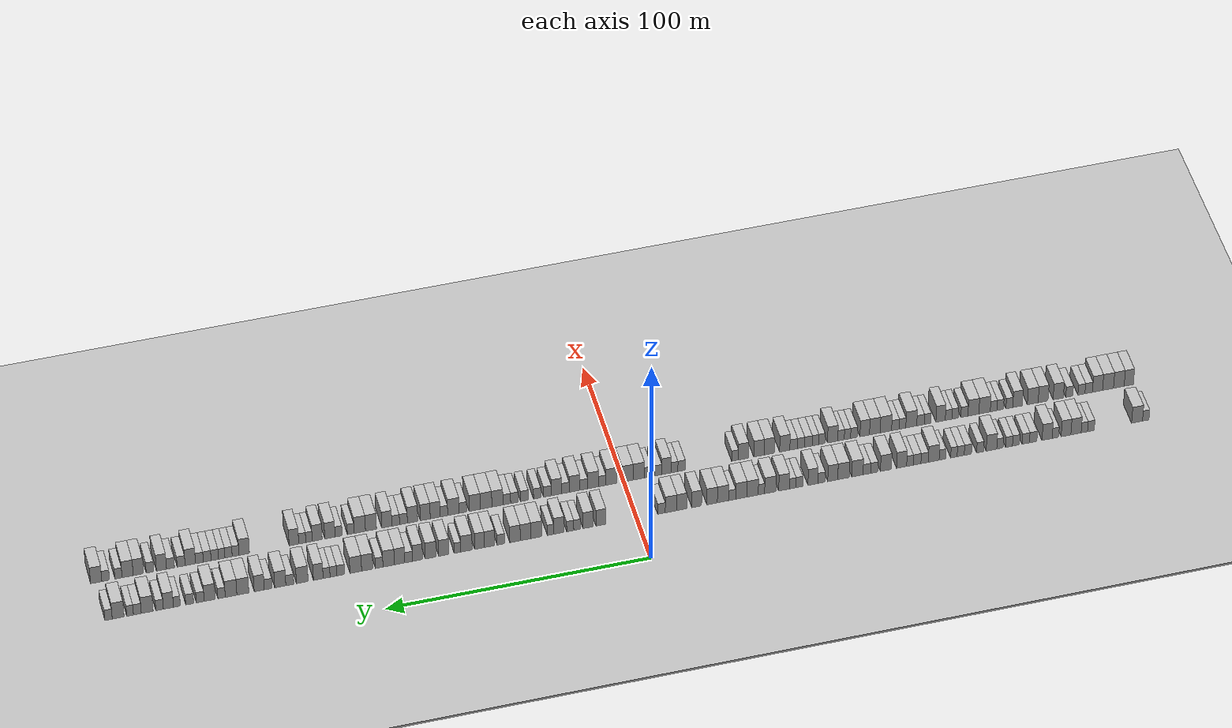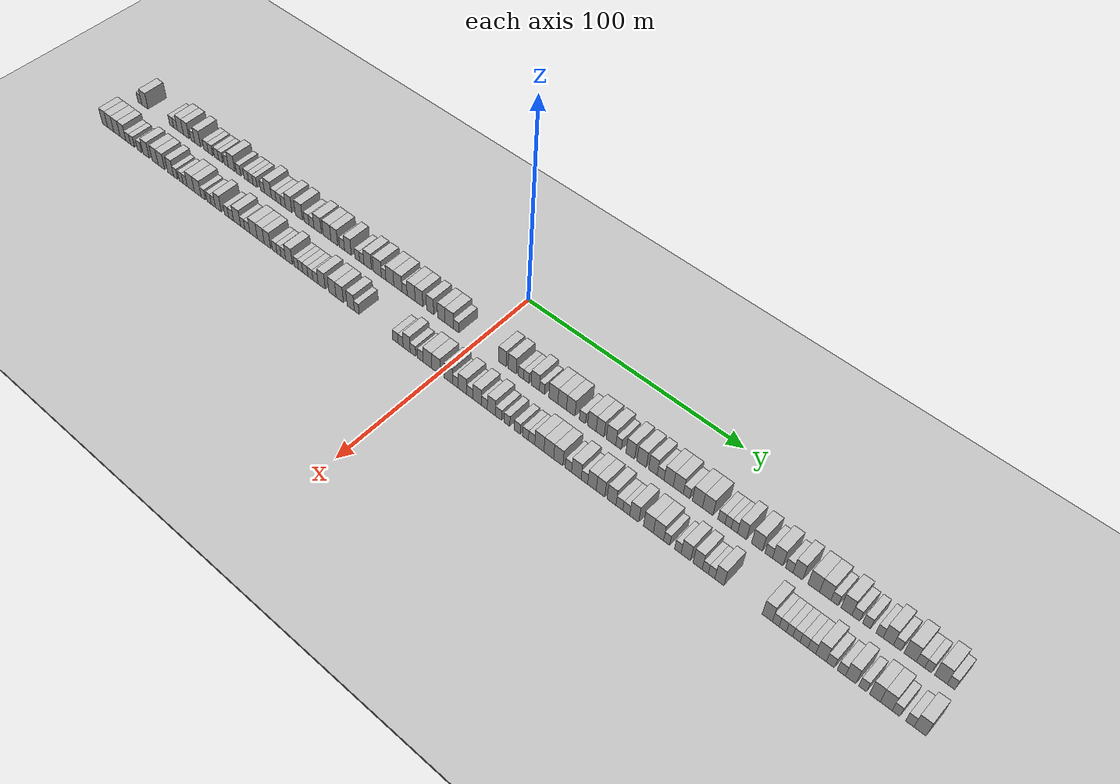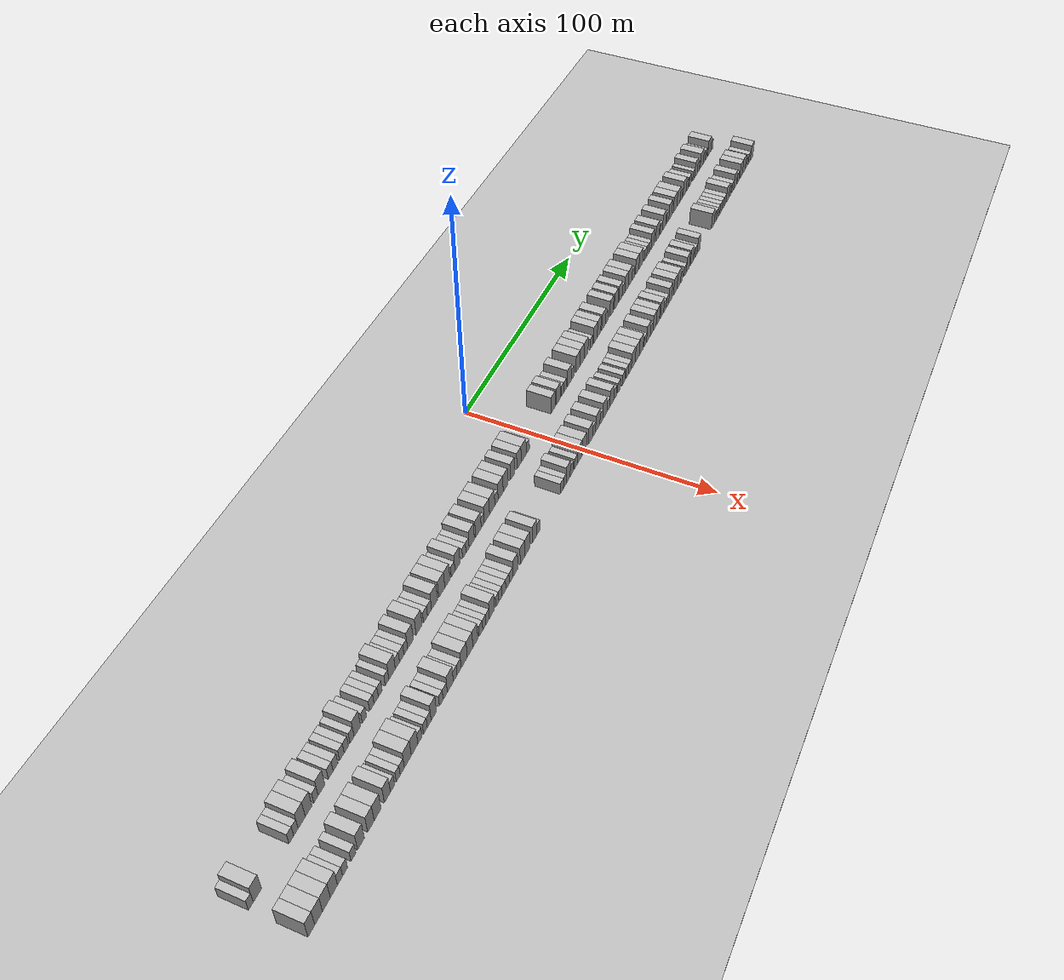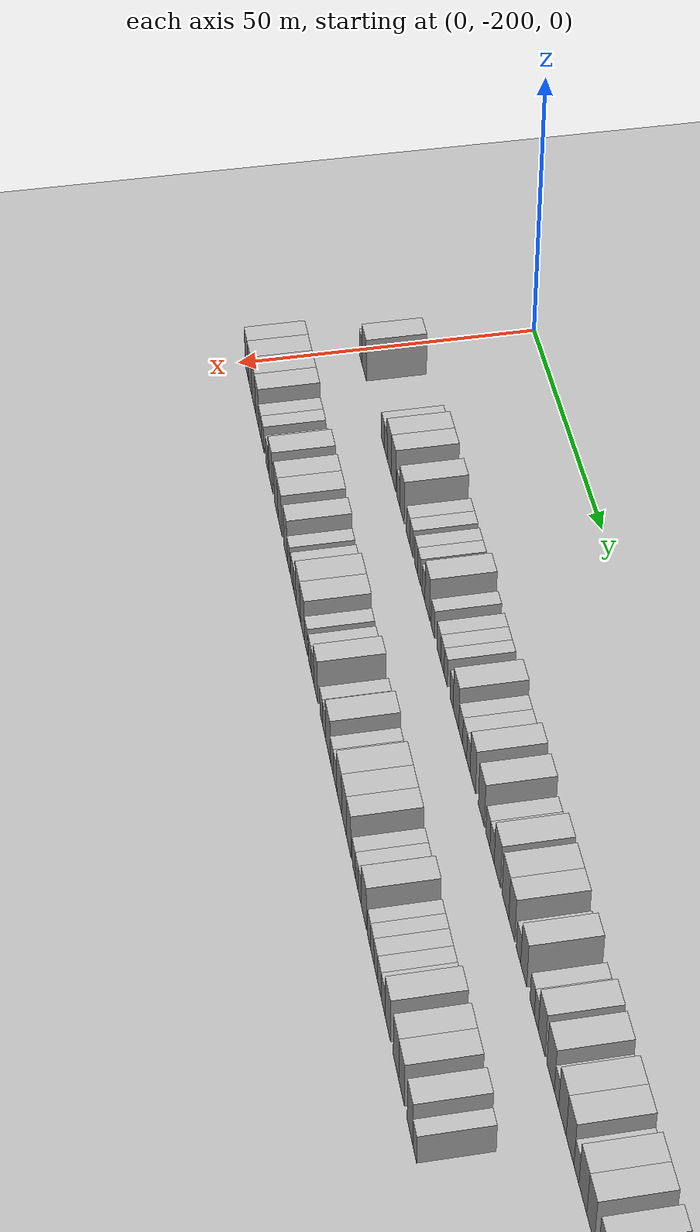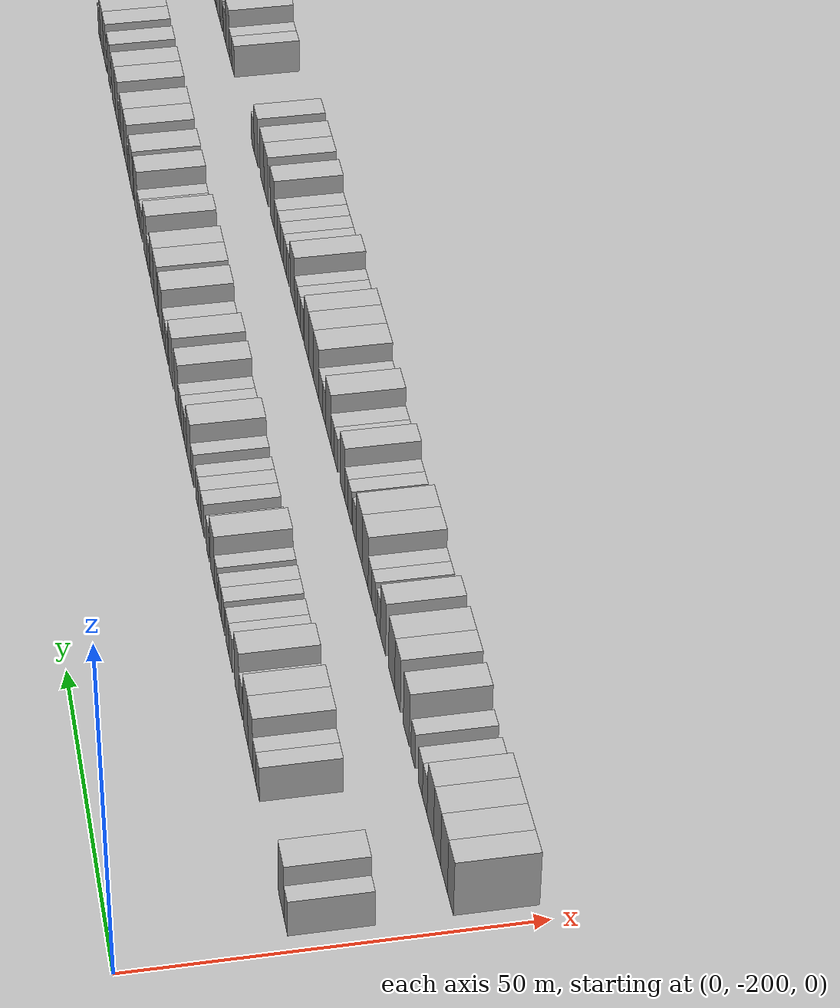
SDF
<?xml version="1.0" encoding="utf-8"?>

<sdf version="1.6">

   <world name="default">

      <gui fullscreen="0">

         <camera name="user_camera">

            <pose>-15 0 4.57585 0 0 0</pose>

            <view_controller>orbit</view_controller>

         </camera>

      </gui>

      <scene>

         <sky>

           <clouds>

             <speed>12</speed>

           </clouds>

         </sky>

         <ambient>0.4 0.4 0.4 1</ambient>

         <background>0.7 0.7 0.7 1</background>

         <shadows>1</shadows>

      </scene>

      <gravity>0 0 -9.8066</gravity>

      <magnetic_field>6e-06 2.3e-05 -4.2e-05</magnetic_field>

      <physics default="0" name="default_physics" type="ode">

         <ode>

            <solver>

               <type>quick</type>

               <iters>10</iters>

               <sor>1.0</sor>

               <use_dynamic_moi_rescaling>0</use_dynamic_moi_rescaling>

            </solver>

            <constraints>

               <cfm>0</cfm>

               <erp>0.2</erp>

               <contact_max_correcting_vel>100</contact_max_correcting_vel>

               <contact_surface_layer>0.001</contact_surface_layer>

            </constraints>

         </ode>

         <max_step_size>0.004</max_step_size>

         <real_time_factor>1</real_time_factor>

         <real_time_update_rate>250</real_time_update_rate>

      </physics>

      <light name="sun" type="directional">

         <cast_shadows>1</cast_shadows>

         <pose>0 0 10 0 0 0</pose>

         <diffuse>0.8 0.8 0.8 1</diffuse>

         <specular>0.2 0.2 0.2 1</specular>

         <attenuation>

            <range>1000</range>

            <constant>0.9</constant>

            <linear>0.01</linear>

            <quadratic>0.001</quadratic>

         </attenuation>

         <direction>-0.5 0.1 -0.9</direction>

      </light>

      <include>

         <name>ground_plane_1</name>

         <uri>model://HANNAS_ground_plane</uri>

         <pose>0 0 0  0 0 0</pose>

      </include>

      <include>

         <name>ground_plane_2</name>

         <uri>model://HANNAS_ground_plane</uri>

         <pose>100 0 0  0 0 0</pose>

      </include>

      <model name="building_1">

         <static>1</static>

         <pose frame="">25.0000 -196.7380 0 0.000000 0.000000 0.000000</pose>

         <link name="link">

            <pose frame="">0 0 3.00 0 0 0</pose>

            <collision name="collision">

               <geometry>

                  <box>

                     <size>10.0000 2.5241 6.0000</size>

                  </box>

               </geometry>

               <max_contacts>10</max_contacts>

               <surface>

                  <contact>

                     <ode/>

                  </contact>

                  <bounce/>

                  <friction>

                     <torsional>

                        <ode/>

                     </torsional>

                     <ode/>

                  </friction>

               </surface>

            </collision>

            <visual name="visual">

               <cast_shadows>0</cast_shadows>

               <geometry>

                  <box>

                     <size>10.0000 2.5241 6.0000</size>

                  </box>

               </geometry>

               <material>

                  <script>

                     <uri>model://HANNAS_wall/materials/scripts</uri>

                     <uri>model://HANNAS_wall/materials/textures</uri>

                     <name>vrc/HANNAS_wall</name>

                  </script>

               </material>

            </visual>

            <self_collide>0</self_collide>

            <enable_wind>0</enable_wind>

            <kinematic>0</kinematic>

         </link>

      </model>

      <model name="building_2">

         <static>1</static>

         <pose frame="">25.0000 -193.3322 0 0.000000 0.000000 0.000000</pose>

         <link name="link">

            <pose frame="">0 0 4.50 0 0 0</pose>

            <collision name="collision">

               <geometry>

                  <box>

                     <size>10.0000 4.2874 9.0000</size>

                  </box>

               </geometry>

               <max_contacts>10</max_contacts>

               <surface>

                  <contact>

                     <ode/>

                  </contact>

                  <bounce/>

                  <friction>

                     <torsional>

                        <ode/>

                     </torsional>

                     <ode/>

                  </friction>

               </surface>

            </collision>

            <visual name="visual">

               <cast_shadows>0</cast_shadows>

               <geometry>

                  <box>

                     <size>10.0000 4.2874 9.0000</size>

                  </box>

               </geometry>

               <material>

                  <script>

                     <uri>model://HANNAS_wall/materials/scripts</uri>

                     <uri>model://HANNAS_wall/materials/textures</uri>

                     <name>vrc/HANNAS_wall</name>

                  </script>

               </material>

            </visual>

            <self_collide>0</self_collide>

            <enable_wind>0</enable_wind>

            <kinematic>0</kinematic>

         </link>

      </model>

      <model name="building_3">

         <static>1</static>

         <pose frame="">25.0000 -175.2250 0 0.000000 0.000000 0.000000</pose>

         <link name="link">

            <pose frame="">0 0 3.00 0 0 0</pose>

            <collision name="collision">

               <geometry>

                  <box>

                     <size>10.0000 2.6423 6.0000</size>

                  </box>

               </geometry>

               <max_contacts>10</max_contacts>

               <surface>

                  <contact>

                     <ode/>

                  </contact>

                  <bounce/>

                  <friction>

                     <torsional>

                        <ode/>

                     </torsional>

                     <ode/>

                  </friction>

               </surface>

            </collision>

            <visual name="visual">

               <cast_shadows>0</cast_shadows>

               <geometry>

                  <box>

                     <size>10.0000 2.6423 6.0000</size>

                  </box>

               </geometry>

               <material>

                  <script>

                     <uri>model://HANNAS_wall/materials/scripts</uri>

                     <uri>model://HANNAS_wall/materials/textures</uri>

                     <name>vrc/HANNAS_wall</name>

                  </script>

               </material>

            </visual>

            <self_collide>0</self_collide>

            <enable_wind>0</enable_wind>

            <kinematic>0</kinematic>

         </link>

      </model>

      <model name="building_4">

         <static>1</static>

         <pose frame="">25.0000 -172.6611 0 0.000000 0.000000 0.000000</pose>

         <link name="link">

            <pose frame="">0 0 3.00 0 0 0</pose>

            <collision name="collision">

               <geometry>

                  <box>

                     <size>10.0000 2.4855 6.0000</size>

                  </box>

               </geometry>

               <max_contacts>10</max_contacts>

               <surface>

                  <contact>

                     <ode/>

                  </contact>

                  <bounce/>

                  <friction>

                     <torsional>

                        <ode/>

                     </torsional>

                     <ode/>

                  </friction>

               </surface>

            </collision>

            <visual name="visual">

               <cast_shadows>0</cast_shadows>

               <geometry>

                  <box>

                     <size>10.0000 2.4855 6.0000</size>

                  </box>

               </geometry>

               <material>

                  <script>

                     <uri>model://HANNAS_wall/materials/scripts</uri>

                     <uri>model://HANNAS_wall/materials/textures</uri>

                     <name>vrc/HANNAS_wall</name>

                  </script>

               </material>

            </visual>

            <self_collide>0</self_collide>

            <enable_wind>0</enable_wind>

            <kinematic>0</kinematic>

         </link>

      </model>

      <model name="building_5">

         <static>1</static>

         <pose frame="">25.0000 -169.4083 0 0.000000 0.000000 0.000000</pose>

         <link name="link">

            <pose frame="">0 0 4.50 0 0 0</pose>

            <collision name="collision">

               <geometry>

                  <box>

                     <size>10.0000 4.0203 9.0000</size>

                  </box>

               </geometry>

               <max_contacts>10</max_contacts>

               <surface>

                  <contact>

                     <ode/>

                  </contact>

                  <bounce/>

                  <friction>

                     <torsional>

                        <ode/>

                     </torsional>

                     <ode/>

                  </friction>

               </surface>

            </collision>

            <visual name="visual">

               <cast_shadows>0</cast_shadows>

               <geometry>

                  <box>

                     <size>10.0000 4.0203 9.0000</size>

                  </box>

               </geometry>

               <material>

                  <script>

                     <uri>model://HANNAS_wall/materials/scripts</uri>

                     <uri>model://HANNAS_wall/materials/textures</uri>

                     <name>vrc/HANNAS_wall</name>

                  </script>

               </material>

            </visual>

            <self_collide>0</self_collide>

            <enable_wind>0</enable_wind>

            <kinematic>0</kinematic>

         </link>

      </model>

      <model name="building_6">

         <static>1</static>

         <pose frame="">25.0000 -165.5061 0 0.000000 0.000000 0.000000</pose>

         <link name="link">

            <pose frame="">0 0 4.50 0 0 0</pose>

            <collision name="collision">

               <geometry>

                  <box>

                     <size>10.0000 3.7842 9.0000</size>

                  </box>

               </geometry>

               <max_contacts>10</max_contacts>

               <surface>

                  <contact>

                     <ode/>

                  </contact>

                  <bounce/>

                  <friction>

                     <torsional>

                        <ode/>

                     </torsional>

                     <ode/>

                  </friction>

               </surface>

            </collision>

            <visual name="visual">

               <cast_shadows>0</cast_shadows>

               <geometry>

                  <box>

                     <size>10.0000 3.7842 9.0000</size>

                  </box>

               </geometry>

               <material>

                  <script>

                     <uri>model://HANNAS_wall/materials/scripts</uri>

                     <uri>model://HANNAS_wall/materials/textures</uri>

                     <name>vrc/HANNAS_wall</name>

                  </script>

               </material>

            </visual>

            <self_collide>0</self_collide>

            <enable_wind>0</enable_wind>

            <kinematic>0</kinematic>

         </link>

      </model>

      <model name="building_7">

         <static>1</static>

         <pose frame="">25.0000 -161.3549 0 0.000000 0.000000 0.000000</pose>

         <link name="link">

            <pose frame="">0 0 3.00 0 0 0</pose>

            <collision name="collision">

               <geometry>

                  <box>

                     <size>10.0000 2.5181 6.0000</size>

                  </box>

               </geometry>

               <max_contacts>10</max_contacts>

               <surface>

                  <contact>

                     <ode/>

                  </contact>

                  <bounce/>

                  <friction>

                     <torsional>

                        <ode/>

                     </torsional>

                     <ode/>

                  </friction>

               </surface>

            </collision>

            <visual name="visual">

               <cast_shadows>0</cast_shadows>

               <geometry>

                  <box>

                     <size>10.0000 2.5181 6.0000</size>

                  </box>

               </geometry>

               <material>

                  <script>

                     <uri>model://HANNAS_wall/materials/scripts</uri>

                     <uri>model://HANNAS_wall/materials/textures</uri>

                     <name>vrc/HANNAS_wall</name>

                  </script>

               </material>

            </visual>

            <self_collide>0</self_collide>

            <enable_wind>0</enable_wind>

            <kinematic>0</kinematic>

         </link>

      </model>

      <model name="building_8">

         <static>1</static>

         <pose frame="">25.0000 -158.1094 0 0.000000 0.000000 0.000000</pose>

         <link name="link">

            <pose frame="">0 0 4.50 0 0 0</pose>

            <collision name="collision">

               <geometry>

                  <box>

                     <size>10.0000 3.9730 9.0000</size>

                  </box>

               </geometry>

               <max_contacts>10</max_contacts>

               <surface>

                  <contact>

                     <ode/>

                  </contact>

                  <bounce/>

                  <friction>

                     <torsional>

                        <ode/>

                     </torsional>

                     <ode/>

                  </friction>

               </surface>

            </collision>

            <visual name="visual">

               <cast_shadows>0</cast_shadows>

               <geometry>

                  <box>

                     <size>10.0000 3.9730 9.0000</size>

                  </box>

               </geometry>

               <material>

                  <script>

                     <uri>model://HANNAS_wall/materials/scripts</uri>

                     <uri>model://HANNAS_wall/materials/textures</uri>

                     <name>vrc/HANNAS_wall</name>

                  </script>

               </material>

            </visual>

            <self_collide>0</self_collide>

            <enable_wind>0</enable_wind>

            <kinematic>0</kinematic>

         </link>

      </model>

      <model name="building_9">

         <static>1</static>

         <pose frame="">25.0000 -152.6712 0 0.000000 0.000000 0.000000</pose>

         <link name="link">

            <pose frame="">0 0 3.00 0 0 0</pose>

            <collision name="collision">

               <geometry>

                  <box>

                     <size>10.0000 2.9033 6.0000</size>

                  </box>

               </geometry>

               <max_contacts>10</max_contacts>

               <surface>

                  <contact>

                     <ode/>

                  </contact>

                  <bounce/>

                  <friction>

                     <torsional>

                        <ode/>

                     </torsional>

                     <ode/>

                  </friction>

               </surface>

            </collision>

            <visual name="visual">

               <cast_shadows>0</cast_shadows>

               <geometry>

                  <box>

                     <size>10.0000 2.9033 6.0000</size>

                  </box>

               </geometry>

               <material>

                  <script>

                     <uri>model://HANNAS_wall/materials/scripts</uri>

                     <uri>model://HANNAS_wall/materials/textures</uri>

                     <name>vrc/HANNAS_wall</name>

                  </script>

               </material>

            </visual>

            <self_collide>0</self_collide>

            <enable_wind>0</enable_wind>

            <kinematic>0</kinematic>

         </link>

      </model>

      <model name="building_10">

         <static>1</static>

         <pose frame="">25.0000 -149.7835 0 0.000000 0.000000 0.000000</pose>

         <link name="link">

            <pose frame="">0 0 3.00 0 0 0</pose>

            <collision name="collision">

               <geometry>

                  <box>

                     <size>10.0000 2.8720 6.0000</size>

                  </box>

               </geometry>

               <max_contacts>10</max_contacts>

               <surface>

                  <contact>

                     <ode/>

                  </contact>

                  <bounce/>

                  <friction>

                     <torsional>

                        <ode/>

                     </torsional>

                     <ode/>

                  </friction>

               </surface>

            </collision>

            <visual name="visual">

               <cast_shadows>0</cast_shadows>

               <geometry>

                  <box>

                     <size>10.0000 2.8720 6.0000</size>

                  </box>

               </geometry>

               <material>

                  <script>

                     <uri>model://HANNAS_wall/materials/scripts</uri>

                     <uri>model://HANNAS_wall/materials/textures</uri>

                     <name>vrc/HANNAS_wall</name>

                  </script>

               </material>

            </visual>

            <self_collide>0</self_collide>

            <enable_wind>0</enable_wind>

            <kinematic>0</kinematic>

         </link>

      </model>

      <model name="building_11">

         <static>1</static>

         <pose frame="">25.0000 -145.9780 0 0.000000 0.000000 0.000000</pose>

         <link name="link">

            <pose frame="">0 0 3.00 0 0 0</pose>

            <collision name="collision">

               <geometry>

                  <box>

                     <size>10.0000 2.7389 6.0000</size>

                  </box>

               </geometry>

               <max_contacts>10</max_contacts>

               <surface>

                  <contact>

                     <ode/>

                  </contact>

                  <bounce/>

                  <friction>

                     <torsional>

                        <ode/>

                     </torsional>

                     <ode/>

                  </friction>

               </surface>

            </collision>

            <visual name="visual">

               <cast_shadows>0</cast_shadows>

               <geometry>

                  <box>

                     <size>10.0000 2.7389 6.0000</size>

                  </box>

               </geometry>

               <material>

                  <script>

                     <uri>model://HANNAS_wall/materials/scripts</uri>

                     <uri>model://HANNAS_wall/materials/textures</uri>

                     <name>vrc/HANNAS_wall</name>

                  </script>

               </material>

            </visual>

            <self_collide>0</self_collide>

            <enable_wind>0</enable_wind>

            <kinematic>0</kinematic>

         </link>

      </model>

      <model name="building_12">

         <static>1</static>

         <pose frame="">25.0000 -143.2816 0 0.000000 0.000000 0.000000</pose>

         <link name="link">

            <pose frame="">0 0 3.00 0 0 0</pose>

            <collision name="collision">

               <geometry>

                  <box>

                     <size>10.0000 2.6540 6.0000</size>

                  </box>

               </geometry>

               <max_contacts>10</max_contacts>

               <surface>

                  <contact>

                     <ode/>

                  </contact>

                  <bounce/>

                  <friction>

                     <torsional>

                        <ode/>

                     </torsional>

                     <ode/>

                  </friction>

               </surface>

            </collision>

            <visual name="visual">

               <cast_shadows>0</cast_shadows>

               <geometry>

                  <box>

                     <size>10.0000 2.6540 6.0000</size>

                  </box>

               </geometry>

               <material>

                  <script>

                     <uri>model://HANNAS_wall/materials/scripts</uri>

                     <uri>model://HANNAS_wall/materials/textures</uri>

                     <name>vrc/HANNAS_wall</name>

                  </script>

               </material>

            </visual>

            <self_collide>0</self_collide>

            <enable_wind>0</enable_wind>

            <kinematic>0</kinematic>

         </link>

      </model>

      <model name="building_13">

         <static>1</static>

         <pose frame="">25.0000 -139.7228 0 0.000000 0.000000 0.000000</pose>

         <link name="link">

            <pose frame="">0 0 3.00 0 0 0</pose>

            <collision name="collision">

               <geometry>

                  <box>

                     <size>10.0000 2.4635 6.0000</size>

                  </box>

               </geometry>

               <max_contacts>10</max_contacts>

               <surface>

                  <contact>

                     <ode/>

                  </contact>

                  <bounce/>

                  <friction>

                     <torsional>

                        <ode/>

                     </torsional>

                     <ode/>

                  </friction>

               </surface>

            </collision>

            <visual name="visual">

               <cast_shadows>0</cast_shadows>

               <geometry>

                  <box>

                     <size>10.0000 2.4635 6.0000</size>

                  </box>

               </geometry>

               <material>

                  <script>

                     <uri>model://HANNAS_wall/materials/scripts</uri>

                     <uri>model://HANNAS_wall/materials/textures</uri>

                     <name>vrc/HANNAS_wall</name>

                  </script>

               </material>

            </visual>

            <self_collide>0</self_collide>

            <enable_wind>0</enable_wind>

            <kinematic>0</kinematic>

         </link>

      </model>

      <model name="building_14">

         <static>1</static>

         <pose frame="">25.0000 -136.4352 0 0.000000 0.000000 0.000000</pose>

         <link name="link">

            <pose frame="">0 0 4.50 0 0 0</pose>

            <collision name="collision">

               <geometry>

                  <box>

                     <size>10.0000 4.1118 9.0000</size>

                  </box>

               </geometry>

               <max_contacts>10</max_contacts>

               <surface>

                  <contact>

                     <ode/>

                  </contact>

                  <bounce/>

                  <friction>

                     <torsional>

                        <ode/>

                     </torsional>

                     <ode/>

                  </friction>

               </surface>

            </collision>

            <visual name="visual">

               <cast_shadows>0</cast_shadows>

               <geometry>

                  <box>

                     <size>10.0000 4.1118 9.0000</size>

                  </box>

               </geometry>

               <material>

                  <script>

                     <uri>model://HANNAS_wall/materials/scripts</uri>

                     <uri>model://HANNAS_wall/materials/textures</uri>

                     <name>vrc/HANNAS_wall</name>

                  </script>

               </material>

            </visual>

            <self_collide>0</self_collide>

            <enable_wind>0</enable_wind>

            <kinematic>0</kinematic>

         </link>

      </model>

      <model name="building_15">

         <static>1</static>

         <pose frame="">25.0000 -132.0211 0 0.000000 0.000000 0.000000</pose>

         <link name="link">

            <pose frame="">0 0 3.00 0 0 0</pose>

            <collision name="collision">

               <geometry>

                  <box>

                     <size>10.0000 2.7164 6.0000</size>

                  </box>

               </geometry>

               <max_contacts>10</max_contacts>

               <surface>

                  <contact>

                     <ode/>

                  </contact>

                  <bounce/>

                  <friction>

                     <torsional>

                        <ode/>

                     </torsional>

                     <ode/>

                  </friction>

               </surface>

            </collision>

            <visual name="visual">

               <cast_shadows>0</cast_shadows>

               <geometry>

                  <box>

                     <size>10.0000 2.7164 6.0000</size>

                  </box>

               </geometry>

               <material>

                  <script>

                     <uri>model://HANNAS_wall/materials/scripts</uri>

                     <uri>model://HANNAS_wall/materials/textures</uri>

                     <name>vrc/HANNAS_wall</name>

                  </script>

               </material>

            </visual>

            <self_collide>0</self_collide>

            <enable_wind>0</enable_wind>

            <kinematic>0</kinematic>

         </link>

      </model>

      <model name="building_16">

         <static>1</static>

         <pose frame="">25.0000 -127.2485 0 0.000000 0.000000 0.000000</pose>

         <link name="link">

            <pose frame="">0 0 3.00 0 0 0</pose>

            <collision name="collision">

               <geometry>

                  <box>

                     <size>10.0000 2.8289 6.0000</size>

                  </box>

               </geometry>

               <max_contacts>10</max_contacts>

               <surface>

                  <contact>

                     <ode/>

                  </contact>

                  <bounce/>

                  <friction>

                     <torsional>

                        <ode/>

                     </torsional>

                     <ode/>

                  </friction>

               </surface>

            </collision>

            <visual name="visual">

               <cast_shadows>0</cast_shadows>

               <geometry>

                  <box>

                     <size>10.0000 2.8289 6.0000</size>

                  </box>

               </geometry>

               <material>

                  <script>

                     <uri>model://HANNAS_wall/materials/scripts</uri>

                     <uri>model://HANNAS_wall/materials/textures</uri>

                     <name>vrc/HANNAS_wall</name>

                  </script>

               </material>

            </visual>

            <self_collide>0</self_collide>

            <enable_wind>0</enable_wind>

            <kinematic>0</kinematic>

         </link>

      </model>

      <model name="building_17">

         <static>1</static>

         <pose frame="">25.0000 -124.4557 0 0.000000 0.000000 0.000000</pose>

         <link name="link">

            <pose frame="">0 0 3.00 0 0 0</pose>

            <collision name="collision">

               <geometry>

                  <box>

                     <size>10.0000 2.7568 6.0000</size>

                  </box>

               </geometry>

               <max_contacts>10</max_contacts>

               <surface>

                  <contact>

                     <ode/>

                  </contact>

                  <bounce/>

                  <friction>

                     <torsional>

                        <ode/>

                     </torsional>

                     <ode/>

                  </friction>

               </surface>

            </collision>

            <visual name="visual">

               <cast_shadows>0</cast_shadows>

               <geometry>

                  <box>

                     <size>10.0000 2.7568 6.0000</size>

                  </box>

               </geometry>

               <material>

                  <script>

                     <uri>model://HANNAS_wall/materials/scripts</uri>

                     <uri>model://HANNAS_wall/materials/textures</uri>

                     <name>vrc/HANNAS_wall</name>

                  </script>

               </material>

            </visual>

            <self_collide>0</self_collide>

            <enable_wind>0</enable_wind>

            <kinematic>0</kinematic>

         </link>

      </model>

      <model name="building_18">

         <static>1</static>

         <pose frame="">25.0000 -121.8323 0 0.000000 0.000000 0.000000</pose>

         <link name="link">

            <pose frame="">0 0 3.00 0 0 0</pose>

            <collision name="collision">

               <geometry>

                  <box>

                     <size>10.0000 2.4898 6.0000</size>

                  </box>

               </geometry>

               <max_contacts>10</max_contacts>

               <surface>

                  <contact>

                     <ode/>

                  </contact>

                  <bounce/>

                  <friction>

                     <torsional>

                        <ode/>

                     </torsional>

                     <ode/>

                  </friction>

               </surface>

            </collision>

            <visual name="visual">

               <cast_shadows>0</cast_shadows>

               <geometry>

                  <box>

                     <size>10.0000 2.4898 6.0000</size>

                  </box>

               </geometry>

               <material>

                  <script>

                     <uri>model://HANNAS_wall/materials/scripts</uri>

                     <uri>model://HANNAS_wall/materials/textures</uri>

                     <name>vrc/HANNAS_wall</name>

                  </script>

               </material>

            </visual>

            <self_collide>0</self_collide>

            <enable_wind>0</enable_wind>

            <kinematic>0</kinematic>

         </link>

      </model>

      <model name="building_19">

         <static>1</static>

         <pose frame="">25.0000 -117.3427 0 0.000000 0.000000 0.000000</pose>

         <link name="link">

            <pose frame="">0 0 3.00 0 0 0</pose>

            <collision name="collision">

               <geometry>

                  <box>

                     <size>10.0000 2.4895 6.0000</size>

                  </box>

               </geometry>

               <max_contacts>10</max_contacts>

               <surface>

                  <contact>

                     <ode/>

                  </contact>

                  <bounce/>

                  <friction>

                     <torsional>

                        <ode/>

                     </torsional>

                     <ode/>

                  </friction>

               </surface>

            </collision>

            <visual name="visual">

               <cast_shadows>0</cast_shadows>

               <geometry>

                  <box>

                     <size>10.0000 2.4895 6.0000</size>

                  </box>

               </geometry>

               <material>

                  <script>

                     <uri>model://HANNAS_wall/materials/scripts</uri>

                     <uri>model://HANNAS_wall/materials/textures</uri>

                     <name>vrc/HANNAS_wall</name>

                  </script>

               </material>

            </visual>

            <self_collide>0</self_collide>

            <enable_wind>0</enable_wind>

            <kinematic>0</kinematic>

         </link>

      </model>

      <model name="building_20">

         <static>1</static>

         <pose frame="">25.0000 -113.9905 0 0.000000 0.000000 0.000000</pose>

         <link name="link">

            <pose frame="">0 0 4.50 0 0 0</pose>

            <collision name="collision">

               <geometry>

                  <box>

                     <size>10.0000 4.2148 9.0000</size>

                  </box>

               </geometry>

               <max_contacts>10</max_contacts>

               <surface>

                  <contact>

                     <ode/>

                  </contact>

                  <bounce/>

                  <friction>

                     <torsional>

                        <ode/>

                     </torsional>

                     <ode/>

                  </friction>

               </surface>

            </collision>

            <visual name="visual">

               <cast_shadows>0</cast_shadows>

               <geometry>

                  <box>

                     <size>10.0000 4.2148 9.0000</size>

                  </box>

               </geometry>

               <material>

                  <script>

                     <uri>model://HANNAS_wall/materials/scripts</uri>

                     <uri>model://HANNAS_wall/materials/textures</uri>

                     <name>vrc/HANNAS_wall</name>

                  </script>

               </material>

            </visual>

            <self_collide>0</self_collide>

            <enable_wind>0</enable_wind>

            <kinematic>0</kinematic>

         </link>

      </model>

      <model name="building_21">

         <static>1</static>

         <pose frame="">25.0000 -110.4575 0 0.000000 0.000000 0.000000</pose>

         <link name="link">

            <pose frame="">0 0 3.00 0 0 0</pose>

            <collision name="collision">

               <geometry>

                  <box>

                     <size>10.0000 2.8513 6.0000</size>

                  </box>

               </geometry>

               <max_contacts>10</max_contacts>

               <surface>

                  <contact>

                     <ode/>

                  </contact>

                  <bounce/>

                  <friction>

                     <torsional>

                        <ode/>

                     </torsional>

                     <ode/>

                  </friction>

               </surface>

            </collision>

            <visual name="visual">

               <cast_shadows>0</cast_shadows>

               <geometry>

                  <box>

                     <size>10.0000 2.8513 6.0000</size>

                  </box>

               </geometry>

               <material>

                  <script>

                     <uri>model://HANNAS_wall/materials/scripts</uri>

                     <uri>model://HANNAS_wall/materials/textures</uri>

                     <name>vrc/HANNAS_wall</name>

                  </script>

               </material>

            </visual>

            <self_collide>0</self_collide>

            <enable_wind>0</enable_wind>

            <kinematic>0</kinematic>

         </link>

      </model>

      <model name="building_22">

         <static>1</static>

         <pose frame="">25.0000 -107.5320 0 0.000000 0.000000 0.000000</pose>

         <link name="link">

            <pose frame="">0 0 3.00 0 0 0</pose>

            <collision name="collision">

               <geometry>

                  <box>

                     <size>10.0000 2.9997 6.0000</size>

                  </box>

               </geometry>

               <max_contacts>10</max_contacts>

               <surface>

                  <contact>

                     <ode/>

                  </contact>

                  <bounce/>

                  <friction>

                     <torsional>

                        <ode/>

                     </torsional>

                     <ode/>

                  </friction>

               </surface>

            </collision>

            <visual name="visual">

               <cast_shadows>0</cast_shadows>

               <geometry>

                  <box>

                     <size>10.0000 2.9997 6.0000</size>

                  </box>

               </geometry>

               <material>

                  <script>

                     <uri>model://HANNAS_wall/materials/scripts</uri>

                     <uri>model://HANNAS_wall/materials/textures</uri>

                     <name>vrc/HANNAS_wall</name>

                  </script>

               </material>

            </visual>

            <self_collide>0</self_collide>

            <enable_wind>0</enable_wind>

            <kinematic>0</kinematic>

         </link>

      </model>

      <model name="building_23">

         <static>1</static>

         <pose frame="">25.0000 -104.7620 0 0.000000 0.000000 0.000000</pose>

         <link name="link">

            <pose frame="">0 0 3.00 0 0 0</pose>

            <collision name="collision">

               <geometry>

                  <box>

                     <size>10.0000 2.5403 6.0000</size>

                  </box>

               </geometry>

               <max_contacts>10</max_contacts>

               <surface>

                  <contact>

                     <ode/>

                  </contact>

                  <bounce/>

                  <friction>

                     <torsional>

                        <ode/>

                     </torsional>

                     <ode/>

                  </friction>

               </surface>

            </collision>

            <visual name="visual">

               <cast_shadows>0</cast_shadows>

               <geometry>

                  <box>

                     <size>10.0000 2.5403 6.0000</size>

                  </box>

               </geometry>

               <material>

                  <script>

                     <uri>model://HANNAS_wall/materials/scripts</uri>

                     <uri>model://HANNAS_wall/materials/textures</uri>

                     <name>vrc/HANNAS_wall</name>

                  </script>

               </material>

            </visual>

            <self_collide>0</self_collide>

            <enable_wind>0</enable_wind>

            <kinematic>0</kinematic>

         </link>

      </model>

      <model name="building_24">

         <static>1</static>

         <pose frame="">25.0000 -101.5410 0 0.000000 0.000000 0.000000</pose>

         <link name="link">

            <pose frame="">0 0 4.50 0 0 0</pose>

            <collision name="collision">

               <geometry>

                  <box>

                     <size>10.0000 3.9016 9.0000</size>

                  </box>

               </geometry>

               <max_contacts>10</max_contacts>

               <surface>

                  <contact>

                     <ode/>

                  </contact>

                  <bounce/>

                  <friction>

                     <torsional>

                        <ode/>

                     </torsional>

                     <ode/>

                  </friction>

               </surface>

            </collision>

            <visual name="visual">

               <cast_shadows>0</cast_shadows>

               <geometry>

                  <box>

                     <size>10.0000 3.9016 9.0000</size>

                  </box>

               </geometry>

               <material>

                  <script>

                     <uri>model://HANNAS_wall/materials/scripts</uri>

                     <uri>model://HANNAS_wall/materials/textures</uri>

                     <name>vrc/HANNAS_wall</name>

                  </script>

               </material>

            </visual>

            <self_collide>0</self_collide>

            <enable_wind>0</enable_wind>

            <kinematic>0</kinematic>

         </link>

      </model>

      <model name="building_25">

         <static>1</static>

         <pose frame="">25.0000 -95.4737 0 0.000000 0.000000 0.000000</pose>

         <link name="link">

            <pose frame="">0 0 4.50 0 0 0</pose>

            <collision name="collision">

               <geometry>

                  <box>

                     <size>10.0000 4.2329 9.0000</size>

                  </box>

               </geometry>

               <max_contacts>10</max_contacts>

               <surface>

                  <contact>

                     <ode/>

                  </contact>

                  <bounce/>

                  <friction>

                     <torsional>

                        <ode/>

                     </torsional>

                     <ode/>

                  </friction>

               </surface>

            </collision>

            <visual name="visual">

               <cast_shadows>0</cast_shadows>

               <geometry>

                  <box>

                     <size>10.0000 4.2329 9.0000</size>

                  </box>

               </geometry>

               <material>

                  <script>

                     <uri>model://HANNAS_wall/materials/scripts</uri>

                     <uri>model://HANNAS_wall/materials/textures</uri>

                     <name>vrc/HANNAS_wall</name>

                  </script>

               </material>

            </visual>

            <self_collide>0</self_collide>

            <enable_wind>0</enable_wind>

            <kinematic>0</kinematic>

         </link>

      </model>

      <model name="building_26">

         <static>1</static>

         <pose frame="">25.0000 -90.9416 0 0.000000 0.000000 0.000000</pose>

         <link name="link">

            <pose frame="">0 0 3.00 0 0 0</pose>

            <collision name="collision">

               <geometry>

                  <box>

                     <size>10.0000 2.8314 6.0000</size>

                  </box>

               </geometry>

               <max_contacts>10</max_contacts>

               <surface>

                  <contact>

                     <ode/>

                  </contact>

                  <bounce/>

                  <friction>

                     <torsional>

                        <ode/>

                     </torsional>

                     <ode/>

                  </friction>

               </surface>

            </collision>

            <visual name="visual">

               <cast_shadows>0</cast_shadows>

               <geometry>

                  <box>

                     <size>10.0000 2.8314 6.0000</size>

                  </box>

               </geometry>

               <material>

                  <script>

                     <uri>model://HANNAS_wall/materials/scripts</uri>

                     <uri>model://HANNAS_wall/materials/textures</uri>

                     <name>vrc/HANNAS_wall</name>

                  </script>

               </material>

            </visual>

            <self_collide>0</self_collide>

            <enable_wind>0</enable_wind>

            <kinematic>0</kinematic>

         </link>

      </model>

      <model name="building_27">

         <static>1</static>

         <pose frame="">25.0000 -88.0815 0 0.000000 0.000000 0.000000</pose>

         <link name="link">

            <pose frame="">0 0 3.00 0 0 0</pose>

            <collision name="collision">

               <geometry>

                  <box>

                     <size>10.0000 2.8888 6.0000</size>

                  </box>

               </geometry>

               <max_contacts>10</max_contacts>

               <surface>

                  <contact>

                     <ode/>

                  </contact>

                  <bounce/>

                  <friction>

                     <torsional>

                        <ode/>

                     </torsional>

                     <ode/>

                  </friction>

               </surface>

            </collision>

            <visual name="visual">

               <cast_shadows>0</cast_shadows>

               <geometry>

                  <box>

                     <size>10.0000 2.8888 6.0000</size>

                  </box>

               </geometry>

               <material>

                  <script>

                     <uri>model://HANNAS_wall/materials/scripts</uri>

                     <uri>model://HANNAS_wall/materials/textures</uri>

                     <name>vrc/HANNAS_wall</name>

                  </script>

               </material>

            </visual>

            <self_collide>0</self_collide>

            <enable_wind>0</enable_wind>

            <kinematic>0</kinematic>

         </link>

      </model>

      <model name="building_28">

         <static>1</static>

         <pose frame="">25.0000 -84.4759 0 0.000000 0.000000 0.000000</pose>

         <link name="link">

            <pose frame="">0 0 4.50 0 0 0</pose>

            <collision name="collision">

               <geometry>

                  <box>

                     <size>10.0000 4.3225 9.0000</size>

                  </box>

               </geometry>

               <max_contacts>10</max_contacts>

               <surface>

                  <contact>

                     <ode/>

                  </contact>

                  <bounce/>

                  <friction>

                     <torsional>

                        <ode/>

                     </torsional>

                     <ode/>

                  </friction>

               </surface>

            </collision>

            <visual name="visual">

               <cast_shadows>0</cast_shadows>

               <geometry>

                  <box>

                     <size>10.0000 4.3225 9.0000</size>

                  </box>

               </geometry>

               <material>

                  <script>

                     <uri>model://HANNAS_wall/materials/scripts</uri>

                     <uri>model://HANNAS_wall/materials/textures</uri>

                     <name>vrc/HANNAS_wall</name>

                  </script>

               </material>

            </visual>

            <self_collide>0</self_collide>

            <enable_wind>0</enable_wind>

            <kinematic>0</kinematic>

         </link>

      </model>

      <model name="building_29">

         <static>1</static>

         <pose frame="">25.0000 -79.1001 0 0.000000 0.000000 0.000000</pose>

         <link name="link">

            <pose frame="">0 0 4.50 0 0 0</pose>

            <collision name="collision">

               <geometry>

                  <box>

                     <size>10.0000 4.4290 9.0000</size>

                  </box>

               </geometry>

               <max_contacts>10</max_contacts>

               <surface>

                  <contact>

                     <ode/>

                  </contact>

                  <bounce/>

                  <friction>

                     <torsional>

                        <ode/>

                     </torsional>

                     <ode/>

                  </friction>

               </surface>

            </collision>

            <visual name="visual">

               <cast_shadows>0</cast_shadows>

               <geometry>

                  <box>

                     <size>10.0000 4.4290 9.0000</size>

                  </box>

               </geometry>

               <material>

                  <script>

                     <uri>model://HANNAS_wall/materials/scripts</uri>

                     <uri>model://HANNAS_wall/materials/textures</uri>

                     <name>vrc/HANNAS_wall</name>

                  </script>

               </material>

            </visual>

            <self_collide>0</self_collide>

            <enable_wind>0</enable_wind>

            <kinematic>0</kinematic>

         </link>

      </model>

      <model name="building_30">

         <static>1</static>

         <pose frame="">25.0000 -74.9526 0 0.000000 0.000000 0.000000</pose>

         <link name="link">

            <pose frame="">0 0 4.50 0 0 0</pose>

            <collision name="collision">

               <geometry>

                  <box>

                     <size>10.0000 3.8659 9.0000</size>

                  </box>

               </geometry>

               <max_contacts>10</max_contacts>

               <surface>

                  <contact>

                     <ode/>

                  </contact>

                  <bounce/>

                  <friction>

                     <torsional>

                        <ode/>

                     </torsional>

                     <ode/>

                  </friction>

               </surface>

            </collision>

            <visual name="visual">

               <cast_shadows>0</cast_shadows>

               <geometry>

                  <box>

                     <size>10.0000 3.8659 9.0000</size>

                  </box>

               </geometry>

               <material>

                  <script>

                     <uri>model://HANNAS_wall/materials/scripts</uri>

                     <uri>model://HANNAS_wall/materials/textures</uri>

                     <name>vrc/HANNAS_wall</name>

                  </script>

               </material>

            </visual>

            <self_collide>0</self_collide>

            <enable_wind>0</enable_wind>

            <kinematic>0</kinematic>

         </link>

      </model>

      <model name="building_31">

         <static>1</static>

         <pose frame="">25.0000 -70.6167 0 0.000000 0.000000 0.000000</pose>

         <link name="link">

            <pose frame="">0 0 3.00 0 0 0</pose>

            <collision name="collision">

               <geometry>

                  <box>

                     <size>10.0000 2.8060 6.0000</size>

                  </box>

               </geometry>

               <max_contacts>10</max_contacts>

               <surface>

                  <contact>

                     <ode/>

                  </contact>

                  <bounce/>

                  <friction>

                     <torsional>

                        <ode/>

                     </torsional>

                     <ode/>

                  </friction>

               </surface>

            </collision>

            <visual name="visual">

               <cast_shadows>0</cast_shadows>

               <geometry>

                  <box>

                     <size>10.0000 2.8060 6.0000</size>

                  </box>

               </geometry>

               <material>

                  <script>

                     <uri>model://HANNAS_wall/materials/scripts</uri>

                     <uri>model://HANNAS_wall/materials/textures</uri>

                     <name>vrc/HANNAS_wall</name>

                  </script>

               </material>

            </visual>

            <self_collide>0</self_collide>

            <enable_wind>0</enable_wind>

            <kinematic>0</kinematic>

         </link>

      </model>

      <model name="building_32">

         <static>1</static>

         <pose frame="">25.0000 -67.3037 0 0.000000 0.000000 0.000000</pose>

         <link name="link">

            <pose frame="">0 0 4.50 0 0 0</pose>

            <collision name="collision">

               <geometry>

                  <box>

                     <size>10.0000 3.8201 9.0000</size>

                  </box>

               </geometry>

               <max_contacts>10</max_contacts>

               <surface>

                  <contact>

                     <ode/>

                  </contact>

                  <bounce/>

                  <friction>

                     <torsional>

                        <ode/>

                     </torsional>

                     <ode/>

                  </friction>

               </surface>

            </collision>

            <visual name="visual">

               <cast_shadows>0</cast_shadows>

               <geometry>

                  <box>

                     <size>10.0000 3.8201 9.0000</size>

                  </box>

               </geometry>

               <material>

                  <script>

                     <uri>model://HANNAS_wall/materials/scripts</uri>

                     <uri>model://HANNAS_wall/materials/textures</uri>

                     <name>vrc/HANNAS_wall</name>

                  </script>

               </material>

            </visual>

            <self_collide>0</self_collide>

            <enable_wind>0</enable_wind>

            <kinematic>0</kinematic>

         </link>

      </model>

      <model name="building_33">

         <static>1</static>

         <pose frame="">25.0000 -62.0734 0 0.000000 0.000000 0.000000</pose>

         <link name="link">

            <pose frame="">0 0 3.00 0 0 0</pose>

            <collision name="collision">

               <geometry>

                  <box>

                     <size>10.0000 2.6405 6.0000</size>

                  </box>

               </geometry>

               <max_contacts>10</max_contacts>

               <surface>

                  <contact>

                     <ode/>

                  </contact>

                  <bounce/>

                  <friction>

                     <torsional>

                        <ode/>

                     </torsional>

                     <ode/>

                  </friction>

               </surface>

            </collision>

            <visual name="visual">

               <cast_shadows>0</cast_shadows>

               <geometry>

                  <box>

                     <size>10.0000 2.6405 6.0000</size>

                  </box>

               </geometry>

               <material>

                  <script>

                     <uri>model://HANNAS_wall/materials/scripts</uri>

                     <uri>model://HANNAS_wall/materials/textures</uri>

                     <name>vrc/HANNAS_wall</name>

                  </script>

               </material>

            </visual>

            <self_collide>0</self_collide>

            <enable_wind>0</enable_wind>

            <kinematic>0</kinematic>

         </link>

      </model>

      <model name="building_34">

         <static>1</static>

         <pose frame="">25.0000 -59.5268 0 0.000000 0.000000 0.000000</pose>

         <link name="link">

            <pose frame="">0 0 3.00 0 0 0</pose>

            <collision name="collision">

               <geometry>

                  <box>

                     <size>10.0000 2.4527 6.0000</size>

                  </box>

               </geometry>

               <max_contacts>10</max_contacts>

               <surface>

                  <contact>

                     <ode/>

                  </contact>

                  <bounce/>

                  <friction>

                     <torsional>

                        <ode/>

                     </torsional>

                     <ode/>

                  </friction>

               </surface>

            </collision>

            <visual name="visual">

               <cast_shadows>0</cast_shadows>

               <geometry>

                  <box>

                     <size>10.0000 2.4527 6.0000</size>

                  </box>

               </geometry>

               <material>

                  <script>

                     <uri>model://HANNAS_wall/materials/scripts</uri>

                     <uri>model://HANNAS_wall/materials/textures</uri>

                     <name>vrc/HANNAS_wall</name>

                  </script>

               </material>

            </visual>

            <self_collide>0</self_collide>

            <enable_wind>0</enable_wind>

            <kinematic>0</kinematic>

         </link>

      </model>

      <model name="building_35">

         <static>1</static>

         <pose frame="">25.0000 -56.2302 0 0.000000 0.000000 0.000000</pose>

         <link name="link">

            <pose frame="">0 0 4.50 0 0 0</pose>

            <collision name="collision">

               <geometry>

                  <box>

                     <size>10.0000 4.1403 9.0000</size>

                  </box>

               </geometry>

               <max_contacts>10</max_contacts>

               <surface>

                  <contact>

                     <ode/>

                  </contact>

                  <bounce/>

                  <friction>

                     <torsional>

                        <ode/>

                     </torsional>

                     <ode/>

                  </friction>

               </surface>

            </collision>

            <visual name="visual">

               <cast_shadows>0</cast_shadows>

               <geometry>

                  <box>

                     <size>10.0000 4.1403 9.0000</size>

                  </box>

               </geometry>

               <material>

                  <script>

                     <uri>model://HANNAS_wall/materials/scripts</uri>

                     <uri>model://HANNAS_wall/materials/textures</uri>

                     <name>vrc/HANNAS_wall</name>

                  </script>

               </material>

            </visual>

            <self_collide>0</self_collide>

            <enable_wind>0</enable_wind>

            <kinematic>0</kinematic>

         </link>

      </model>

      <model name="building_36">

         <static>1</static>

         <pose frame="">25.0000 -50.9407 0 0.000000 0.000000 0.000000</pose>

         <link name="link">

            <pose frame="">0 0 4.50 0 0 0</pose>

            <collision name="collision">

               <geometry>

                  <box>

                     <size>10.0000 4.4387 9.0000</size>

                  </box>

               </geometry>

               <max_contacts>10</max_contacts>

               <surface>

                  <contact>

                     <ode/>

                  </contact>

                  <bounce/>

                  <friction>

                     <torsional>

                        <ode/>

                     </torsional>

                     <ode/>

                  </friction>

               </surface>

            </collision>

            <visual name="visual">

               <cast_shadows>0</cast_shadows>

               <geometry>

                  <box>

                     <size>10.0000 4.4387 9.0000</size>

                  </box>

               </geometry>

               <material>

                  <script>

                     <uri>model://HANNAS_wall/materials/scripts</uri>

                     <uri>model://HANNAS_wall/materials/textures</uri>

                     <name>vrc/HANNAS_wall</name>

                  </script>

               </material>

            </visual>

            <self_collide>0</self_collide>

            <enable_wind>0</enable_wind>

            <kinematic>0</kinematic>

         </link>

      </model>

      <model name="building_37">

         <static>1</static>

         <pose frame="">25.0000 -47.5016 0 0.000000 0.000000 0.000000</pose>

         <link name="link">

            <pose frame="">0 0 3.00 0 0 0</pose>

            <collision name="collision">

               <geometry>

                  <box>

                     <size>10.0000 2.4396 6.0000</size>

                  </box>

               </geometry>

               <max_contacts>10</max_contacts>

               <surface>

                  <contact>

                     <ode/>

                  </contact>

                  <bounce/>

                  <friction>

                     <torsional>

                        <ode/>

                     </torsional>

                     <ode/>

                  </friction>

               </surface>

            </collision>

            <visual name="visual">

               <cast_shadows>0</cast_shadows>

               <geometry>

                  <box>

                     <size>10.0000 2.4396 6.0000</size>

                  </box>

               </geometry>

               <material>

                  <script>

                     <uri>model://HANNAS_wall/materials/scripts</uri>

                     <uri>model://HANNAS_wall/materials/textures</uri>

                     <name>vrc/HANNAS_wall</name>

                  </script>

               </material>

            </visual>

            <self_collide>0</self_collide>

            <enable_wind>0</enable_wind>

            <kinematic>0</kinematic>

         </link>

      </model>

      <model name="building_38">

         <static>1</static>

         <pose frame="">25.0000 -44.1194 0 0.000000 0.000000 0.000000</pose>

         <link name="link">

            <pose frame="">0 0 4.50 0 0 0</pose>

            <collision name="collision">

               <geometry>

                  <box>

                     <size>10.0000 4.3247 9.0000</size>

                  </box>

               </geometry>

               <max_contacts>10</max_contacts>

               <surface>

                  <contact>

                     <ode/>

                  </contact>

                  <bounce/>

                  <friction>

                     <torsional>

                        <ode/>

                     </torsional>

                     <ode/>

                  </friction>

               </surface>

            </collision>

            <visual name="visual">

               <cast_shadows>0</cast_shadows>

               <geometry>

                  <box>

                     <size>10.0000 4.3247 9.0000</size>

                  </box>

               </geometry>

               <material>

                  <script>

                     <uri>model://HANNAS_wall/materials/scripts</uri>

                     <uri>model://HANNAS_wall/materials/textures</uri>

                     <name>vrc/HANNAS_wall</name>

                  </script>

               </material>

            </visual>

            <self_collide>0</self_collide>

            <enable_wind>0</enable_wind>

            <kinematic>0</kinematic>

         </link>

      </model>

      <model name="building_39">

         <static>1</static>

         <pose frame="">25.0000 -39.7856 0 0.000000 0.000000 0.000000</pose>

         <link name="link">

            <pose frame="">0 0 4.50 0 0 0</pose>

            <collision name="collision">

               <geometry>

                  <box>

                     <size>10.0000 4.3429 9.0000</size>

                  </box>

               </geometry>

               <max_contacts>10</max_contacts>

               <surface>

                  <contact>

                     <ode/>

                  </contact>

                  <bounce/>

                  <friction>

                     <torsional>

                        <ode/>

                     </torsional>

                     <ode/>

                  </friction>

               </surface>

            </collision>

            <visual name="visual">

               <cast_shadows>0</cast_shadows>

               <geometry>

                  <box>

                     <size>10.0000 4.3429 9.0000</size>

                  </box>

               </geometry>

               <material>

                  <script>

                     <uri>model://HANNAS_wall/materials/scripts</uri>

                     <uri>model://HANNAS_wall/materials/textures</uri>

                     <name>vrc/HANNAS_wall</name>

                  </script>

               </material>

            </visual>

            <self_collide>0</self_collide>

            <enable_wind>0</enable_wind>

            <kinematic>0</kinematic>

         </link>

      </model>

      <model name="building_40">

         <static>1</static>

         <pose frame="">25.0000 -36.2304 0 0.000000 0.000000 0.000000</pose>

         <link name="link">

            <pose frame="">0 0 3.00 0 0 0</pose>

            <collision name="collision">

               <geometry>

                  <box>

                     <size>10.0000 2.7675 6.0000</size>

                  </box>

               </geometry>

               <max_contacts>10</max_contacts>

               <surface>

                  <contact>

                     <ode/>

                  </contact>

                  <bounce/>

                  <friction>

                     <torsional>

                        <ode/>

                     </torsional>

                     <ode/>

                  </friction>

               </surface>

            </collision>

            <visual name="visual">

               <cast_shadows>0</cast_shadows>

               <geometry>

                  <box>

                     <size>10.0000 2.7675 6.0000</size>

                  </box>

               </geometry>

               <material>

                  <script>

                     <uri>model://HANNAS_wall/materials/scripts</uri>

                     <uri>model://HANNAS_wall/materials/textures</uri>

                     <name>vrc/HANNAS_wall</name>

                  </script>

               </material>

            </visual>

            <self_collide>0</self_collide>

            <enable_wind>0</enable_wind>

            <kinematic>0</kinematic>

         </link>

      </model>

      <model name="building_41">

         <static>1</static>

         <pose frame="">25.0000 -32.7204 0 0.000000 0.000000 0.000000</pose>

         <link name="link">

            <pose frame="">0 0 4.50 0 0 0</pose>

            <collision name="collision">

               <geometry>

                  <box>

                     <size>10.0000 4.2525 9.0000</size>

                  </box>

               </geometry>

               <max_contacts>10</max_contacts>

               <surface>

                  <contact>

                     <ode/>

                  </contact>

                  <bounce/>

                  <friction>

                     <torsional>

                        <ode/>

                     </torsional>

                     <ode/>

                  </friction>

               </surface>

            </collision>

            <visual name="visual">

               <cast_shadows>0</cast_shadows>

               <geometry>

                  <box>

                     <size>10.0000 4.2525 9.0000</size>

                  </box>

               </geometry>

               <material>

                  <script>

                     <uri>model://HANNAS_wall/materials/scripts</uri>

                     <uri>model://HANNAS_wall/materials/textures</uri>

                     <name>vrc/HANNAS_wall</name>

                  </script>

               </material>

            </visual>

            <self_collide>0</self_collide>

            <enable_wind>0</enable_wind>

            <kinematic>0</kinematic>

         </link>

      </model>

      <model name="building_42">

         <static>1</static>

         <pose frame="">25.0000 -28.5766 0 0.000000 0.000000 0.000000</pose>

         <link name="link">

            <pose frame="">0 0 4.50 0 0 0</pose>

            <collision name="collision">

               <geometry>

                  <box>

                     <size>10.0000 4.0351 9.0000</size>

                  </box>

               </geometry>

               <max_contacts>10</max_contacts>

               <surface>

                  <contact>

                     <ode/>

                  </contact>

                  <bounce/>

                  <friction>

                     <torsional>

                        <ode/>

                     </torsional>

                     <ode/>

                  </friction>

               </surface>

            </collision>

            <visual name="visual">

               <cast_shadows>0</cast_shadows>

               <geometry>

                  <box>

                     <size>10.0000 4.0351 9.0000</size>

                  </box>

               </geometry>

               <material>

                  <script>

                     <uri>model://HANNAS_wall/materials/scripts</uri>

                     <uri>model://HANNAS_wall/materials/textures</uri>

                     <name>vrc/HANNAS_wall</name>

                  </script>

               </material>

            </visual>

            <self_collide>0</self_collide>

            <enable_wind>0</enable_wind>

            <kinematic>0</kinematic>

         </link>

      </model>

      <model name="building_43">

         <static>1</static>

         <pose frame="">25.0000 -22.7029 0 0.000000 0.000000 0.000000</pose>

         <link name="link">

            <pose frame="">0 0 4.50 0 0 0</pose>

            <collision name="collision">

               <geometry>

                  <box>

                     <size>10.0000 3.7123 9.0000</size>

                  </box>

               </geometry>

               <max_contacts>10</max_contacts>

               <surface>

                  <contact>

                     <ode/>

                  </contact>

                  <bounce/>

                  <friction>

                     <torsional>

                        <ode/>

                     </torsional>

                     <ode/>

                  </friction>

               </surface>

            </collision>

            <visual name="visual">

               <cast_shadows>0</cast_shadows>

               <geometry>

                  <box>

                     <size>10.0000 3.7123 9.0000</size>

                  </box>

               </geometry>

               <material>

                  <script>

                     <uri>model://HANNAS_wall/materials/scripts</uri>

                     <uri>model://HANNAS_wall/materials/textures</uri>

                     <name>vrc/HANNAS_wall</name>

                  </script>

               </material>

            </visual>

            <self_collide>0</self_collide>

            <enable_wind>0</enable_wind>

            <kinematic>0</kinematic>

         </link>

      </model>

      <model name="building_44">

         <static>1</static>

         <pose frame="">25.0000 -16.9877 0 0.000000 0.000000 0.000000</pose>

         <link name="link">

            <pose frame="">0 0 4.50 0 0 0</pose>

            <collision name="collision">

               <geometry>

                  <box>

                     <size>10.0000 3.7183 9.0000</size>

                  </box>

               </geometry>

               <max_contacts>10</max_contacts>

               <surface>

                  <contact>

                     <ode/>

                  </contact>

                  <bounce/>

                  <friction>

                     <torsional>

                        <ode/>

                     </torsional>

                     <ode/>

                  </friction>

               </surface>

            </collision>

            <visual name="visual">

               <cast_shadows>0</cast_shadows>

               <geometry>

                  <box>

                     <size>10.0000 3.7183 9.0000</size>

                  </box>

               </geometry>

               <material>

                  <script>

                     <uri>model://HANNAS_wall/materials/scripts</uri>

                     <uri>model://HANNAS_wall/materials/textures</uri>

                     <name>vrc/HANNAS_wall</name>

                  </script>

               </material>

            </visual>

            <self_collide>0</self_collide>

            <enable_wind>0</enable_wind>

            <kinematic>0</kinematic>

         </link>

      </model>

      <model name="building_45">

         <static>1</static>

         <pose frame="">25.0000 -12.9024 0 0.000000 0.000000 0.000000</pose>

         <link name="link">

            <pose frame="">0 0 4.50 0 0 0</pose>

            <collision name="collision">

               <geometry>

                  <box>

                     <size>10.0000 4.4522 9.0000</size>

                  </box>

               </geometry>

               <max_contacts>10</max_contacts>

               <surface>

                  <contact>

                     <ode/>

                  </contact>

                  <bounce/>

                  <friction>

                     <torsional>

                        <ode/>

                     </torsional>

                     <ode/>

                  </friction>

               </surface>

            </collision>

            <visual name="visual">

               <cast_shadows>0</cast_shadows>

               <geometry>

                  <box>

                     <size>10.0000 4.4522 9.0000</size>

                  </box>

               </geometry>

               <material>

                  <script>

                     <uri>model://HANNAS_wall/materials/scripts</uri>

                     <uri>model://HANNAS_wall/materials/textures</uri>

                     <name>vrc/HANNAS_wall</name>

                  </script>

               </material>

            </visual>

            <self_collide>0</self_collide>

            <enable_wind>0</enable_wind>

            <kinematic>0</kinematic>

         </link>

      </model>

      <model name="building_46">

         <static>1</static>

         <pose frame="">25.0000 -9.2257 0 0.000000 0.000000 0.000000</pose>

         <link name="link">

            <pose frame="">0 0 3.00 0 0 0</pose>

            <collision name="collision">

               <geometry>

                  <box>

                     <size>10.0000 2.9012 6.0000</size>

                  </box>

               </geometry>

               <max_contacts>10</max_contacts>

               <surface>

                  <contact>

                     <ode/>

                  </contact>

                  <bounce/>

                  <friction>

                     <torsional>

                        <ode/>

                     </torsional>

                     <ode/>

                  </friction>

               </surface>

            </collision>

            <visual name="visual">

               <cast_shadows>0</cast_shadows>

               <geometry>

                  <box>

                     <size>10.0000 2.9012 6.0000</size>

                  </box>

               </geometry>

               <material>

                  <script>

                     <uri>model://HANNAS_wall/materials/scripts</uri>

                     <uri>model://HANNAS_wall/materials/textures</uri>

                     <name>vrc/HANNAS_wall</name>

                  </script>

               </material>

            </visual>

            <self_collide>0</self_collide>

            <enable_wind>0</enable_wind>

            <kinematic>0</kinematic>

         </link>

      </model>

      <model name="building_47">

         <static>1</static>

         <pose frame="">25.0000 13.8577 0 0.000000 0.000000 0.000000</pose>

         <link name="link">

            <pose frame="">0 0 4.50 0 0 0</pose>

            <collision name="collision">

               <geometry>

                  <box>

                     <size>10.0000 3.7552 9.0000</size>

                  </box>

               </geometry>

               <max_contacts>10</max_contacts>

               <surface>

                  <contact>

                     <ode/>

                  </contact>

                  <bounce/>

                  <friction>

                     <torsional>

                        <ode/>

                     </torsional>

                     <ode/>

                  </friction>

               </surface>

            </collision>

            <visual name="visual">

               <cast_shadows>0</cast_shadows>

               <geometry>

                  <box>

                     <size>10.0000 3.7552 9.0000</size>

                  </box>

               </geometry>

               <material>

                  <script>

                     <uri>model://HANNAS_wall/materials/scripts</uri>

                     <uri>model://HANNAS_wall/materials/textures</uri>

                     <name>vrc/HANNAS_wall</name>

                  </script>

               </material>

            </visual>

            <self_collide>0</self_collide>

            <enable_wind>0</enable_wind>

            <kinematic>0</kinematic>

         </link>

      </model>

      <model name="building_48">

         <static>1</static>

         <pose frame="">25.0000 18.7041 0 0.000000 0.000000 0.000000</pose>

         <link name="link">

            <pose frame="">0 0 4.50 0 0 0</pose>

            <collision name="collision">

               <geometry>

                  <box>

                     <size>10.0000 3.9375 9.0000</size>

                  </box>

               </geometry>

               <max_contacts>10</max_contacts>

               <surface>

                  <contact>

                     <ode/>

                  </contact>

                  <bounce/>

                  <friction>

                     <torsional>

                        <ode/>

                     </torsional>

                     <ode/>

                  </friction>

               </surface>

            </collision>

            <visual name="visual">

               <cast_shadows>0</cast_shadows>

               <geometry>

                  <box>

                     <size>10.0000 3.9375 9.0000</size>

                  </box>

               </geometry>

               <material>

                  <script>

                     <uri>model://HANNAS_wall/materials/scripts</uri>

                     <uri>model://HANNAS_wall/materials/textures</uri>

                     <name>vrc/HANNAS_wall</name>

                  </script>

               </material>

            </visual>

            <self_collide>0</self_collide>

            <enable_wind>0</enable_wind>

            <kinematic>0</kinematic>

         </link>

      </model>

      <model name="building_49">

         <static>1</static>

         <pose frame="">25.0000 22.9272 0 0.000000 0.000000 0.000000</pose>

         <link name="link">

            <pose frame="">0 0 3.00 0 0 0</pose>

            <collision name="collision">

               <geometry>

                  <box>

                     <size>10.0000 2.5087 6.0000</size>

                  </box>

               </geometry>

               <max_contacts>10</max_contacts>

               <surface>

                  <contact>

                     <ode/>

                  </contact>

                  <bounce/>

                  <friction>

                     <torsional>

                        <ode/>

                     </torsional>

                     <ode/>

                  </friction>

               </surface>

            </collision>

            <visual name="visual">

               <cast_shadows>0</cast_shadows>

               <geometry>

                  <box>

                     <size>10.0000 2.5087 6.0000</size>

                  </box>

               </geometry>

               <material>

                  <script>

                     <uri>model://HANNAS_wall/materials/scripts</uri>

                     <uri>model://HANNAS_wall/materials/textures</uri>

                     <name>vrc/HANNAS_wall</name>

                  </script>

               </material>

            </visual>

            <self_collide>0</self_collide>

            <enable_wind>0</enable_wind>

            <kinematic>0</kinematic>

         </link>

      </model>

      <model name="building_50">

         <static>1</static>

         <pose frame="">25.0000 25.5228 0 0.000000 0.000000 0.000000</pose>

         <link name="link">

            <pose frame="">0 0 3.00 0 0 0</pose>

            <collision name="collision">

               <geometry>

                  <box>

                     <size>10.0000 2.6825 6.0000</size>

                  </box>

               </geometry>

               <max_contacts>10</max_contacts>

               <surface>

                  <contact>

                     <ode/>

                  </contact>

                  <bounce/>

                  <friction>

                     <torsional>

                        <ode/>

                     </torsional>

                     <ode/>

                  </friction>

               </surface>

            </collision>

            <visual name="visual">

               <cast_shadows>0</cast_shadows>

               <geometry>

                  <box>

                     <size>10.0000 2.6825 6.0000</size>

                  </box>

               </geometry>

               <material>

                  <script>

                     <uri>model://HANNAS_wall/materials/scripts</uri>

                     <uri>model://HANNAS_wall/materials/textures</uri>

                     <name>vrc/HANNAS_wall</name>

                  </script>

               </material>

            </visual>

            <self_collide>0</self_collide>

            <enable_wind>0</enable_wind>

            <kinematic>0</kinematic>

         </link>

      </model>

      <model name="building_51">

         <static>1</static>

         <pose frame="">25.0000 29.8135 0 0.000000 0.000000 0.000000</pose>

         <link name="link">

            <pose frame="">0 0 4.50 0 0 0</pose>

            <collision name="collision">

               <geometry>

                  <box>

                     <size>10.0000 3.8990 9.0000</size>

                  </box>

               </geometry>

               <max_contacts>10</max_contacts>

               <surface>

                  <contact>

                     <ode/>

                  </contact>

                  <bounce/>

                  <friction>

                     <torsional>

                        <ode/>

                     </torsional>

                     <ode/>

                  </friction>

               </surface>

            </collision>

            <visual name="visual">

               <cast_shadows>0</cast_shadows>

               <geometry>

                  <box>

                     <size>10.0000 3.8990 9.0000</size>

                  </box>

               </geometry>

               <material>

                  <script>

                     <uri>model://HANNAS_wall/materials/scripts</uri>

                     <uri>model://HANNAS_wall/materials/textures</uri>

                     <name>vrc/HANNAS_wall</name>

                  </script>

               </material>

            </visual>

            <self_collide>0</self_collide>

            <enable_wind>0</enable_wind>

            <kinematic>0</kinematic>

         </link>

      </model>

      <model name="building_52">

         <static>1</static>

         <pose frame="">25.0000 32.9912 0 0.000000 0.000000 0.000000</pose>

         <link name="link">

            <pose frame="">0 0 3.00 0 0 0</pose>

            <collision name="collision">

               <geometry>

                  <box>

                     <size>10.0000 2.4564 6.0000</size>

                  </box>

               </geometry>

               <max_contacts>10</max_contacts>

               <surface>

                  <contact>

                     <ode/>

                  </contact>

                  <bounce/>

                  <friction>

                     <torsional>

                        <ode/>

                     </torsional>

                     <ode/>

                  </friction>

               </surface>

            </collision>

            <visual name="visual">

               <cast_shadows>0</cast_shadows>

               <geometry>

                  <box>

                     <size>10.0000 2.4564 6.0000</size>

                  </box>

               </geometry>

               <material>

                  <script>

                     <uri>model://HANNAS_wall/materials/scripts</uri>

                     <uri>model://HANNAS_wall/materials/textures</uri>

                     <name>vrc/HANNAS_wall</name>

                  </script>

               </material>

            </visual>

            <self_collide>0</self_collide>

            <enable_wind>0</enable_wind>

            <kinematic>0</kinematic>

         </link>

      </model>

      <model name="building_53">

         <static>1</static>

         <pose frame="">25.0000 38.3238 0 0.000000 0.000000 0.000000</pose>

         <link name="link">

            <pose frame="">0 0 4.50 0 0 0</pose>

            <collision name="collision">

               <geometry>

                  <box>

                     <size>10.0000 4.2088 9.0000</size>

                  </box>

               </geometry>

               <max_contacts>10</max_contacts>

               <surface>

                  <contact>

                     <ode/>

                  </contact>

                  <bounce/>

                  <friction>

                     <torsional>

                        <ode/>

                     </torsional>

                     <ode/>

                  </friction>

               </surface>

            </collision>

            <visual name="visual">

               <cast_shadows>0</cast_shadows>

               <geometry>

                  <box>

                     <size>10.0000 4.2088 9.0000</size>

                  </box>

               </geometry>

               <material>

                  <script>

                     <uri>model://HANNAS_wall/materials/scripts</uri>

                     <uri>model://HANNAS_wall/materials/textures</uri>

                     <name>vrc/HANNAS_wall</name>

                  </script>

               </material>

            </visual>

            <self_collide>0</self_collide>

            <enable_wind>0</enable_wind>

            <kinematic>0</kinematic>

         </link>

      </model>

      <model name="building_54">

         <static>1</static>

         <pose frame="">25.0000 42.4502 0 0.000000 0.000000 0.000000</pose>

         <link name="link">

            <pose frame="">0 0 4.50 0 0 0</pose>

            <collision name="collision">

               <geometry>

                  <box>

                     <size>10.0000 4.0441 9.0000</size>

                  </box>

               </geometry>

               <max_contacts>10</max_contacts>

               <surface>

                  <contact>

                     <ode/>

                  </contact>

                  <bounce/>

                  <friction>

                     <torsional>

                        <ode/>

                     </torsional>

                     <ode/>

                  </friction>

               </surface>

            </collision>

            <visual name="visual">

               <cast_shadows>0</cast_shadows>

               <geometry>

                  <box>

                     <size>10.0000 4.0441 9.0000</size>

                  </box>

               </geometry>

               <material>

                  <script>

                     <uri>model://HANNAS_wall/materials/scripts</uri>

                     <uri>model://HANNAS_wall/materials/textures</uri>

                     <name>vrc/HANNAS_wall</name>

                  </script>

               </material>

            </visual>

            <self_collide>0</self_collide>

            <enable_wind>0</enable_wind>

            <kinematic>0</kinematic>

         </link>

      </model>

      <model name="building_55">

         <static>1</static>

         <pose frame="">25.0000 46.4482 0 0.000000 0.000000 0.000000</pose>

         <link name="link">

            <pose frame="">0 0 4.50 0 0 0</pose>

            <collision name="collision">

               <geometry>

                  <box>

                     <size>10.0000 3.9518 9.0000</size>

                  </box>

               </geometry>

               <max_contacts>10</max_contacts>

               <surface>

                  <contact>

                     <ode/>

                  </contact>

                  <bounce/>

                  <friction>

                     <torsional>

                        <ode/>

                     </torsional>

                     <ode/>

                  </friction>

               </surface>

            </collision>

            <visual name="visual">

               <cast_shadows>0</cast_shadows>

               <geometry>

                  <box>

                     <size>10.0000 3.9518 9.0000</size>

                  </box>

               </geometry>

               <material>

                  <script>

                     <uri>model://HANNAS_wall/materials/scripts</uri>

                     <uri>model://HANNAS_wall/materials/textures</uri>

                     <name>vrc/HANNAS_wall</name>

                  </script>

               </material>

            </visual>

            <self_collide>0</self_collide>

            <enable_wind>0</enable_wind>

            <kinematic>0</kinematic>

         </link>

      </model>

      <model name="building_56">

         <static>1</static>

         <pose frame="">25.0000 51.8297 0 0.000000 0.000000 0.000000</pose>

         <link name="link">

            <pose frame="">0 0 3.00 0 0 0</pose>

            <collision name="collision">

               <geometry>

                  <box>

                     <size>10.0000 2.8113 6.0000</size>

                  </box>

               </geometry>

               <max_contacts>10</max_contacts>

               <surface>

                  <contact>

                     <ode/>

                  </contact>

                  <bounce/>

                  <friction>

                     <torsional>

                        <ode/>

                     </torsional>

                     <ode/>

                  </friction>

               </surface>

            </collision>

            <visual name="visual">

               <cast_shadows>0</cast_shadows>

               <geometry>

                  <box>

                     <size>10.0000 2.8113 6.0000</size>

                  </box>

               </geometry>

               <material>

                  <script>

                     <uri>model://HANNAS_wall/materials/scripts</uri>

                     <uri>model://HANNAS_wall/materials/textures</uri>

                     <name>vrc/HANNAS_wall</name>

                  </script>

               </material>

            </visual>

            <self_collide>0</self_collide>

            <enable_wind>0</enable_wind>

            <kinematic>0</kinematic>

         </link>

      </model>

      <model name="building_57">

         <static>1</static>

         <pose frame="">25.0000 56.1530 0 0.000000 0.000000 0.000000</pose>

         <link name="link">

            <pose frame="">0 0 4.50 0 0 0</pose>

            <collision name="collision">

               <geometry>

                  <box>

                     <size>10.0000 3.8352 9.0000</size>

                  </box>

               </geometry>

               <max_contacts>10</max_contacts>

               <surface>

                  <contact>

                     <ode/>

                  </contact>

                  <bounce/>

                  <friction>

                     <torsional>

                        <ode/>

                     </torsional>

                     <ode/>

                  </friction>

               </surface>

            </collision>

            <visual name="visual">

               <cast_shadows>0</cast_shadows>

               <geometry>

                  <box>

                     <size>10.0000 3.8352 9.0000</size>

                  </box>

               </geometry>

               <material>

                  <script>

                     <uri>model://HANNAS_wall/materials/scripts</uri>

                     <uri>model://HANNAS_wall/materials/textures</uri>

                     <name>vrc/HANNAS_wall</name>

                  </script>

               </material>

            </visual>

            <self_collide>0</self_collide>

            <enable_wind>0</enable_wind>

            <kinematic>0</kinematic>

         </link>

      </model>

      <model name="building_58">

         <static>1</static>

         <pose frame="">25.0000 59.8835 0 0.000000 0.000000 0.000000</pose>

         <link name="link">

            <pose frame="">0 0 4.50 0 0 0</pose>

            <collision name="collision">

               <geometry>

                  <box>

                     <size>10.0000 3.6257 9.0000</size>

                  </box>

               </geometry>

               <max_contacts>10</max_contacts>

               <surface>

                  <contact>

                     <ode/>

                  </contact>

                  <bounce/>

                  <friction>

                     <torsional>

                        <ode/>

                     </torsional>

                     <ode/>

                  </friction>

               </surface>

            </collision>

            <visual name="visual">

               <cast_shadows>0</cast_shadows>

               <geometry>

                  <box>

                     <size>10.0000 3.6257 9.0000</size>

                  </box>

               </geometry>

               <material>

                  <script>

                     <uri>model://HANNAS_wall/materials/scripts</uri>

                     <uri>model://HANNAS_wall/materials/textures</uri>

                     <name>vrc/HANNAS_wall</name>

                  </script>

               </material>

            </visual>

            <self_collide>0</self_collide>

            <enable_wind>0</enable_wind>

            <kinematic>0</kinematic>

         </link>

      </model>

      <model name="building_59">

         <static>1</static>

         <pose frame="">25.0000 64.8296 0 0.000000 0.000000 0.000000</pose>

         <link name="link">

            <pose frame="">0 0 4.50 0 0 0</pose>

            <collision name="collision">

               <geometry>

                  <box>

                     <size>10.0000 4.2667 9.0000</size>

                  </box>

               </geometry>

               <max_contacts>10</max_contacts>

               <surface>

                  <contact>

                     <ode/>

                  </contact>

                  <bounce/>

                  <friction>

                     <torsional>

                        <ode/>

                     </torsional>

                     <ode/>

                  </friction>

               </surface>

            </collision>

            <visual name="visual">

               <cast_shadows>0</cast_shadows>

               <geometry>

                  <box>

                     <size>10.0000 4.2667 9.0000</size>

                  </box>

               </geometry>

               <material>

                  <script>

                     <uri>model://HANNAS_wall/materials/scripts</uri>

                     <uri>model://HANNAS_wall/materials/textures</uri>

                     <name>vrc/HANNAS_wall</name>

                  </script>

               </material>

            </visual>

            <self_collide>0</self_collide>

            <enable_wind>0</enable_wind>

            <kinematic>0</kinematic>

         </link>

      </model>

      <model name="building_60">

         <static>1</static>

         <pose frame="">25.0000 68.1947 0 0.000000 0.000000 0.000000</pose>

         <link name="link">

            <pose frame="">0 0 3.00 0 0 0</pose>

            <collision name="collision">

               <geometry>

                  <box>

                     <size>10.0000 2.4634 6.0000</size>

                  </box>

               </geometry>

               <max_contacts>10</max_contacts>

               <surface>

                  <contact>

                     <ode/>

                  </contact>

                  <bounce/>

                  <friction>

                     <torsional>

                        <ode/>

                     </torsional>

                     <ode/>

                  </friction>

               </surface>

            </collision>

            <visual name="visual">

               <cast_shadows>0</cast_shadows>

               <geometry>

                  <box>

                     <size>10.0000 2.4634 6.0000</size>

                  </box>

               </geometry>

               <material>

                  <script>

                     <uri>model://HANNAS_wall/materials/scripts</uri>

                     <uri>model://HANNAS_wall/materials/textures</uri>

                     <name>vrc/HANNAS_wall</name>

                  </script>

               </material>

            </visual>

            <self_collide>0</self_collide>

            <enable_wind>0</enable_wind>

            <kinematic>0</kinematic>

         </link>

      </model>

      <model name="building_61">

         <static>1</static>

         <pose frame="">25.0000 73.3527 0 0.000000 0.000000 0.000000</pose>

         <link name="link">

            <pose frame="">0 0 4.50 0 0 0</pose>

            <collision name="collision">

               <geometry>

                  <box>

                     <size>10.0000 3.8526 9.0000</size>

                  </box>

               </geometry>

               <max_contacts>10</max_contacts>

               <surface>

                  <contact>

                     <ode/>

                  </contact>

                  <bounce/>

                  <friction>

                     <torsional>

                        <ode/>

                     </torsional>

                     <ode/>

                  </friction>

               </surface>

            </collision>

            <visual name="visual">

               <cast_shadows>0</cast_shadows>

               <geometry>

                  <box>

                     <size>10.0000 3.8526 9.0000</size>

                  </box>

               </geometry>

               <material>

                  <script>

                     <uri>model://HANNAS_wall/materials/scripts</uri>

                     <uri>model://HANNAS_wall/materials/textures</uri>

                     <name>vrc/HANNAS_wall</name>

                  </script>

               </material>

            </visual>

            <self_collide>0</self_collide>

            <enable_wind>0</enable_wind>

            <kinematic>0</kinematic>

         </link>

      </model>

      <model name="building_62">

         <static>1</static>

         <pose frame="">25.0000 78.3304 0 0.000000 0.000000 0.000000</pose>

         <link name="link">

            <pose frame="">0 0 4.50 0 0 0</pose>

            <collision name="collision">

               <geometry>

                  <box>

                     <size>10.0000 4.1027 9.0000</size>

                  </box>

               </geometry>

               <max_contacts>10</max_contacts>

               <surface>

                  <contact>

                     <ode/>

                  </contact>

                  <bounce/>

                  <friction>

                     <torsional>

                        <ode/>

                     </torsional>

                     <ode/>

                  </friction>

               </surface>

            </collision>

            <visual name="visual">

               <cast_shadows>0</cast_shadows>

               <geometry>

                  <box>

                     <size>10.0000 4.1027 9.0000</size>

                  </box>

               </geometry>

               <material>

                  <script>

                     <uri>model://HANNAS_wall/materials/scripts</uri>

                     <uri>model://HANNAS_wall/materials/textures</uri>

                     <name>vrc/HANNAS_wall</name>

                  </script>

               </material>

            </visual>

            <self_collide>0</self_collide>

            <enable_wind>0</enable_wind>

            <kinematic>0</kinematic>

         </link>

      </model>

      <model name="building_63">

         <static>1</static>

         <pose frame="">25.0000 83.2412 0 0.000000 0.000000 0.000000</pose>

         <link name="link">

            <pose frame="">0 0 4.50 0 0 0</pose>

            <collision name="collision">

               <geometry>

                  <box>

                     <size>10.0000 3.7189 9.0000</size>

                  </box>

               </geometry>

               <max_contacts>10</max_contacts>

               <surface>

                  <contact>

                     <ode/>

                  </contact>

                  <bounce/>

                  <friction>

                     <torsional>

                        <ode/>

                     </torsional>

                     <ode/>

                  </friction>

               </surface>

            </collision>

            <visual name="visual">

               <cast_shadows>0</cast_shadows>

               <geometry>

                  <box>

                     <size>10.0000 3.7189 9.0000</size>

                  </box>

               </geometry>

               <material>

                  <script>

                     <uri>model://HANNAS_wall/materials/scripts</uri>

                     <uri>model://HANNAS_wall/materials/textures</uri>

                     <name>vrc/HANNAS_wall</name>

                  </script>

               </material>

            </visual>

            <self_collide>0</self_collide>

            <enable_wind>0</enable_wind>

            <kinematic>0</kinematic>

         </link>

      </model>

      <model name="building_64">

         <static>1</static>

         <pose frame="">25.0000 86.5827 0 0.000000 0.000000 0.000000</pose>

         <link name="link">

            <pose frame="">0 0 3.00 0 0 0</pose>

            <collision name="collision">

               <geometry>

                  <box>

                     <size>10.0000 2.9642 6.0000</size>

                  </box>

               </geometry>

               <max_contacts>10</max_contacts>

               <surface>

                  <contact>

                     <ode/>

                  </contact>

                  <bounce/>

                  <friction>

                     <torsional>

                        <ode/>

                     </torsional>

                     <ode/>

                  </friction>

               </surface>

            </collision>

            <visual name="visual">

               <cast_shadows>0</cast_shadows>

               <geometry>

                  <box>

                     <size>10.0000 2.9642 6.0000</size>

                  </box>

               </geometry>

               <material>

                  <script>

                     <uri>model://HANNAS_wall/materials/scripts</uri>

                     <uri>model://HANNAS_wall/materials/textures</uri>

                     <name>vrc/HANNAS_wall</name>

                  </script>

               </material>

            </visual>

            <self_collide>0</self_collide>

            <enable_wind>0</enable_wind>

            <kinematic>0</kinematic>

         </link>

      </model>

      <model name="building_65">

         <static>1</static>

         <pose frame="">25.0000 90.0310 0 0.000000 0.000000 0.000000</pose>

         <link name="link">

            <pose frame="">0 0 4.50 0 0 0</pose>

            <collision name="collision">

               <geometry>

                  <box>

                     <size>10.0000 3.9324 9.0000</size>

                  </box>

               </geometry>

               <max_contacts>10</max_contacts>

               <surface>

                  <contact>

                     <ode/>

                  </contact>

                  <bounce/>

                  <friction>

                     <torsional>

                        <ode/>

                     </torsional>

                     <ode/>

                  </friction>

               </surface>

            </collision>

            <visual name="visual">

               <cast_shadows>0</cast_shadows>

               <geometry>

                  <box>

                     <size>10.0000 3.9324 9.0000</size>

                  </box>

               </geometry>

               <material>

                  <script>

                     <uri>model://HANNAS_wall/materials/scripts</uri>

                     <uri>model://HANNAS_wall/materials/textures</uri>

                     <name>vrc/HANNAS_wall</name>

                  </script>

               </material>

            </visual>

            <self_collide>0</self_collide>

            <enable_wind>0</enable_wind>

            <kinematic>0</kinematic>

         </link>

      </model>

      <model name="building_66">

         <static>1</static>

         <pose frame="">25.0000 94.1354 0 0.000000 0.000000 0.000000</pose>

         <link name="link">

            <pose frame="">0 0 4.50 0 0 0</pose>

            <collision name="collision">

               <geometry>

                  <box>

                     <size>10.0000 4.2765 9.0000</size>

                  </box>

               </geometry>

               <max_contacts>10</max_contacts>

               <surface>

                  <contact>

                     <ode/>

                  </contact>

                  <bounce/>

                  <friction>

                     <torsional>

                        <ode/>

                     </torsional>

                     <ode/>

                  </friction>

               </surface>

            </collision>

            <visual name="visual">

               <cast_shadows>0</cast_shadows>

               <geometry>

                  <box>

                     <size>10.0000 4.2765 9.0000</size>

                  </box>

               </geometry>

               <material>

                  <script>

                     <uri>model://HANNAS_wall/materials/scripts</uri>

                     <uri>model://HANNAS_wall/materials/textures</uri>

                     <name>vrc/HANNAS_wall</name>

                  </script>

               </material>

            </visual>

            <self_collide>0</self_collide>

            <enable_wind>0</enable_wind>

            <kinematic>0</kinematic>

         </link>

      </model>

      <model name="building_67">

         <static>1</static>

         <pose frame="">25.0000 97.6719 0 0.000000 0.000000 0.000000</pose>

         <link name="link">

            <pose frame="">0 0 3.00 0 0 0</pose>

            <collision name="collision">

               <geometry>

                  <box>

                     <size>10.0000 2.7966 6.0000</size>

                  </box>

               </geometry>

               <max_contacts>10</max_contacts>

               <surface>

                  <contact>

                     <ode/>

                  </contact>

                  <bounce/>

                  <friction>

                     <torsional>

                        <ode/>

                     </torsional>

                     <ode/>

                  </friction>

               </surface>

            </collision>

            <visual name="visual">

               <cast_shadows>0</cast_shadows>

               <geometry>

                  <box>

                     <size>10.0000 2.7966 6.0000</size>

                  </box>

               </geometry>

               <material>

                  <script>

                     <uri>model://HANNAS_wall/materials/scripts</uri>

                     <uri>model://HANNAS_wall/materials/textures</uri>

                     <name>vrc/HANNAS_wall</name>

                  </script>

               </material>

            </visual>

            <self_collide>0</self_collide>

            <enable_wind>0</enable_wind>

            <kinematic>0</kinematic>

         </link>

      </model>

      <model name="building_68">

         <static>1</static>

         <pose frame="">25.0000 102.1800 0 0.000000 0.000000 0.000000</pose>

         <link name="link">

            <pose frame="">0 0 4.50 0 0 0</pose>

            <collision name="collision">

               <geometry>

                  <box>

                     <size>10.0000 4.2195 9.0000</size>

                  </box>

               </geometry>

               <max_contacts>10</max_contacts>

               <surface>

                  <contact>

                     <ode/>

                  </contact>

                  <bounce/>

                  <friction>

                     <torsional>

                        <ode/>

                     </torsional>

                     <ode/>

                  </friction>

               </surface>

            </collision>

            <visual name="visual">

               <cast_shadows>0</cast_shadows>

               <geometry>

                  <box>

                     <size>10.0000 4.2195 9.0000</size>

                  </box>

               </geometry>

               <material>

                  <script>

                     <uri>model://HANNAS_wall/materials/scripts</uri>

                     <uri>model://HANNAS_wall/materials/textures</uri>

                     <name>vrc/HANNAS_wall</name>

                  </script>

               </material>

            </visual>

            <self_collide>0</self_collide>

            <enable_wind>0</enable_wind>

            <kinematic>0</kinematic>

         </link>

      </model>

      <model name="building_69">

         <static>1</static>

         <pose frame="">25.0000 106.4822 0 0.000000 0.000000 0.000000</pose>

         <link name="link">

            <pose frame="">0 0 4.50 0 0 0</pose>

            <collision name="collision">

               <geometry>

                  <box>

                     <size>10.0000 4.3849 9.0000</size>

                  </box>

               </geometry>

               <max_contacts>10</max_contacts>

               <surface>

                  <contact>

                     <ode/>

                  </contact>

                  <bounce/>

                  <friction>

                     <torsional>

                        <ode/>

                     </torsional>

                     <ode/>

                  </friction>

               </surface>

            </collision>

            <visual name="visual">

               <cast_shadows>0</cast_shadows>

               <geometry>

                  <box>

                     <size>10.0000 4.3849 9.0000</size>

                  </box>

               </geometry>

               <material>

                  <script>

                     <uri>model://HANNAS_wall/materials/scripts</uri>

                     <uri>model://HANNAS_wall/materials/textures</uri>

                     <name>vrc/HANNAS_wall</name>

                  </script>

               </material>

            </visual>

            <self_collide>0</self_collide>

            <enable_wind>0</enable_wind>

            <kinematic>0</kinematic>

         </link>

      </model>

      <model name="building_70">

         <static>1</static>

         <pose frame="">25.0000 112.1308 0 0.000000 0.000000 0.000000</pose>

         <link name="link">

            <pose frame="">0 0 3.00 0 0 0</pose>

            <collision name="collision">

               <geometry>

                  <box>

                     <size>10.0000 2.9123 6.0000</size>

                  </box>

               </geometry>

               <max_contacts>10</max_contacts>

               <surface>

                  <contact>

                     <ode/>

                  </contact>

                  <bounce/>

                  <friction>

                     <torsional>

                        <ode/>

                     </torsional>

                     <ode/>

                  </friction>

               </surface>

            </collision>

            <visual name="visual">

               <cast_shadows>0</cast_shadows>

               <geometry>

                  <box>

                     <size>10.0000 2.9123 6.0000</size>

                  </box>

               </geometry>

               <material>

                  <script>

                     <uri>model://HANNAS_wall/materials/scripts</uri>

                     <uri>model://HANNAS_wall/materials/textures</uri>

                     <name>vrc/HANNAS_wall</name>

                  </script>

               </material>

            </visual>

            <self_collide>0</self_collide>

            <enable_wind>0</enable_wind>

            <kinematic>0</kinematic>

         </link>

      </model>

      <model name="building_71">

         <static>1</static>

         <pose frame="">25.0000 114.8568 0 0.000000 0.000000 0.000000</pose>

         <link name="link">

            <pose frame="">0 0 3.00 0 0 0</pose>

            <collision name="collision">

               <geometry>

                  <box>

                     <size>10.0000 2.5398 6.0000</size>

                  </box>

               </geometry>

               <max_contacts>10</max_contacts>

               <surface>

                  <contact>

                     <ode/>

                  </contact>

                  <bounce/>

                  <friction>

                     <torsional>

                        <ode/>

                     </torsional>

                     <ode/>

                  </friction>

               </surface>

            </collision>

            <visual name="visual">

               <cast_shadows>0</cast_shadows>

               <geometry>

                  <box>

                     <size>10.0000 2.5398 6.0000</size>

                  </box>

               </geometry>

               <material>

                  <script>

                     <uri>model://HANNAS_wall/materials/scripts</uri>

                     <uri>model://HANNAS_wall/materials/textures</uri>

                     <name>vrc/HANNAS_wall</name>

                  </script>

               </material>

            </visual>

            <self_collide>0</self_collide>

            <enable_wind>0</enable_wind>

            <kinematic>0</kinematic>

         </link>

      </model>

      <model name="building_72">

         <static>1</static>

         <pose frame="">25.0000 117.4255 0 0.000000 0.000000 0.000000</pose>

         <link name="link">

            <pose frame="">0 0 3.00 0 0 0</pose>

            <collision name="collision">

               <geometry>

                  <box>

                     <size>10.0000 2.5976 6.0000</size>

                  </box>

               </geometry>

               <max_contacts>10</max_contacts>

               <surface>

                  <contact>

                     <ode/>

                  </contact>

                  <bounce/>

                  <friction>

                     <torsional>

                        <ode/>

                     </torsional>

                     <ode/>

                  </friction>

               </surface>

            </collision>

            <visual name="visual">

               <cast_shadows>0</cast_shadows>

               <geometry>

                  <box>

                     <size>10.0000 2.5976 6.0000</size>

                  </box>

               </geometry>

               <material>

                  <script>

                     <uri>model://HANNAS_wall/materials/scripts</uri>

                     <uri>model://HANNAS_wall/materials/textures</uri>

                     <name>vrc/HANNAS_wall</name>

                  </script>

               </material>

            </visual>

            <self_collide>0</self_collide>

            <enable_wind>0</enable_wind>

            <kinematic>0</kinematic>

         </link>

      </model>

      <model name="building_73">

         <static>1</static>

         <pose frame="">25.0000 120.5331 0 0.000000 0.000000 0.000000</pose>

         <link name="link">

            <pose frame="">0 0 4.50 0 0 0</pose>

            <collision name="collision">

               <geometry>

                  <box>

                     <size>10.0000 3.6175 9.0000</size>

                  </box>

               </geometry>

               <max_contacts>10</max_contacts>

               <surface>

                  <contact>

                     <ode/>

                  </contact>

                  <bounce/>

                  <friction>

                     <torsional>

                        <ode/>

                     </torsional>

                     <ode/>

                  </friction>

               </surface>

            </collision>

            <visual name="visual">

               <cast_shadows>0</cast_shadows>

               <geometry>

                  <box>

                     <size>10.0000 3.6175 9.0000</size>

                  </box>

               </geometry>

               <material>

                  <script>

                     <uri>model://HANNAS_wall/materials/scripts</uri>

                     <uri>model://HANNAS_wall/materials/textures</uri>

                     <name>vrc/HANNAS_wall</name>

                  </script>

               </material>

            </visual>

            <self_collide>0</self_collide>

            <enable_wind>0</enable_wind>

            <kinematic>0</kinematic>

         </link>

      </model>

      <model name="building_74">

         <static>1</static>

         <pose frame="">25.0000 126.5254 0 0.000000 0.000000 0.000000</pose>

         <link name="link">

            <pose frame="">0 0 4.50 0 0 0</pose>

            <collision name="collision">

               <geometry>

                  <box>

                     <size>10.0000 4.3671 9.0000</size>

                  </box>

               </geometry>

               <max_contacts>10</max_contacts>

               <surface>

                  <contact>

                     <ode/>

                  </contact>

                  <bounce/>

                  <friction>

                     <torsional>

                        <ode/>

                     </torsional>

                     <ode/>

                  </friction>

               </surface>

            </collision>

            <visual name="visual">

               <cast_shadows>0</cast_shadows>

               <geometry>

                  <box>

                     <size>10.0000 4.3671 9.0000</size>

                  </box>

               </geometry>

               <material>

                  <script>

                     <uri>model://HANNAS_wall/materials/scripts</uri>

                     <uri>model://HANNAS_wall/materials/textures</uri>

                     <name>vrc/HANNAS_wall</name>

                  </script>

               </material>

            </visual>

            <self_collide>0</self_collide>

            <enable_wind>0</enable_wind>

            <kinematic>0</kinematic>

         </link>

      </model>

      <model name="building_75">

         <static>1</static>

         <pose frame="">25.0000 131.1952 0 0.000000 0.000000 0.000000</pose>

         <link name="link">

            <pose frame="">0 0 3.00 0 0 0</pose>

            <collision name="collision">

               <geometry>

                  <box>

                     <size>10.0000 2.9726 6.0000</size>

                  </box>

               </geometry>

               <max_contacts>10</max_contacts>

               <surface>

                  <contact>

                     <ode/>

                  </contact>

                  <bounce/>

                  <friction>

                     <torsional>

                        <ode/>

                     </torsional>

                     <ode/>

                  </friction>

               </surface>

            </collision>

            <visual name="visual">

               <cast_shadows>0</cast_shadows>

               <geometry>

                  <box>

                     <size>10.0000 2.9726 6.0000</size>

                  </box>

               </geometry>

               <material>

                  <script>

                     <uri>model://HANNAS_wall/materials/scripts</uri>

                     <uri>model://HANNAS_wall/materials/textures</uri>

                     <name>vrc/HANNAS_wall</name>

                  </script>

               </material>

            </visual>

            <self_collide>0</self_collide>

            <enable_wind>0</enable_wind>

            <kinematic>0</kinematic>

         </link>

      </model>

      <model name="building_76">

         <static>1</static>

         <pose frame="">25.0000 134.7563 0 0.000000 0.000000 0.000000</pose>

         <link name="link">

            <pose frame="">0 0 4.50 0 0 0</pose>

            <collision name="collision">

               <geometry>

                  <box>

                     <size>10.0000 4.1496 9.0000</size>

                  </box>

               </geometry>

               <max_contacts>10</max_contacts>

               <surface>

                  <contact>

                     <ode/>

                  </contact>

                  <bounce/>

                  <friction>

                     <torsional>

                        <ode/>

                     </torsional>

                     <ode/>

                  </friction>

               </surface>

            </collision>

            <visual name="visual">

               <cast_shadows>0</cast_shadows>

               <geometry>

                  <box>

                     <size>10.0000 4.1496 9.0000</size>

                  </box>

               </geometry>

               <material>

                  <script>

                     <uri>model://HANNAS_wall/materials/scripts</uri>

                     <uri>model://HANNAS_wall/materials/textures</uri>

                     <name>vrc/HANNAS_wall</name>

                  </script>

               </material>

            </visual>

            <self_collide>0</self_collide>

            <enable_wind>0</enable_wind>

            <kinematic>0</kinematic>

         </link>

      </model>

      <model name="building_77">

         <static>1</static>

         <pose frame="">25.0000 139.2685 0 0.000000 0.000000 0.000000</pose>

         <link name="link">

            <pose frame="">0 0 3.00 0 0 0</pose>

            <collision name="collision">

               <geometry>

                  <box>

                     <size>10.0000 2.8749 6.0000</size>

                  </box>

               </geometry>

               <max_contacts>10</max_contacts>

               <surface>

                  <contact>

                     <ode/>

                  </contact>

                  <bounce/>

                  <friction>

                     <torsional>

                        <ode/>

                     </torsional>

                     <ode/>

                  </friction>

               </surface>

            </collision>

            <visual name="visual">

               <cast_shadows>0</cast_shadows>

               <geometry>

                  <box>

                     <size>10.0000 2.8749 6.0000</size>

                  </box>

               </geometry>

               <material>

                  <script>

                     <uri>model://HANNAS_wall/materials/scripts</uri>

                     <uri>model://HANNAS_wall/materials/textures</uri>

                     <name>vrc/HANNAS_wall</name>

                  </script>

               </material>

            </visual>

            <self_collide>0</self_collide>

            <enable_wind>0</enable_wind>

            <kinematic>0</kinematic>

         </link>

      </model>

      <model name="building_78">

         <static>1</static>

         <pose frame="">25.0000 142.5952 0 0.000000 0.000000 0.000000</pose>

         <link name="link">

            <pose frame="">0 0 4.50 0 0 0</pose>

            <collision name="collision">

               <geometry>

                  <box>

                     <size>10.0000 3.7784 9.0000</size>

                  </box>

               </geometry>

               <max_contacts>10</max_contacts>

               <surface>

                  <contact>

                     <ode/>

                  </contact>

                  <bounce/>

                  <friction>

                     <torsional>

                        <ode/>

                     </torsional>

                     <ode/>

                  </friction>

               </surface>

            </collision>

            <visual name="visual">

               <cast_shadows>0</cast_shadows>

               <geometry>

                  <box>

                     <size>10.0000 3.7784 9.0000</size>

                  </box>

               </geometry>

               <material>

                  <script>

                     <uri>model://HANNAS_wall/materials/scripts</uri>

                     <uri>model://HANNAS_wall/materials/textures</uri>

                     <name>vrc/HANNAS_wall</name>

                  </script>

               </material>

            </visual>

            <self_collide>0</self_collide>

            <enable_wind>0</enable_wind>

            <kinematic>0</kinematic>

         </link>

      </model>

      <model name="building_79">

         <static>1</static>

         <pose frame="">25.0000 148.7118 0 0.000000 0.000000 0.000000</pose>

         <link name="link">

            <pose frame="">0 0 4.50 0 0 0</pose>

            <collision name="collision">

               <geometry>

                  <box>

                     <size>10.0000 4.4549 9.0000</size>

                  </box>

               </geometry>

               <max_contacts>10</max_contacts>

               <surface>

                  <contact>

                     <ode/>

                  </contact>

                  <bounce/>

                  <friction>

                     <torsional>

                        <ode/>

                     </torsional>

                     <ode/>

                  </friction>

               </surface>

            </collision>

            <visual name="visual">

               <cast_shadows>0</cast_shadows>

               <geometry>

                  <box>

                     <size>10.0000 4.4549 9.0000</size>

                  </box>

               </geometry>

               <material>

                  <script>

                     <uri>model://HANNAS_wall/materials/scripts</uri>

                     <uri>model://HANNAS_wall/materials/textures</uri>

                     <name>vrc/HANNAS_wall</name>

                  </script>

               </material>

            </visual>

            <self_collide>0</self_collide>

            <enable_wind>0</enable_wind>

            <kinematic>0</kinematic>

         </link>

      </model>

      <model name="building_80">

         <static>1</static>

         <pose frame="">25.0000 153.0954 0 0.000000 0.000000 0.000000</pose>

         <link name="link">

            <pose frame="">0 0 4.50 0 0 0</pose>

            <collision name="collision">

               <geometry>

                  <box>

                     <size>10.0000 4.3124 9.0000</size>

                  </box>

               </geometry>

               <max_contacts>10</max_contacts>

               <surface>

                  <contact>

                     <ode/>

                  </contact>

                  <bounce/>

                  <friction>

                     <torsional>

                        <ode/>

                     </torsional>

                     <ode/>

                  </friction>

               </surface>

            </collision>

            <visual name="visual">

               <cast_shadows>0</cast_shadows>

               <geometry>

                  <box>

                     <size>10.0000 4.3124 9.0000</size>

                  </box>

               </geometry>

               <material>

                  <script>

                     <uri>model://HANNAS_wall/materials/scripts</uri>

                     <uri>model://HANNAS_wall/materials/textures</uri>

                     <name>vrc/HANNAS_wall</name>

                  </script>

               </material>

            </visual>

            <self_collide>0</self_collide>

            <enable_wind>0</enable_wind>

            <kinematic>0</kinematic>

         </link>

      </model>

      <model name="building_81">

         <static>1</static>

         <pose frame="">25.0000 156.6374 0 0.000000 0.000000 0.000000</pose>

         <link name="link">

            <pose frame="">0 0 3.00 0 0 0</pose>

            <collision name="collision">

               <geometry>

                  <box>

                     <size>10.0000 2.7715 6.0000</size>

                  </box>

               </geometry>

               <max_contacts>10</max_contacts>

               <surface>

                  <contact>

                     <ode/>

                  </contact>

                  <bounce/>

                  <friction>

                     <torsional>

                        <ode/>

                     </torsional>

                     <ode/>

                  </friction>

               </surface>

            </collision>

            <visual name="visual">

               <cast_shadows>0</cast_shadows>

               <geometry>

                  <box>

                     <size>10.0000 2.7715 6.0000</size>

                  </box>

               </geometry>

               <material>

                  <script>

                     <uri>model://HANNAS_wall/materials/scripts</uri>

                     <uri>model://HANNAS_wall/materials/textures</uri>

                     <name>vrc/HANNAS_wall</name>

                  </script>

               </material>

            </visual>

            <self_collide>0</self_collide>

            <enable_wind>0</enable_wind>

            <kinematic>0</kinematic>

         </link>

      </model>

      <model name="building_82">

         <static>1</static>

         <pose frame="">25.0000 161.0728 0 0.000000 0.000000 0.000000</pose>

         <link name="link">

            <pose frame="">0 0 4.50 0 0 0</pose>

            <collision name="collision">

               <geometry>

                  <box>

                     <size>10.0000 4.0994 9.0000</size>

                  </box>

               </geometry>

               <max_contacts>10</max_contacts>

               <surface>

                  <contact>

                     <ode/>

                  </contact>

                  <bounce/>

                  <friction>

                     <torsional>

                        <ode/>

                     </torsional>

                     <ode/>

                  </friction>

               </surface>

            </collision>

            <visual name="visual">

               <cast_shadows>0</cast_shadows>

               <geometry>

                  <box>

                     <size>10.0000 4.0994 9.0000</size>

                  </box>

               </geometry>

               <material>

                  <script>

                     <uri>model://HANNAS_wall/materials/scripts</uri>

                     <uri>model://HANNAS_wall/materials/textures</uri>

                     <name>vrc/HANNAS_wall</name>

                  </script>

               </material>

            </visual>

            <self_collide>0</self_collide>

            <enable_wind>0</enable_wind>

            <kinematic>0</kinematic>

         </link>

      </model>

      <model name="building_83">

         <static>1</static>

         <pose frame="">25.0000 164.5876 0 0.000000 0.000000 0.000000</pose>

         <link name="link">

            <pose frame="">0 0 3.00 0 0 0</pose>

            <collision name="collision">

               <geometry>

                  <box>

                     <size>10.0000 2.9300 6.0000</size>

                  </box>

               </geometry>

               <max_contacts>10</max_contacts>

               <surface>

                  <contact>

                     <ode/>

                  </contact>

                  <bounce/>

                  <friction>

                     <torsional>

                        <ode/>

                     </torsional>

                     <ode/>

                  </friction>

               </surface>

            </collision>

            <visual name="visual">

               <cast_shadows>0</cast_shadows>

               <geometry>

                  <box>

                     <size>10.0000 2.9300 6.0000</size>

                  </box>

               </geometry>

               <material>

                  <script>

                     <uri>model://HANNAS_wall/materials/scripts</uri>

                     <uri>model://HANNAS_wall/materials/textures</uri>

                     <name>vrc/HANNAS_wall</name>

                  </script>

               </material>

            </visual>

            <self_collide>0</self_collide>

            <enable_wind>0</enable_wind>

            <kinematic>0</kinematic>

         </link>

      </model>

      <model name="building_84">

         <static>1</static>

         <pose frame="">25.0000 168.5195 0 0.000000 0.000000 0.000000</pose>

         <link name="link">

            <pose frame="">0 0 3.00 0 0 0</pose>

            <collision name="collision">

               <geometry>

                  <box>

                     <size>10.0000 2.9339 6.0000</size>

                  </box>

               </geometry>

               <max_contacts>10</max_contacts>

               <surface>

                  <contact>

                     <ode/>

                  </contact>

                  <bounce/>

                  <friction>

                     <torsional>

                        <ode/>

                     </torsional>

                     <ode/>

                  </friction>

               </surface>

            </collision>

            <visual name="visual">

               <cast_shadows>0</cast_shadows>

               <geometry>

                  <box>

                     <size>10.0000 2.9339 6.0000</size>

                  </box>

               </geometry>

               <material>

                  <script>

                     <uri>model://HANNAS_wall/materials/scripts</uri>

                     <uri>model://HANNAS_wall/materials/textures</uri>

                     <name>vrc/HANNAS_wall</name>

                  </script>

               </material>

            </visual>

            <self_collide>0</self_collide>

            <enable_wind>0</enable_wind>

            <kinematic>0</kinematic>

         </link>

      </model>

      <model name="building_85">

         <static>1</static>

         <pose frame="">25.0000 173.2571 0 0.000000 0.000000 0.000000</pose>

         <link name="link">

            <pose frame="">0 0 3.00 0 0 0</pose>

            <collision name="collision">

               <geometry>

                  <box>

                     <size>10.0000 2.5412 6.0000</size>

                  </box>

               </geometry>

               <max_contacts>10</max_contacts>

               <surface>

                  <contact>

                     <ode/>

                  </contact>

                  <bounce/>

                  <friction>

                     <torsional>

                        <ode/>

                     </torsional>

                     <ode/>

                  </friction>

               </surface>

            </collision>

            <visual name="visual">

               <cast_shadows>0</cast_shadows>

               <geometry>

                  <box>

                     <size>10.0000 2.5412 6.0000</size>

                  </box>

               </geometry>

               <material>

                  <script>

                     <uri>model://HANNAS_wall/materials/scripts</uri>

                     <uri>model://HANNAS_wall/materials/textures</uri>

                     <name>vrc/HANNAS_wall</name>

                  </script>

               </material>

            </visual>

            <self_collide>0</self_collide>

            <enable_wind>0</enable_wind>

            <kinematic>0</kinematic>

         </link>

      </model>

      <model name="building_86">

         <static>1</static>

         <pose frame="">25.0000 176.4075 0 0.000000 0.000000 0.000000</pose>

         <link name="link">

            <pose frame="">0 0 4.50 0 0 0</pose>

            <collision name="collision">

               <geometry>

                  <box>

                     <size>10.0000 3.7596 9.0000</size>

                  </box>

               </geometry>

               <max_contacts>10</max_contacts>

               <surface>

                  <contact>

                     <ode/>

                  </contact>

                  <bounce/>

                  <friction>

                     <torsional>

                        <ode/>

                     </torsional>

                     <ode/>

                  </friction>

               </surface>

            </collision>

            <visual name="visual">

               <cast_shadows>0</cast_shadows>

               <geometry>

                  <box>

                     <size>10.0000 3.7596 9.0000</size>

                  </box>

               </geometry>

               <material>

                  <script>

                     <uri>model://HANNAS_wall/materials/scripts</uri>

                     <uri>model://HANNAS_wall/materials/textures</uri>

                     <name>vrc/HANNAS_wall</name>

                  </script>

               </material>

            </visual>

            <self_collide>0</self_collide>

            <enable_wind>0</enable_wind>

            <kinematic>0</kinematic>

         </link>

      </model>

      <model name="building_87">

         <static>1</static>

         <pose frame="">25.0000 179.6885 0 0.000000 0.000000 0.000000</pose>

         <link name="link">

            <pose frame="">0 0 3.00 0 0 0</pose>

            <collision name="collision">

               <geometry>

                  <box>

                     <size>10.0000 2.8026 6.0000</size>

                  </box>

               </geometry>

               <max_contacts>10</max_contacts>

               <surface>

                  <contact>

                     <ode/>

                  </contact>

                  <bounce/>

                  <friction>

                     <torsional>

                        <ode/>

                     </torsional>

                     <ode/>

                  </friction>

               </surface>

            </collision>

            <visual name="visual">

               <cast_shadows>0</cast_shadows>

               <geometry>

                  <box>

                     <size>10.0000 2.8026 6.0000</size>

                  </box>

               </geometry>

               <material>

                  <script>

                     <uri>model://HANNAS_wall/materials/scripts</uri>

                     <uri>model://HANNAS_wall/materials/textures</uri>

                     <name>vrc/HANNAS_wall</name>

                  </script>

               </material>

            </visual>

            <self_collide>0</self_collide>

            <enable_wind>0</enable_wind>

            <kinematic>0</kinematic>

         </link>

      </model>

      <model name="building_88">

         <static>1</static>

         <pose frame="">25.0000 184.2827 0 0.000000 0.000000 0.000000</pose>

         <link name="link">

            <pose frame="">0 0 4.50 0 0 0</pose>

            <collision name="collision">

               <geometry>

                  <box>

                     <size>10.0000 4.3858 9.0000</size>

                  </box>

               </geometry>

               <max_contacts>10</max_contacts>

               <surface>

                  <contact>

                     <ode/>

                  </contact>

                  <bounce/>

                  <friction>

                     <torsional>

                        <ode/>

                     </torsional>

                     <ode/>

                  </friction>

               </surface>

            </collision>

            <visual name="visual">

               <cast_shadows>0</cast_shadows>

               <geometry>

                  <box>

                     <size>10.0000 4.3858 9.0000</size>

                  </box>

               </geometry>

               <material>

                  <script>

                     <uri>model://HANNAS_wall/materials/scripts</uri>

                     <uri>model://HANNAS_wall/materials/textures</uri>

                     <name>vrc/HANNAS_wall</name>

                  </script>

               </material>

            </visual>

            <self_collide>0</self_collide>

            <enable_wind>0</enable_wind>

            <kinematic>0</kinematic>

         </link>

      </model>

      <model name="building_89">

         <static>1</static>

         <pose frame="">25.0000 187.9274 0 0.000000 0.000000 0.000000</pose>

         <link name="link">

            <pose frame="">0 0 3.00 0 0 0</pose>

            <collision name="collision">

               <geometry>

                  <box>

                     <size>10.0000 2.9035 6.0000</size>

                  </box>

               </geometry>

               <max_contacts>10</max_contacts>

               <surface>

                  <contact>

                     <ode/>

                  </contact>

                  <bounce/>

                  <friction>

                     <torsional>

                        <ode/>

                     </torsional>

                     <ode/>

                  </friction>

               </surface>

            </collision>

            <visual name="visual">

               <cast_shadows>0</cast_shadows>

               <geometry>

                  <box>

                     <size>10.0000 2.9035 6.0000</size>

                  </box>

               </geometry>

               <material>

                  <script>

                     <uri>model://HANNAS_wall/materials/scripts</uri>

                     <uri>model://HANNAS_wall/materials/textures</uri>

                     <name>vrc/HANNAS_wall</name>

                  </script>

               </material>

            </visual>

            <self_collide>0</self_collide>

            <enable_wind>0</enable_wind>

            <kinematic>0</kinematic>

         </link>

      </model>

      <model name="building_90">

         <static>1</static>

         <pose frame="">25.0000 190.6196 0 0.000000 0.000000 0.000000</pose>

         <link name="link">

            <pose frame="">0 0 3.00 0 0 0</pose>

            <collision name="collision">

               <geometry>

                  <box>

                     <size>10.0000 2.4809 6.0000</size>

                  </box>

               </geometry>

               <max_contacts>10</max_contacts>

               <surface>

                  <contact>

                     <ode/>

                  </contact>

                  <bounce/>

                  <friction>

                     <torsional>

                        <ode/>

                     </torsional>

                     <ode/>

                  </friction>

               </surface>

            </collision>

            <visual name="visual">

               <cast_shadows>0</cast_shadows>

               <geometry>

                  <box>

                     <size>10.0000 2.4809 6.0000</size>

                  </box>

               </geometry>

               <material>

                  <script>

                     <uri>model://HANNAS_wall/materials/scripts</uri>

                     <uri>model://HANNAS_wall/materials/textures</uri>

                     <name>vrc/HANNAS_wall</name>

                  </script>

               </material>

            </visual>

            <self_collide>0</self_collide>

            <enable_wind>0</enable_wind>

            <kinematic>0</kinematic>

         </link>

      </model>

      <model name="building_91">

         <static>1</static>

         <pose frame="">25.0000 195.0521 0 0.000000 0.000000 0.000000</pose>

         <link name="link">

            <pose frame="">0 0 4.50 0 0 0</pose>

            <collision name="collision">

               <geometry>

                  <box>

                     <size>10.0000 4.3841 9.0000</size>

                  </box>

               </geometry>

               <max_contacts>10</max_contacts>

               <surface>

                  <contact>

                     <ode/>

                  </contact>

                  <bounce/>

                  <friction>

                     <torsional>

                        <ode/>

                     </torsional>

                     <ode/>

                  </friction>

               </surface>

            </collision>

            <visual name="visual">

               <cast_shadows>0</cast_shadows>

               <geometry>

                  <box>

                     <size>10.0000 4.3841 9.0000</size>

                  </box>

               </geometry>

               <material>

                  <script>

                     <uri>model://HANNAS_wall/materials/scripts</uri>

                     <uri>model://HANNAS_wall/materials/textures</uri>

                     <name>vrc/HANNAS_wall</name>

                  </script>

               </material>

            </visual>

            <self_collide>0</self_collide>

            <enable_wind>0</enable_wind>

            <kinematic>0</kinematic>

         </link>

      </model>

      <model name="building_92">

         <static>1</static>

         <pose frame="">25.0000 198.5987 0 0.000000 0.000000 0.000000</pose>

         <link name="link">

            <pose frame="">0 0 3.00 0 0 0</pose>

            <collision name="collision">

               <geometry>

                  <box>

                     <size>10.0000 2.7091 6.0000</size>

                  </box>

               </geometry>

               <max_contacts>10</max_contacts>

               <surface>

                  <contact>

                     <ode/>

                  </contact>

                  <bounce/>

                  <friction>

                     <torsional>

                        <ode/>

                     </torsional>

                     <ode/>

                  </friction>

               </surface>

            </collision>

            <visual name="visual">

               <cast_shadows>0</cast_shadows>

               <geometry>

                  <box>

                     <size>10.0000 2.7091 6.0000</size>

                  </box>

               </geometry>

               <material>

                  <script>

                     <uri>model://HANNAS_wall/materials/scripts</uri>

                     <uri>model://HANNAS_wall/materials/textures</uri>

                     <name>vrc/HANNAS_wall</name>

                  </script>

               </material>

            </visual>

            <self_collide>0</self_collide>

            <enable_wind>0</enable_wind>

            <kinematic>0</kinematic>

         </link>

      </model>

      <model name="building_93">

         <static>1</static>

         <pose frame="">44.0000 -196.1881 0 0.000000 0.000000 0.000000</pose>

         <link name="link">

            <pose frame="">0 0 4.50 0 0 0</pose>

            <collision name="collision">

               <geometry>

                  <box>

                     <size>10.0000 3.6237 9.0000</size>

                  </box>

               </geometry>

               <max_contacts>10</max_contacts>

               <surface>

                  <contact>

                     <ode/>

                  </contact>

                  <bounce/>

                  <friction>

                     <torsional>

                        <ode/>

                     </torsional>

                     <ode/>

                  </friction>

               </surface>

            </collision>

            <visual name="visual">

               <cast_shadows>0</cast_shadows>

               <geometry>

                  <box>

                     <size>10.0000 3.6237 9.0000</size>

                  </box>

               </geometry>

               <material>

                  <script>

                     <uri>model://HANNAS_wall/materials/scripts</uri>

                     <uri>model://HANNAS_wall/materials/textures</uri>

                     <name>vrc/HANNAS_wall</name>

                  </script>

               </material>

            </visual>

            <self_collide>0</self_collide>

            <enable_wind>0</enable_wind>

            <kinematic>0</kinematic>

         </link>

      </model>

      <model name="building_94">

         <static>1</static>

         <pose frame="">44.0000 -192.2690 0 0.000000 0.000000 0.000000</pose>

         <link name="link">

            <pose frame="">0 0 4.50 0 0 0</pose>

            <collision name="collision">

               <geometry>

                  <box>

                     <size>10.0000 4.2146 9.0000</size>

                  </box>

               </geometry>

               <max_contacts>10</max_contacts>

               <surface>

                  <contact>

                     <ode/>

                  </contact>

                  <bounce/>

                  <friction>

                     <torsional>

                        <ode/>

                     </torsional>

                     <ode/>

                  </friction>

               </surface>

            </collision>

            <visual name="visual">

               <cast_shadows>0</cast_shadows>

               <geometry>

                  <box>

                     <size>10.0000 4.2146 9.0000</size>

                  </box>

               </geometry>

               <material>

                  <script>

                     <uri>model://HANNAS_wall/materials/scripts</uri>

                     <uri>model://HANNAS_wall/materials/textures</uri>

                     <name>vrc/HANNAS_wall</name>

                  </script>

               </material>

            </visual>

            <self_collide>0</self_collide>

            <enable_wind>0</enable_wind>

            <kinematic>0</kinematic>

         </link>

      </model>

      <model name="building_95">

         <static>1</static>

         <pose frame="">44.0000 -188.0043 0 0.000000 0.000000 0.000000</pose>

         <link name="link">

            <pose frame="">0 0 4.50 0 0 0</pose>

            <collision name="collision">

               <geometry>

                  <box>

                     <size>10.0000 4.3147 9.0000</size>

                  </box>

               </geometry>

               <max_contacts>10</max_contacts>

               <surface>

                  <contact>

                     <ode/>

                  </contact>

                  <bounce/>

                  <friction>

                     <torsional>

                        <ode/>

                     </torsional>

                     <ode/>

                  </friction>

               </surface>

            </collision>

            <visual name="visual">

               <cast_shadows>0</cast_shadows>

               <geometry>

                  <box>

                     <size>10.0000 4.3147 9.0000</size>

                  </box>

               </geometry>

               <material>

                  <script>

                     <uri>model://HANNAS_wall/materials/scripts</uri>

                     <uri>model://HANNAS_wall/materials/textures</uri>

                     <name>vrc/HANNAS_wall</name>

                  </script>

               </material>

            </visual>

            <self_collide>0</self_collide>

            <enable_wind>0</enable_wind>

            <kinematic>0</kinematic>

         </link>

      </model>

      <model name="building_96">

         <static>1</static>

         <pose frame="">44.0000 -183.8520 0 0.000000 0.000000 0.000000</pose>

         <link name="link">

            <pose frame="">0 0 4.50 0 0 0</pose>

            <collision name="collision">

               <geometry>

                  <box>

                     <size>10.0000 3.9899 9.0000</size>

                  </box>

               </geometry>

               <max_contacts>10</max_contacts>

               <surface>

                  <contact>

                     <ode/>

                  </contact>

                  <bounce/>

                  <friction>

                     <torsional>

                        <ode/>

                     </torsional>

                     <ode/>

                  </friction>

               </surface>

            </collision>

            <visual name="visual">

               <cast_shadows>0</cast_shadows>

               <geometry>

                  <box>

                     <size>10.0000 3.9899 9.0000</size>

                  </box>

               </geometry>

               <material>

                  <script>

                     <uri>model://HANNAS_wall/materials/scripts</uri>

                     <uri>model://HANNAS_wall/materials/textures</uri>

                     <name>vrc/HANNAS_wall</name>

                  </script>

               </material>

            </visual>

            <self_collide>0</self_collide>

            <enable_wind>0</enable_wind>

            <kinematic>0</kinematic>

         </link>

      </model>

      <model name="building_97">

         <static>1</static>

         <pose frame="">44.0000 -180.3942 0 0.000000 0.000000 0.000000</pose>

         <link name="link">

            <pose frame="">0 0 3.00 0 0 0</pose>

            <collision name="collision">

               <geometry>

                  <box>

                     <size>10.0000 2.9257 6.0000</size>

                  </box>

               </geometry>

               <max_contacts>10</max_contacts>

               <surface>

                  <contact>

                     <ode/>

                  </contact>

                  <bounce/>

                  <friction>

                     <torsional>

                        <ode/>

                     </torsional>

                     <ode/>

                  </friction>

               </surface>

            </collision>

            <visual name="visual">

               <cast_shadows>0</cast_shadows>

               <geometry>

                  <box>

                     <size>10.0000 2.9257 6.0000</size>

                  </box>

               </geometry>

               <material>

                  <script>

                     <uri>model://HANNAS_wall/materials/scripts</uri>

                     <uri>model://HANNAS_wall/materials/textures</uri>

                     <name>vrc/HANNAS_wall</name>

                  </script>

               </material>

            </visual>

            <self_collide>0</self_collide>

            <enable_wind>0</enable_wind>

            <kinematic>0</kinematic>

         </link>

      </model>

      <model name="building_98">

         <static>1</static>

         <pose frame="">44.0000 -177.5405 0 0.000000 0.000000 0.000000</pose>

         <link name="link">

            <pose frame="">0 0 3.00 0 0 0</pose>

            <collision name="collision">

               <geometry>

                  <box>

                     <size>10.0000 2.7817 6.0000</size>

                  </box>

               </geometry>

               <max_contacts>10</max_contacts>

               <surface>

                  <contact>

                     <ode/>

                  </contact>

                  <bounce/>

                  <friction>

                     <torsional>

                        <ode/>

                     </torsional>

                     <ode/>

                  </friction>

               </surface>

            </collision>

            <visual name="visual">

               <cast_shadows>0</cast_shadows>

               <geometry>

                  <box>

                     <size>10.0000 2.7817 6.0000</size>

                  </box>

               </geometry>

               <material>

                  <script>

                     <uri>model://HANNAS_wall/materials/scripts</uri>

                     <uri>model://HANNAS_wall/materials/textures</uri>

                     <name>vrc/HANNAS_wall</name>

                  </script>

               </material>

            </visual>

            <self_collide>0</self_collide>

            <enable_wind>0</enable_wind>

            <kinematic>0</kinematic>

         </link>

      </model>

      <model name="building_99">

         <static>1</static>

         <pose frame="">44.0000 -172.7691 0 0.000000 0.000000 0.000000</pose>

         <link name="link">

            <pose frame="">0 0 3.00 0 0 0</pose>

            <collision name="collision">

               <geometry>

                  <box>

                     <size>10.0000 2.7611 6.0000</size>

                  </box>

               </geometry>

               <max_contacts>10</max_contacts>

               <surface>

                  <contact>

                     <ode/>

                  </contact>

                  <bounce/>

                  <friction>

                     <torsional>

                        <ode/>

                     </torsional>

                     <ode/>

                  </friction>

               </surface>

            </collision>

            <visual name="visual">

               <cast_shadows>0</cast_shadows>

               <geometry>

                  <box>

                     <size>10.0000 2.7611 6.0000</size>

                  </box>

               </geometry>

               <material>

                  <script>

                     <uri>model://HANNAS_wall/materials/scripts</uri>

                     <uri>model://HANNAS_wall/materials/textures</uri>

                     <name>vrc/HANNAS_wall</name>

                  </script>

               </material>

            </visual>

            <self_collide>0</self_collide>

            <enable_wind>0</enable_wind>

            <kinematic>0</kinematic>

         </link>

      </model>

      <model name="building_100">

         <static>1</static>

         <pose frame="">44.0000 -168.3853 0 0.000000 0.000000 0.000000</pose>

         <link name="link">

            <pose frame="">0 0 4.50 0 0 0</pose>

            <collision name="collision">

               <geometry>

                  <box>

                     <size>10.0000 4.0064 9.0000</size>

                  </box>

               </geometry>

               <max_contacts>10</max_contacts>

               <surface>

                  <contact>

                     <ode/>

                  </contact>

                  <bounce/>

                  <friction>

                     <torsional>

                        <ode/>

                     </torsional>

                     <ode/>

                  </friction>

               </surface>

            </collision>

            <visual name="visual">

               <cast_shadows>0</cast_shadows>

               <geometry>

                  <box>

                     <size>10.0000 4.0064 9.0000</size>

                  </box>

               </geometry>

               <material>

                  <script>

                     <uri>model://HANNAS_wall/materials/scripts</uri>

                     <uri>model://HANNAS_wall/materials/textures</uri>

                     <name>vrc/HANNAS_wall</name>

                  </script>

               </material>

            </visual>

            <self_collide>0</self_collide>

            <enable_wind>0</enable_wind>

            <kinematic>0</kinematic>

         </link>

      </model>

      <model name="building_101">

         <static>1</static>

         <pose frame="">44.0000 -162.4425 0 0.000000 0.000000 0.000000</pose>

         <link name="link">

            <pose frame="">0 0 4.50 0 0 0</pose>

            <collision name="collision">

               <geometry>

                  <box>

                     <size>10.0000 3.8792 9.0000</size>

                  </box>

               </geometry>

               <max_contacts>10</max_contacts>

               <surface>

                  <contact>

                     <ode/>

                  </contact>

                  <bounce/>

                  <friction>

                     <torsional>

                        <ode/>

                     </torsional>

                     <ode/>

                  </friction>

               </surface>

            </collision>

            <visual name="visual">

               <cast_shadows>0</cast_shadows>

               <geometry>

                  <box>

                     <size>10.0000 3.8792 9.0000</size>

                  </box>

               </geometry>

               <material>

                  <script>

                     <uri>model://HANNAS_wall/materials/scripts</uri>

                     <uri>model://HANNAS_wall/materials/textures</uri>

                     <name>vrc/HANNAS_wall</name>

                  </script>

               </material>

            </visual>

            <self_collide>0</self_collide>

            <enable_wind>0</enable_wind>

            <kinematic>0</kinematic>

         </link>

      </model>

      <model name="building_102">

         <static>1</static>

         <pose frame="">44.0000 -158.3951 0 0.000000 0.000000 0.000000</pose>

         <link name="link">

            <pose frame="">0 0 4.50 0 0 0</pose>

            <collision name="collision">

               <geometry>

                  <box>

                     <size>10.0000 4.2155 9.0000</size>

                  </box>

               </geometry>

               <max_contacts>10</max_contacts>

               <surface>

                  <contact>

                     <ode/>

                  </contact>

                  <bounce/>

                  <friction>

                     <torsional>

                        <ode/>

                     </torsional>

                     <ode/>

                  </friction>

               </surface>

            </collision>

            <visual name="visual">

               <cast_shadows>0</cast_shadows>

               <geometry>

                  <box>

                     <size>10.0000 4.2155 9.0000</size>

                  </box>

               </geometry>

               <material>

                  <script>

                     <uri>model://HANNAS_wall/materials/scripts</uri>

                     <uri>model://HANNAS_wall/materials/textures</uri>

                     <name>vrc/HANNAS_wall</name>

                  </script>

               </material>

            </visual>

            <self_collide>0</self_collide>

            <enable_wind>0</enable_wind>

            <kinematic>0</kinematic>

         </link>

      </model>

      <model name="building_103">

         <static>1</static>

         <pose frame="">44.0000 -152.4201 0 0.000000 0.000000 0.000000</pose>

         <link name="link">

            <pose frame="">0 0 4.50 0 0 0</pose>

            <collision name="collision">

               <geometry>

                  <box>

                     <size>10.0000 3.7347 9.0000</size>

                  </box>

               </geometry>

               <max_contacts>10</max_contacts>

               <surface>

                  <contact>

                     <ode/>

                  </contact>

                  <bounce/>

                  <friction>

                     <torsional>

                        <ode/>

                     </torsional>

                     <ode/>

                  </friction>

               </surface>

            </collision>

            <visual name="visual">

               <cast_shadows>0</cast_shadows>

               <geometry>

                  <box>

                     <size>10.0000 3.7347 9.0000</size>

                  </box>

               </geometry>

               <material>

                  <script>

                     <uri>model://HANNAS_wall/materials/scripts</uri>

                     <uri>model://HANNAS_wall/materials/textures</uri>

                     <name>vrc/HANNAS_wall</name>

                  </script>

               </material>

            </visual>

            <self_collide>0</self_collide>

            <enable_wind>0</enable_wind>

            <kinematic>0</kinematic>

         </link>

      </model>

      <model name="building_104">

         <static>1</static>

         <pose frame="">44.0000 -149.2255 0 0.000000 0.000000 0.000000</pose>

         <link name="link">

            <pose frame="">0 0 3.00 0 0 0</pose>

            <collision name="collision">

               <geometry>

                  <box>

                     <size>10.0000 2.6544 6.0000</size>

                  </box>

               </geometry>

               <max_contacts>10</max_contacts>

               <surface>

                  <contact>

                     <ode/>

                  </contact>

                  <bounce/>

                  <friction>

                     <torsional>

                        <ode/>

                     </torsional>

                     <ode/>

                  </friction>

               </surface>

            </collision>

            <visual name="visual">

               <cast_shadows>0</cast_shadows>

               <geometry>

                  <box>

                     <size>10.0000 2.6544 6.0000</size>

                  </box>

               </geometry>

               <material>

                  <script>

                     <uri>model://HANNAS_wall/materials/scripts</uri>

                     <uri>model://HANNAS_wall/materials/textures</uri>

                     <name>vrc/HANNAS_wall</name>

                  </script>

               </material>

            </visual>

            <self_collide>0</self_collide>

            <enable_wind>0</enable_wind>

            <kinematic>0</kinematic>

         </link>

      </model>

      <model name="building_105">

         <static>1</static>

         <pose frame="">44.0000 -145.6554 0 0.000000 0.000000 0.000000</pose>

         <link name="link">

            <pose frame="">0 0 3.00 0 0 0</pose>

            <collision name="collision">

               <geometry>

                  <box>

                     <size>10.0000 2.4858 6.0000</size>

                  </box>

               </geometry>

               <max_contacts>10</max_contacts>

               <surface>

                  <contact>

                     <ode/>

                  </contact>

                  <bounce/>

                  <friction>

                     <torsional>

                        <ode/>

                     </torsional>

                     <ode/>

                  </friction>

               </surface>

            </collision>

            <visual name="visual">

               <cast_shadows>0</cast_shadows>

               <geometry>

                  <box>

                     <size>10.0000 2.4858 6.0000</size>

                  </box>

               </geometry>

               <material>

                  <script>

                     <uri>model://HANNAS_wall/materials/scripts</uri>

                     <uri>model://HANNAS_wall/materials/textures</uri>

                     <name>vrc/HANNAS_wall</name>

                  </script>

               </material>

            </visual>

            <self_collide>0</self_collide>

            <enable_wind>0</enable_wind>

            <kinematic>0</kinematic>

         </link>

      </model>

      <model name="building_106">

         <static>1</static>

         <pose frame="">44.0000 -143.0840 0 0.000000 0.000000 0.000000</pose>

         <link name="link">

            <pose frame="">0 0 3.00 0 0 0</pose>

            <collision name="collision">

               <geometry>

                  <box>

                     <size>10.0000 2.6570 6.0000</size>

                  </box>

               </geometry>

               <max_contacts>10</max_contacts>

               <surface>

                  <contact>

                     <ode/>

                  </contact>

                  <bounce/>

                  <friction>

                     <torsional>

                        <ode/>

                     </torsional>

                     <ode/>

                  </friction>

               </surface>

            </collision>

            <visual name="visual">

               <cast_shadows>0</cast_shadows>

               <geometry>

                  <box>

                     <size>10.0000 2.6570 6.0000</size>

                  </box>

               </geometry>

               <material>

                  <script>

                     <uri>model://HANNAS_wall/materials/scripts</uri>

                     <uri>model://HANNAS_wall/materials/textures</uri>

                     <name>vrc/HANNAS_wall</name>

                  </script>

               </material>

            </visual>

            <self_collide>0</self_collide>

            <enable_wind>0</enable_wind>

            <kinematic>0</kinematic>

         </link>

      </model>

      <model name="building_107">

         <static>1</static>

         <pose frame="">44.0000 -139.5236 0 0.000000 0.000000 0.000000</pose>

         <link name="link">

            <pose frame="">0 0 4.50 0 0 0</pose>

            <collision name="collision">

               <geometry>

                  <box>

                     <size>10.0000 4.4638 9.0000</size>

                  </box>

               </geometry>

               <max_contacts>10</max_contacts>

               <surface>

                  <contact>

                     <ode/>

                  </contact>

                  <bounce/>

                  <friction>

                     <torsional>

                        <ode/>

                     </torsional>

                     <ode/>

                  </friction>

               </surface>

            </collision>

            <visual name="visual">

               <cast_shadows>0</cast_shadows>

               <geometry>

                  <box>

                     <size>10.0000 4.4638 9.0000</size>

                  </box>

               </geometry>

               <material>

                  <script>

                     <uri>model://HANNAS_wall/materials/scripts</uri>

                     <uri>model://HANNAS_wall/materials/textures</uri>

                     <name>vrc/HANNAS_wall</name>

                  </script>

               </material>

            </visual>

            <self_collide>0</self_collide>

            <enable_wind>0</enable_wind>

            <kinematic>0</kinematic>

         </link>

      </model>

      <model name="building_108">

         <static>1</static>

         <pose frame="">44.0000 -135.1486 0 0.000000 0.000000 0.000000</pose>

         <link name="link">

            <pose frame="">0 0 4.50 0 0 0</pose>

            <collision name="collision">

               <geometry>

                  <box>

                     <size>10.0000 4.2860 9.0000</size>

                  </box>

               </geometry>

               <max_contacts>10</max_contacts>

               <surface>

                  <contact>

                     <ode/>

                  </contact>

                  <bounce/>

                  <friction>

                     <torsional>

                        <ode/>

                     </torsional>

                     <ode/>

                  </friction>

               </surface>

            </collision>

            <visual name="visual">

               <cast_shadows>0</cast_shadows>

               <geometry>

                  <box>

                     <size>10.0000 4.2860 9.0000</size>

                  </box>

               </geometry>

               <material>

                  <script>

                     <uri>model://HANNAS_wall/materials/scripts</uri>

                     <uri>model://HANNAS_wall/materials/textures</uri>

                     <name>vrc/HANNAS_wall</name>

                  </script>

               </material>

            </visual>

            <self_collide>0</self_collide>

            <enable_wind>0</enable_wind>

            <kinematic>0</kinematic>

         </link>

      </model>

      <model name="building_109">

         <static>1</static>

         <pose frame="">44.0000 -131.6345 0 0.000000 0.000000 0.000000</pose>

         <link name="link">

            <pose frame="">0 0 3.00 0 0 0</pose>

            <collision name="collision">

               <geometry>

                  <box>

                     <size>10.0000 2.7424 6.0000</size>

                  </box>

               </geometry>

               <max_contacts>10</max_contacts>

               <surface>

                  <contact>

                     <ode/>

                  </contact>

                  <bounce/>

                  <friction>

                     <torsional>

                        <ode/>

                     </torsional>

                     <ode/>

                  </friction>

               </surface>

            </collision>

            <visual name="visual">

               <cast_shadows>0</cast_shadows>

               <geometry>

                  <box>

                     <size>10.0000 2.7424 6.0000</size>

                  </box>

               </geometry>

               <material>

                  <script>

                     <uri>model://HANNAS_wall/materials/scripts</uri>

                     <uri>model://HANNAS_wall/materials/textures</uri>

                     <name>vrc/HANNAS_wall</name>

                  </script>

               </material>

            </visual>

            <self_collide>0</self_collide>

            <enable_wind>0</enable_wind>

            <kinematic>0</kinematic>

         </link>

      </model>

      <model name="building_110">

         <static>1</static>

         <pose frame="">44.0000 -127.9995 0 0.000000 0.000000 0.000000</pose>

         <link name="link">

            <pose frame="">0 0 3.00 0 0 0</pose>

            <collision name="collision">

               <geometry>

                  <box>

                     <size>10.0000 2.5275 6.0000</size>

                  </box>

               </geometry>

               <max_contacts>10</max_contacts>

               <surface>

                  <contact>

                     <ode/>

                  </contact>

                  <bounce/>

                  <friction>

                     <torsional>

                        <ode/>

                     </torsional>

                     <ode/>

                  </friction>

               </surface>

            </collision>

            <visual name="visual">

               <cast_shadows>0</cast_shadows>

               <geometry>

                  <box>

                     <size>10.0000 2.5275 6.0000</size>

                  </box>

               </geometry>

               <material>

                  <script>

                     <uri>model://HANNAS_wall/materials/scripts</uri>

                     <uri>model://HANNAS_wall/materials/textures</uri>

                     <name>vrc/HANNAS_wall</name>

                  </script>

               </material>

            </visual>

            <self_collide>0</self_collide>

            <enable_wind>0</enable_wind>

            <kinematic>0</kinematic>

         </link>

      </model>

      <model name="building_111">

         <static>1</static>

         <pose frame="">44.0000 -125.4479 0 0.000000 0.000000 0.000000</pose>

         <link name="link">

            <pose frame="">0 0 3.00 0 0 0</pose>

            <collision name="collision">

               <geometry>

                  <box>

                     <size>10.0000 2.5758 6.0000</size>

                  </box>

               </geometry>

               <max_contacts>10</max_contacts>

               <surface>

                  <contact>

                     <ode/>

                  </contact>

                  <bounce/>

                  <friction>

                     <torsional>

                        <ode/>

                     </torsional>

                     <ode/>

                  </friction>

               </surface>

            </collision>

            <visual name="visual">

               <cast_shadows>0</cast_shadows>

               <geometry>

                  <box>

                     <size>10.0000 2.5758 6.0000</size>

                  </box>

               </geometry>

               <material>

                  <script>

                     <uri>model://HANNAS_wall/materials/scripts</uri>

                     <uri>model://HANNAS_wall/materials/textures</uri>

                     <name>vrc/HANNAS_wall</name>

                  </script>

               </material>

            </visual>

            <self_collide>0</self_collide>

            <enable_wind>0</enable_wind>

            <kinematic>0</kinematic>

         </link>

      </model>

      <model name="building_112">

         <static>1</static>

         <pose frame="">44.0000 -122.3434 0 0.000000 0.000000 0.000000</pose>

         <link name="link">

            <pose frame="">0 0 4.50 0 0 0</pose>

            <collision name="collision">

               <geometry>

                  <box>

                     <size>10.0000 3.6330 9.0000</size>

                  </box>

               </geometry>

               <max_contacts>10</max_contacts>

               <surface>

                  <contact>

                     <ode/>

                  </contact>

                  <bounce/>

                  <friction>

                     <torsional>

                        <ode/>

                     </torsional>

                     <ode/>

                  </friction>

               </surface>

            </collision>

            <visual name="visual">

               <cast_shadows>0</cast_shadows>

               <geometry>

                  <box>

                     <size>10.0000 3.6330 9.0000</size>

                  </box>

               </geometry>

               <material>

                  <script>

                     <uri>model://HANNAS_wall/materials/scripts</uri>

                     <uri>model://HANNAS_wall/materials/textures</uri>

                     <name>vrc/HANNAS_wall</name>

                  </script>

               </material>

            </visual>

            <self_collide>0</self_collide>

            <enable_wind>0</enable_wind>

            <kinematic>0</kinematic>

         </link>

      </model>

      <model name="building_113">

         <static>1</static>

         <pose frame="">44.0000 -117.2456 0 0.000000 0.000000 0.000000</pose>

         <link name="link">

            <pose frame="">0 0 3.00 0 0 0</pose>

            <collision name="collision">

               <geometry>

                  <box>

                     <size>10.0000 2.5627 6.0000</size>

                  </box>

               </geometry>

               <max_contacts>10</max_contacts>

               <surface>

                  <contact>

                     <ode/>

                  </contact>

                  <bounce/>

                  <friction>

                     <torsional>

                        <ode/>

                     </torsional>

                     <ode/>

                  </friction>

               </surface>

            </collision>

            <visual name="visual">

               <cast_shadows>0</cast_shadows>

               <geometry>

                  <box>

                     <size>10.0000 2.5627 6.0000</size>

                  </box>

               </geometry>

               <material>

                  <script>

                     <uri>model://HANNAS_wall/materials/scripts</uri>

                     <uri>model://HANNAS_wall/materials/textures</uri>

                     <name>vrc/HANNAS_wall</name>

                  </script>

               </material>

            </visual>

            <self_collide>0</self_collide>

            <enable_wind>0</enable_wind>

            <kinematic>0</kinematic>

         </link>

      </model>

      <model name="building_114">

         <static>1</static>

         <pose frame="">44.0000 -114.5033 0 0.000000 0.000000 0.000000</pose>

         <link name="link">

            <pose frame="">0 0 3.00 0 0 0</pose>

            <collision name="collision">

               <geometry>

                  <box>

                     <size>10.0000 2.9218 6.0000</size>

                  </box>

               </geometry>

               <max_contacts>10</max_contacts>

               <surface>

                  <contact>

                     <ode/>

                  </contact>

                  <bounce/>

                  <friction>

                     <torsional>

                        <ode/>

                     </torsional>

                     <ode/>

                  </friction>

               </surface>

            </collision>

            <visual name="visual">

               <cast_shadows>0</cast_shadows>

               <geometry>

                  <box>

                     <size>10.0000 2.9218 6.0000</size>

                  </box>

               </geometry>

               <material>

                  <script>

                     <uri>model://HANNAS_wall/materials/scripts</uri>

                     <uri>model://HANNAS_wall/materials/textures</uri>

                     <name>vrc/HANNAS_wall</name>

                  </script>

               </material>

            </visual>

            <self_collide>0</self_collide>

            <enable_wind>0</enable_wind>

            <kinematic>0</kinematic>

         </link>

      </model>

      <model name="building_115">

         <static>1</static>

         <pose frame="">44.0000 -110.9093 0 0.000000 0.000000 0.000000</pose>

         <link name="link">

            <pose frame="">0 0 4.50 0 0 0</pose>

            <collision name="collision">

               <geometry>

                  <box>

                     <size>10.0000 4.2661 9.0000</size>

                  </box>

               </geometry>

               <max_contacts>10</max_contacts>

               <surface>

                  <contact>

                     <ode/>

                  </contact>

                  <bounce/>

                  <friction>

                     <torsional>

                        <ode/>

                     </torsional>

                     <ode/>

                  </friction>

               </surface>

            </collision>

            <visual name="visual">

               <cast_shadows>0</cast_shadows>

               <geometry>

                  <box>

                     <size>10.0000 4.2661 9.0000</size>

                  </box>

               </geometry>

               <material>

                  <script>

                     <uri>model://HANNAS_wall/materials/scripts</uri>

                     <uri>model://HANNAS_wall/materials/textures</uri>

                     <name>vrc/HANNAS_wall</name>

                  </script>

               </material>

            </visual>

            <self_collide>0</self_collide>

            <enable_wind>0</enable_wind>

            <kinematic>0</kinematic>

         </link>

      </model>

      <model name="building_116">

         <static>1</static>

         <pose frame="">44.0000 -107.4908 0 0.000000 0.000000 0.000000</pose>

         <link name="link">

            <pose frame="">0 0 3.00 0 0 0</pose>

            <collision name="collision">

               <geometry>

                  <box>

                     <size>10.0000 2.5709 6.0000</size>

                  </box>

               </geometry>

               <max_contacts>10</max_contacts>

               <surface>

                  <contact>

                     <ode/>

                  </contact>

                  <bounce/>

                  <friction>

                     <torsional>

                        <ode/>

                     </torsional>

                     <ode/>

                  </friction>

               </surface>

            </collision>

            <visual name="visual">

               <cast_shadows>0</cast_shadows>

               <geometry>

                  <box>

                     <size>10.0000 2.5709 6.0000</size>

                  </box>

               </geometry>

               <material>

                  <script>

                     <uri>model://HANNAS_wall/materials/scripts</uri>

                     <uri>model://HANNAS_wall/materials/textures</uri>

                     <name>vrc/HANNAS_wall</name>

                  </script>

               </material>

            </visual>

            <self_collide>0</self_collide>

            <enable_wind>0</enable_wind>

            <kinematic>0</kinematic>

         </link>

      </model>

      <model name="building_117">

         <static>1</static>

         <pose frame="">44.0000 -104.7237 0 0.000000 0.000000 0.000000</pose>

         <link name="link">

            <pose frame="">0 0 3.00 0 0 0</pose>

            <collision name="collision">

               <geometry>

                  <box>

                     <size>10.0000 2.9633 6.0000</size>

                  </box>

               </geometry>

               <max_contacts>10</max_contacts>

               <surface>

                  <contact>

                     <ode/>

                  </contact>

                  <bounce/>

                  <friction>

                     <torsional>

                        <ode/>

                     </torsional>

                     <ode/>

                  </friction>

               </surface>

            </collision>

            <visual name="visual">

               <cast_shadows>0</cast_shadows>

               <geometry>

                  <box>

                     <size>10.0000 2.9633 6.0000</size>

                  </box>

               </geometry>

               <material>

                  <script>

                     <uri>model://HANNAS_wall/materials/scripts</uri>

                     <uri>model://HANNAS_wall/materials/textures</uri>

                     <name>vrc/HANNAS_wall</name>

                  </script>

               </material>

            </visual>

            <self_collide>0</self_collide>

            <enable_wind>0</enable_wind>

            <kinematic>0</kinematic>

         </link>

      </model>

      <model name="building_118">

         <static>1</static>

         <pose frame="">44.0000 -101.0277 0 0.000000 0.000000 0.000000</pose>

         <link name="link">

            <pose frame="">0 0 4.50 0 0 0</pose>

            <collision name="collision">

               <geometry>

                  <box>

                     <size>10.0000 4.4286 9.0000</size>

                  </box>

               </geometry>

               <max_contacts>10</max_contacts>

               <surface>

                  <contact>

                     <ode/>

                  </contact>

                  <bounce/>

                  <friction>

                     <torsional>

                        <ode/>

                     </torsional>

                     <ode/>

                  </friction>

               </surface>

            </collision>

            <visual name="visual">

               <cast_shadows>0</cast_shadows>

               <geometry>

                  <box>

                     <size>10.0000 4.4286 9.0000</size>

                  </box>

               </geometry>

               <material>

                  <script>

                     <uri>model://HANNAS_wall/materials/scripts</uri>

                     <uri>model://HANNAS_wall/materials/textures</uri>

                     <name>vrc/HANNAS_wall</name>

                  </script>

               </material>

            </visual>

            <self_collide>0</self_collide>

            <enable_wind>0</enable_wind>

            <kinematic>0</kinematic>

         </link>

      </model>

      <model name="building_119">

         <static>1</static>

         <pose frame="">44.0000 -96.7321 0 0.000000 0.000000 0.000000</pose>

         <link name="link">

            <pose frame="">0 0 4.50 0 0 0</pose>

            <collision name="collision">

               <geometry>

                  <box>

                     <size>10.0000 4.1625 9.0000</size>

                  </box>

               </geometry>

               <max_contacts>10</max_contacts>

               <surface>

                  <contact>

                     <ode/>

                  </contact>

                  <bounce/>

                  <friction>

                     <torsional>

                        <ode/>

                     </torsional>

                     <ode/>

                  </friction>

               </surface>

            </collision>

            <visual name="visual">

               <cast_shadows>0</cast_shadows>

               <geometry>

                  <box>

                     <size>10.0000 4.1625 9.0000</size>

                  </box>

               </geometry>

               <material>

                  <script>

                     <uri>model://HANNAS_wall/materials/scripts</uri>

                     <uri>model://HANNAS_wall/materials/textures</uri>

                     <name>vrc/HANNAS_wall</name>

                  </script>

               </material>

            </visual>

            <self_collide>0</self_collide>

            <enable_wind>0</enable_wind>

            <kinematic>0</kinematic>

         </link>

      </model>

      <model name="building_120">

         <static>1</static>

         <pose frame="">44.0000 -92.8073 0 0.000000 0.000000 0.000000</pose>

         <link name="link">

            <pose frame="">0 0 4.50 0 0 0</pose>

            <collision name="collision">

               <geometry>

                  <box>

                     <size>10.0000 3.6871 9.0000</size>

                  </box>

               </geometry>

               <max_contacts>10</max_contacts>

               <surface>

                  <contact>

                     <ode/>

                  </contact>

                  <bounce/>

                  <friction>

                     <torsional>

                        <ode/>

                     </torsional>

                     <ode/>

                  </friction>

               </surface>

            </collision>

            <visual name="visual">

               <cast_shadows>0</cast_shadows>

               <geometry>

                  <box>

                     <size>10.0000 3.6871 9.0000</size>

                  </box>

               </geometry>

               <material>

                  <script>

                     <uri>model://HANNAS_wall/materials/scripts</uri>

                     <uri>model://HANNAS_wall/materials/textures</uri>

                     <name>vrc/HANNAS_wall</name>

                  </script>

               </material>

            </visual>

            <self_collide>0</self_collide>

            <enable_wind>0</enable_wind>

            <kinematic>0</kinematic>

         </link>

      </model>

      <model name="building_121">

         <static>1</static>

         <pose frame="">44.0000 -88.6344 0 0.000000 0.000000 0.000000</pose>

         <link name="link">

            <pose frame="">0 0 3.00 0 0 0</pose>

            <collision name="collision">

               <geometry>

                  <box>

                     <size>10.0000 2.6587 6.0000</size>

                  </box>

               </geometry>

               <max_contacts>10</max_contacts>

               <surface>

                  <contact>

                     <ode/>

                  </contact>

                  <bounce/>

                  <friction>

                     <torsional>

                        <ode/>

                     </torsional>

                     <ode/>

                  </friction>

               </surface>

            </collision>

            <visual name="visual">

               <cast_shadows>0</cast_shadows>

               <geometry>

                  <box>

                     <size>10.0000 2.6587 6.0000</size>

                  </box>

               </geometry>

               <material>

                  <script>

                     <uri>model://HANNAS_wall/materials/scripts</uri>

                     <uri>model://HANNAS_wall/materials/textures</uri>

                     <name>vrc/HANNAS_wall</name>

                  </script>

               </material>

            </visual>

            <self_collide>0</self_collide>

            <enable_wind>0</enable_wind>

            <kinematic>0</kinematic>

         </link>

      </model>

      <model name="building_122">

         <static>1</static>

         <pose frame="">44.0000 -86.0849 0 0.000000 0.000000 0.000000</pose>

         <link name="link">

            <pose frame="">0 0 3.00 0 0 0</pose>

            <collision name="collision">

               <geometry>

                  <box>

                     <size>10.0000 2.4403 6.0000</size>

                  </box>

               </geometry>

               <max_contacts>10</max_contacts>

               <surface>

                  <contact>

                     <ode/>

                  </contact>

                  <bounce/>

                  <friction>

                     <torsional>

                        <ode/>

                     </torsional>

                     <ode/>

                  </friction>

               </surface>

            </collision>

            <visual name="visual">

               <cast_shadows>0</cast_shadows>

               <geometry>

                  <box>

                     <size>10.0000 2.4403 6.0000</size>

                  </box>

               </geometry>

               <material>

                  <script>

                     <uri>model://HANNAS_wall/materials/scripts</uri>

                     <uri>model://HANNAS_wall/materials/textures</uri>

                     <name>vrc/HANNAS_wall</name>

                  </script>

               </material>

            </visual>

            <self_collide>0</self_collide>

            <enable_wind>0</enable_wind>

            <kinematic>0</kinematic>

         </link>

      </model>

      <model name="building_123">

         <static>1</static>

         <pose frame="">44.0000 -83.6045 0 0.000000 0.000000 0.000000</pose>

         <link name="link">

            <pose frame="">0 0 3.00 0 0 0</pose>

            <collision name="collision">

               <geometry>

                  <box>

                     <size>10.0000 2.5205 6.0000</size>

                  </box>

               </geometry>

               <max_contacts>10</max_contacts>

               <surface>

                  <contact>

                     <ode/>

                  </contact>

                  <bounce/>

                  <friction>

                     <torsional>

                        <ode/>

                     </torsional>

                     <ode/>

                  </friction>

               </surface>

            </collision>

            <visual name="visual">

               <cast_shadows>0</cast_shadows>

               <geometry>

                  <box>

                     <size>10.0000 2.5205 6.0000</size>

                  </box>

               </geometry>

               <material>

                  <script>

                     <uri>model://HANNAS_wall/materials/scripts</uri>

                     <uri>model://HANNAS_wall/materials/textures</uri>

                     <name>vrc/HANNAS_wall</name>

                  </script>

               </material>

            </visual>

            <self_collide>0</self_collide>

            <enable_wind>0</enable_wind>

            <kinematic>0</kinematic>

         </link>

      </model>

      <model name="building_124">

         <static>1</static>

         <pose frame="">44.0000 -80.3483 0 0.000000 0.000000 0.000000</pose>

         <link name="link">

            <pose frame="">0 0 4.50 0 0 0</pose>

            <collision name="collision">

               <geometry>

                  <box>

                     <size>10.0000 3.9920 9.0000</size>

                  </box>

               </geometry>

               <max_contacts>10</max_contacts>

               <surface>

                  <contact>

                     <ode/>

                  </contact>

                  <bounce/>

                  <friction>

                     <torsional>

                        <ode/>

                     </torsional>

                     <ode/>

                  </friction>

               </surface>

            </collision>

            <visual name="visual">

               <cast_shadows>0</cast_shadows>

               <geometry>

                  <box>

                     <size>10.0000 3.9920 9.0000</size>

                  </box>

               </geometry>

               <material>

                  <script>

                     <uri>model://HANNAS_wall/materials/scripts</uri>

                     <uri>model://HANNAS_wall/materials/textures</uri>

                     <name>vrc/HANNAS_wall</name>

                  </script>

               </material>

            </visual>

            <self_collide>0</self_collide>

            <enable_wind>0</enable_wind>

            <kinematic>0</kinematic>

         </link>

      </model>

      <model name="building_125">

         <static>1</static>

         <pose frame="">44.0000 -76.1473 0 0.000000 0.000000 0.000000</pose>

         <link name="link">

            <pose frame="">0 0 3.00 0 0 0</pose>

            <collision name="collision">

               <geometry>

                  <box>

                     <size>10.0000 2.4101 6.0000</size>

                  </box>

               </geometry>

               <max_contacts>10</max_contacts>

               <surface>

                  <contact>

                     <ode/>

                  </contact>

                  <bounce/>

                  <friction>

                     <torsional>

                        <ode/>

                     </torsional>

                     <ode/>

                  </friction>

               </surface>

            </collision>

            <visual name="visual">

               <cast_shadows>0</cast_shadows>

               <geometry>

                  <box>

                     <size>10.0000 2.4101 6.0000</size>

                  </box>

               </geometry>

               <material>

                  <script>

                     <uri>model://HANNAS_wall/materials/scripts</uri>

                     <uri>model://HANNAS_wall/materials/textures</uri>

                     <name>vrc/HANNAS_wall</name>

                  </script>

               </material>

            </visual>

            <self_collide>0</self_collide>

            <enable_wind>0</enable_wind>

            <kinematic>0</kinematic>

         </link>

      </model>

      <model name="building_126">

         <static>1</static>

         <pose frame="">44.0000 -73.6719 0 0.000000 0.000000 0.000000</pose>

         <link name="link">

            <pose frame="">0 0 3.00 0 0 0</pose>

            <collision name="collision">

               <geometry>

                  <box>

                     <size>10.0000 2.5405 6.0000</size>

                  </box>

               </geometry>

               <max_contacts>10</max_contacts>

               <surface>

                  <contact>

                     <ode/>

                  </contact>

                  <bounce/>

                  <friction>

                     <torsional>

                        <ode/>

                     </torsional>

                     <ode/>

                  </friction>

               </surface>

            </collision>

            <visual name="visual">

               <cast_shadows>0</cast_shadows>

               <geometry>

                  <box>

                     <size>10.0000 2.5405 6.0000</size>

                  </box>

               </geometry>

               <material>

                  <script>

                     <uri>model://HANNAS_wall/materials/scripts</uri>

                     <uri>model://HANNAS_wall/materials/textures</uri>

                     <name>vrc/HANNAS_wall</name>

                  </script>

               </material>

            </visual>

            <self_collide>0</self_collide>

            <enable_wind>0</enable_wind>

            <kinematic>0</kinematic>

         </link>

      </model>

      <model name="building_127">

         <static>1</static>

         <pose frame="">44.0000 -70.9362 0 0.000000 0.000000 0.000000</pose>

         <link name="link">

            <pose frame="">0 0 3.00 0 0 0</pose>

            <collision name="collision">

               <geometry>

                  <box>

                     <size>10.0000 2.9309 6.0000</size>

                  </box>

               </geometry>

               <max_contacts>10</max_contacts>

               <surface>

                  <contact>

                     <ode/>

                  </contact>

                  <bounce/>

                  <friction>

                     <torsional>

                        <ode/>

                     </torsional>

                     <ode/>

                  </friction>

               </surface>

            </collision>

            <visual name="visual">

               <cast_shadows>0</cast_shadows>

               <geometry>

                  <box>

                     <size>10.0000 2.9309 6.0000</size>

                  </box>

               </geometry>

               <material>

                  <script>

                     <uri>model://HANNAS_wall/materials/scripts</uri>

                     <uri>model://HANNAS_wall/materials/textures</uri>

                     <name>vrc/HANNAS_wall</name>

                  </script>

               </material>

            </visual>

            <self_collide>0</self_collide>

            <enable_wind>0</enable_wind>

            <kinematic>0</kinematic>

         </link>

      </model>

      <model name="building_128">

         <static>1</static>

         <pose frame="">44.0000 -68.1045 0 0.000000 0.000000 0.000000</pose>

         <link name="link">

            <pose frame="">0 0 3.00 0 0 0</pose>

            <collision name="collision">

               <geometry>

                  <box>

                     <size>10.0000 2.7325 6.0000</size>

                  </box>

               </geometry>

               <max_contacts>10</max_contacts>

               <surface>

                  <contact>

                     <ode/>

                  </contact>

                  <bounce/>

                  <friction>

                     <torsional>

                        <ode/>

                     </torsional>

                     <ode/>

                  </friction>

               </surface>

            </collision>

            <visual name="visual">

               <cast_shadows>0</cast_shadows>

               <geometry>

                  <box>

                     <size>10.0000 2.7325 6.0000</size>

                  </box>

               </geometry>

               <material>

                  <script>

                     <uri>model://HANNAS_wall/materials/scripts</uri>

                     <uri>model://HANNAS_wall/materials/textures</uri>

                     <name>vrc/HANNAS_wall</name>

                  </script>

               </material>

            </visual>

            <self_collide>0</self_collide>

            <enable_wind>0</enable_wind>

            <kinematic>0</kinematic>

         </link>

      </model>

      <model name="building_129">

         <static>1</static>

         <pose frame="">44.0000 -65.2510 0 0.000000 0.000000 0.000000</pose>

         <link name="link">

            <pose frame="">0 0 3.00 0 0 0</pose>

            <collision name="collision">

               <geometry>

                  <box>

                     <size>10.0000 2.9744 6.0000</size>

                  </box>

               </geometry>

               <max_contacts>10</max_contacts>

               <surface>

                  <contact>

                     <ode/>

                  </contact>

                  <bounce/>

                  <friction>

                     <torsional>

                        <ode/>

                     </torsional>

                     <ode/>

                  </friction>

               </surface>

            </collision>

            <visual name="visual">

               <cast_shadows>0</cast_shadows>

               <geometry>

                  <box>

                     <size>10.0000 2.9744 6.0000</size>

                  </box>

               </geometry>

               <material>

                  <script>

                     <uri>model://HANNAS_wall/materials/scripts</uri>

                     <uri>model://HANNAS_wall/materials/textures</uri>

                     <name>vrc/HANNAS_wall</name>

                  </script>

               </material>

            </visual>

            <self_collide>0</self_collide>

            <enable_wind>0</enable_wind>

            <kinematic>0</kinematic>

         </link>

      </model>

      <model name="building_130">

         <static>1</static>

         <pose frame="">44.0000 -61.7847 0 0.000000 0.000000 0.000000</pose>

         <link name="link">

            <pose frame="">0 0 4.50 0 0 0</pose>

            <collision name="collision">

               <geometry>

                  <box>

                     <size>10.0000 3.9584 9.0000</size>

                  </box>

               </geometry>

               <max_contacts>10</max_contacts>

               <surface>

                  <contact>

                     <ode/>

                  </contact>

                  <bounce/>

                  <friction>

                     <torsional>

                        <ode/>

                     </torsional>

                     <ode/>

                  </friction>

               </surface>

            </collision>

            <visual name="visual">

               <cast_shadows>0</cast_shadows>

               <geometry>

                  <box>

                     <size>10.0000 3.9584 9.0000</size>

                  </box>

               </geometry>

               <material>

                  <script>

                     <uri>model://HANNAS_wall/materials/scripts</uri>

                     <uri>model://HANNAS_wall/materials/textures</uri>

                     <name>vrc/HANNAS_wall</name>

                  </script>

               </material>

            </visual>

            <self_collide>0</self_collide>

            <enable_wind>0</enable_wind>

            <kinematic>0</kinematic>

         </link>

      </model>

      <model name="building_131">

         <static>1</static>

         <pose frame="">44.0000 -55.8236 0 0.000000 0.000000 0.000000</pose>

         <link name="link">

            <pose frame="">0 0 4.50 0 0 0</pose>

            <collision name="collision">

               <geometry>

                  <box>

                     <size>10.0000 3.9638 9.0000</size>

                  </box>

               </geometry>

               <max_contacts>10</max_contacts>

               <surface>

                  <contact>

                     <ode/>

                  </contact>

                  <bounce/>

                  <friction>

                     <torsional>

                        <ode/>

                     </torsional>

                     <ode/>

                  </friction>

               </surface>

            </collision>

            <visual name="visual">

               <cast_shadows>0</cast_shadows>

               <geometry>

                  <box>

                     <size>10.0000 3.9638 9.0000</size>

                  </box>

               </geometry>

               <material>

                  <script>

                     <uri>model://HANNAS_wall/materials/scripts</uri>

                     <uri>model://HANNAS_wall/materials/textures</uri>

                     <name>vrc/HANNAS_wall</name>

                  </script>

               </material>

            </visual>

            <self_collide>0</self_collide>

            <enable_wind>0</enable_wind>

            <kinematic>0</kinematic>

         </link>

      </model>

      <model name="building_132">

         <static>1</static>

         <pose frame="">44.0000 -51.8228 0 0.000000 0.000000 0.000000</pose>

         <link name="link">

            <pose frame="">0 0 4.50 0 0 0</pose>

            <collision name="collision">

               <geometry>

                  <box>

                     <size>10.0000 4.0378 9.0000</size>

                  </box>

               </geometry>

               <max_contacts>10</max_contacts>

               <surface>

                  <contact>

                     <ode/>

                  </contact>

                  <bounce/>

                  <friction>

                     <torsional>

                        <ode/>

                     </torsional>

                     <ode/>

                  </friction>

               </surface>

            </collision>

            <visual name="visual">

               <cast_shadows>0</cast_shadows>

               <geometry>

                  <box>

                     <size>10.0000 4.0378 9.0000</size>

                  </box>

               </geometry>

               <material>

                  <script>

                     <uri>model://HANNAS_wall/materials/scripts</uri>

                     <uri>model://HANNAS_wall/materials/textures</uri>

                     <name>vrc/HANNAS_wall</name>

                  </script>

               </material>

            </visual>

            <self_collide>0</self_collide>

            <enable_wind>0</enable_wind>

            <kinematic>0</kinematic>

         </link>

      </model>

      <model name="building_133">

         <static>1</static>

         <pose frame="">44.0000 -45.8541 0 0.000000 0.000000 0.000000</pose>

         <link name="link">

            <pose frame="">0 0 4.50 0 0 0</pose>

            <collision name="collision">

               <geometry>

                  <box>

                     <size>10.0000 3.8995 9.0000</size>

                  </box>

               </geometry>

               <max_contacts>10</max_contacts>

               <surface>

                  <contact>

                     <ode/>

                  </contact>

                  <bounce/>

                  <friction>

                     <torsional>

                        <ode/>

                     </torsional>

                     <ode/>

                  </friction>

               </surface>

            </collision>

            <visual name="visual">

               <cast_shadows>0</cast_shadows>

               <geometry>

                  <box>

                     <size>10.0000 3.8995 9.0000</size>

                  </box>

               </geometry>

               <material>

                  <script>

                     <uri>model://HANNAS_wall/materials/scripts</uri>

                     <uri>model://HANNAS_wall/materials/textures</uri>

                     <name>vrc/HANNAS_wall</name>

                  </script>

               </material>

            </visual>

            <self_collide>0</self_collide>

            <enable_wind>0</enable_wind>

            <kinematic>0</kinematic>

         </link>

      </model>

      <model name="building_134">

         <static>1</static>

         <pose frame="">44.0000 -42.5927 0 0.000000 0.000000 0.000000</pose>

         <link name="link">

            <pose frame="">0 0 3.00 0 0 0</pose>

            <collision name="collision">

               <geometry>

                  <box>

                     <size>10.0000 2.6233 6.0000</size>

                  </box>

               </geometry>

               <max_contacts>10</max_contacts>

               <surface>

                  <contact>

                     <ode/>

                  </contact>

                  <bounce/>

                  <friction>

                     <torsional>

                        <ode/>

                     </torsional>

                     <ode/>

                  </friction>

               </surface>

            </collision>

            <visual name="visual">

               <cast_shadows>0</cast_shadows>

               <geometry>

                  <box>

                     <size>10.0000 2.6233 6.0000</size>

                  </box>

               </geometry>

               <material>

                  <script>

                     <uri>model://HANNAS_wall/materials/scripts</uri>

                     <uri>model://HANNAS_wall/materials/textures</uri>

                     <name>vrc/HANNAS_wall</name>

                  </script>

               </material>

            </visual>

            <self_collide>0</self_collide>

            <enable_wind>0</enable_wind>

            <kinematic>0</kinematic>

         </link>

      </model>

      <model name="building_135">

         <static>1</static>

         <pose frame="">44.0000 -22.0076 0 0.000000 0.000000 0.000000</pose>

         <link name="link">

            <pose frame="">0 0 3.00 0 0 0</pose>

            <collision name="collision">

               <geometry>

                  <box>

                     <size>10.0000 2.8490 6.0000</size>

                  </box>

               </geometry>

               <max_contacts>10</max_contacts>

               <surface>

                  <contact>

                     <ode/>

                  </contact>

                  <bounce/>

                  <friction>

                     <torsional>

                        <ode/>

                     </torsional>

                     <ode/>

                  </friction>

               </surface>

            </collision>

            <visual name="visual">

               <cast_shadows>0</cast_shadows>

               <geometry>

                  <box>

                     <size>10.0000 2.8490 6.0000</size>

                  </box>

               </geometry>

               <material>

                  <script>

                     <uri>model://HANNAS_wall/materials/scripts</uri>

                     <uri>model://HANNAS_wall/materials/textures</uri>

                     <name>vrc/HANNAS_wall</name>

                  </script>

               </material>

            </visual>

            <self_collide>0</self_collide>

            <enable_wind>0</enable_wind>

            <kinematic>0</kinematic>

         </link>

      </model>

      <model name="building_136">

         <static>1</static>

         <pose frame="">44.0000 -19.3084 0 0.000000 0.000000 0.000000</pose>

         <link name="link">

            <pose frame="">0 0 3.00 0 0 0</pose>

            <collision name="collision">

               <geometry>

                  <box>

                     <size>10.0000 2.5492 6.0000</size>

                  </box>

               </geometry>

               <max_contacts>10</max_contacts>

               <surface>

                  <contact>

                     <ode/>

                  </contact>

                  <bounce/>

                  <friction>

                     <torsional>

                        <ode/>

                     </torsional>

                     <ode/>

                  </friction>

               </surface>

            </collision>

            <visual name="visual">

               <cast_shadows>0</cast_shadows>

               <geometry>

                  <box>

                     <size>10.0000 2.5492 6.0000</size>

                  </box>

               </geometry>

               <material>

                  <script>

                     <uri>model://HANNAS_wall/materials/scripts</uri>

                     <uri>model://HANNAS_wall/materials/textures</uri>

                     <name>vrc/HANNAS_wall</name>

                  </script>

               </material>

            </visual>

            <self_collide>0</self_collide>

            <enable_wind>0</enable_wind>

            <kinematic>0</kinematic>

         </link>

      </model>

      <model name="building_137">

         <static>1</static>

         <pose frame="">44.0000 -16.2273 0 0.000000 0.000000 0.000000</pose>

         <link name="link">

            <pose frame="">0 0 4.50 0 0 0</pose>

            <collision name="collision">

               <geometry>

                  <box>

                     <size>10.0000 3.6131 9.0000</size>

                  </box>

               </geometry>

               <max_contacts>10</max_contacts>

               <surface>

                  <contact>

                     <ode/>

                  </contact>

                  <bounce/>

                  <friction>

                     <torsional>

                        <ode/>

                     </torsional>

                     <ode/>

                  </friction>

               </surface>

            </collision>

            <visual name="visual">

               <cast_shadows>0</cast_shadows>

               <geometry>

                  <box>

                     <size>10.0000 3.6131 9.0000</size>

                  </box>

               </geometry>

               <material>

                  <script>

                     <uri>model://HANNAS_wall/materials/scripts</uri>

                     <uri>model://HANNAS_wall/materials/textures</uri>

                     <name>vrc/HANNAS_wall</name>

                  </script>

               </material>

            </visual>

            <self_collide>0</self_collide>

            <enable_wind>0</enable_wind>

            <kinematic>0</kinematic>

         </link>

      </model>

      <model name="building_138">

         <static>1</static>

         <pose frame="">44.0000 -12.9741 0 0.000000 0.000000 0.000000</pose>

         <link name="link">

            <pose frame="">0 0 3.00 0 0 0</pose>

            <collision name="collision">

               <geometry>

                  <box>

                     <size>10.0000 2.8932 6.0000</size>

                  </box>

               </geometry>

               <max_contacts>10</max_contacts>

               <surface>

                  <contact>

                     <ode/>

                  </contact>

                  <bounce/>

                  <friction>

                     <torsional>

                        <ode/>

                     </torsional>

                     <ode/>

                  </friction>

               </surface>

            </collision>

            <visual name="visual">

               <cast_shadows>0</cast_shadows>

               <geometry>

                  <box>

                     <size>10.0000 2.8932 6.0000</size>

                  </box>

               </geometry>

               <material>

                  <script>

                     <uri>model://HANNAS_wall/materials/scripts</uri>

                     <uri>model://HANNAS_wall/materials/textures</uri>

                     <name>vrc/HANNAS_wall</name>

                  </script>

               </material>

            </visual>

            <self_collide>0</self_collide>

            <enable_wind>0</enable_wind>

            <kinematic>0</kinematic>

         </link>

      </model>

      <model name="building_139">

         <static>1</static>

         <pose frame="">44.0000 -9.1654 0 0.000000 0.000000 0.000000</pose>

         <link name="link">

            <pose frame="">0 0 3.00 0 0 0</pose>

            <collision name="collision">

               <geometry>

                  <box>

                     <size>10.0000 2.7242 6.0000</size>

                  </box>

               </geometry>

               <max_contacts>10</max_contacts>

               <surface>

                  <contact>

                     <ode/>

                  </contact>

                  <bounce/>

                  <friction>

                     <torsional>

                        <ode/>

                     </torsional>

                     <ode/>

                  </friction>

               </surface>

            </collision>

            <visual name="visual">

               <cast_shadows>0</cast_shadows>

               <geometry>

                  <box>

                     <size>10.0000 2.7242 6.0000</size>

                  </box>

               </geometry>

               <material>

                  <script>

                     <uri>model://HANNAS_wall/materials/scripts</uri>

                     <uri>model://HANNAS_wall/materials/textures</uri>

                     <name>vrc/HANNAS_wall</name>

                  </script>

               </material>

            </visual>

            <self_collide>0</self_collide>

            <enable_wind>0</enable_wind>

            <kinematic>0</kinematic>

         </link>

      </model>

      <model name="building_140">

         <static>1</static>

         <pose frame="">44.0000 -5.6246 0 0.000000 0.000000 0.000000</pose>

         <link name="link">

            <pose frame="">0 0 4.50 0 0 0</pose>

            <collision name="collision">

               <geometry>

                  <box>

                     <size>10.0000 4.3575 9.0000</size>

                  </box>

               </geometry>

               <max_contacts>10</max_contacts>

               <surface>

                  <contact>

                     <ode/>

                  </contact>

                  <bounce/>

                  <friction>

                     <torsional>

                        <ode/>

                     </torsional>

                     <ode/>

                  </friction>

               </surface>

            </collision>

            <visual name="visual">

               <cast_shadows>0</cast_shadows>

               <geometry>

                  <box>

                     <size>10.0000 4.3575 9.0000</size>

                  </box>

               </geometry>

               <material>

                  <script>

                     <uri>model://HANNAS_wall/materials/scripts</uri>

                     <uri>model://HANNAS_wall/materials/textures</uri>

                     <name>vrc/HANNAS_wall</name>

                  </script>

               </material>

            </visual>

            <self_collide>0</self_collide>

            <enable_wind>0</enable_wind>

            <kinematic>0</kinematic>

         </link>

      </model>

      <model name="building_141">

         <static>1</static>

         <pose frame="">44.0000 -1.3273 0 0.000000 0.000000 0.000000</pose>

         <link name="link">

            <pose frame="">0 0 4.50 0 0 0</pose>

            <collision name="collision">

               <geometry>

                  <box>

                     <size>10.0000 4.2371 9.0000</size>

                  </box>

               </geometry>

               <max_contacts>10</max_contacts>

               <surface>

                  <contact>

                     <ode/>

                  </contact>

                  <bounce/>

                  <friction>

                     <torsional>

                        <ode/>

                     </torsional>

                     <ode/>

                  </friction>

               </surface>

            </collision>

            <visual name="visual">

               <cast_shadows>0</cast_shadows>

               <geometry>

                  <box>

                     <size>10.0000 4.2371 9.0000</size>

                  </box>

               </geometry>

               <material>

                  <script>

                     <uri>model://HANNAS_wall/materials/scripts</uri>

                     <uri>model://HANNAS_wall/materials/textures</uri>

                     <name>vrc/HANNAS_wall</name>

                  </script>

               </material>

            </visual>

            <self_collide>0</self_collide>

            <enable_wind>0</enable_wind>

            <kinematic>0</kinematic>

         </link>

      </model>

      <model name="building_142">

         <static>1</static>

         <pose frame="">44.0000 4.8856 0 0.000000 0.000000 0.000000</pose>

         <link name="link">

            <pose frame="">0 0 4.50 0 0 0</pose>

            <collision name="collision">

               <geometry>

                  <box>

                     <size>10.0000 4.1886 9.0000</size>

                  </box>

               </geometry>

               <max_contacts>10</max_contacts>

               <surface>

                  <contact>

                     <ode/>

                  </contact>

                  <bounce/>

                  <friction>

                     <torsional>

                        <ode/>

                     </torsional>

                     <ode/>

                  </friction>

               </surface>

            </collision>

            <visual name="visual">

               <cast_shadows>0</cast_shadows>

               <geometry>

                  <box>

                     <size>10.0000 4.1886 9.0000</size>

                  </box>

               </geometry>

               <material>

                  <script>

                     <uri>model://HANNAS_wall/materials/scripts</uri>

                     <uri>model://HANNAS_wall/materials/textures</uri>

                     <name>vrc/HANNAS_wall</name>

                  </script>

               </material>

            </visual>

            <self_collide>0</self_collide>

            <enable_wind>0</enable_wind>

            <kinematic>0</kinematic>

         </link>

      </model>

      <model name="building_143">

         <static>1</static>

         <pose frame="">44.0000 8.3517 0 0.000000 0.000000 0.000000</pose>

         <link name="link">

            <pose frame="">0 0 3.00 0 0 0</pose>

            <collision name="collision">

               <geometry>

                  <box>

                     <size>10.0000 2.7436 6.0000</size>

                  </box>

               </geometry>

               <max_contacts>10</max_contacts>

               <surface>

                  <contact>

                     <ode/>

                  </contact>

                  <bounce/>

                  <friction>

                     <torsional>

                        <ode/>

                     </torsional>

                     <ode/>

                  </friction>

               </surface>

            </collision>

            <visual name="visual">

               <cast_shadows>0</cast_shadows>

               <geometry>

                  <box>

                     <size>10.0000 2.7436 6.0000</size>

                  </box>

               </geometry>

               <material>

                  <script>

                     <uri>model://HANNAS_wall/materials/scripts</uri>

                     <uri>model://HANNAS_wall/materials/textures</uri>

                     <name>vrc/HANNAS_wall</name>

                  </script>

               </material>

            </visual>

            <self_collide>0</self_collide>

            <enable_wind>0</enable_wind>

            <kinematic>0</kinematic>

         </link>

      </model>

      <model name="building_144">

         <static>1</static>

         <pose frame="">44.0000 11.8653 0 0.000000 0.000000 0.000000</pose>

         <link name="link">

            <pose frame="">0 0 4.50 0 0 0</pose>

            <collision name="collision">

               <geometry>

                  <box>

                     <size>10.0000 4.2836 9.0000</size>

                  </box>

               </geometry>

               <max_contacts>10</max_contacts>

               <surface>

                  <contact>

                     <ode/>

                  </contact>

                  <bounce/>

                  <friction>

                     <torsional>

                        <ode/>

                     </torsional>

                     <ode/>

                  </friction>

               </surface>

            </collision>

            <visual name="visual">

               <cast_shadows>0</cast_shadows>

               <geometry>

                  <box>

                     <size>10.0000 4.2836 9.0000</size>

                  </box>

               </geometry>

               <material>

                  <script>

                     <uri>model://HANNAS_wall/materials/scripts</uri>

                     <uri>model://HANNAS_wall/materials/textures</uri>

                     <name>vrc/HANNAS_wall</name>

                  </script>

               </material>

            </visual>

            <self_collide>0</self_collide>

            <enable_wind>0</enable_wind>

            <kinematic>0</kinematic>

         </link>

      </model>

      <model name="building_145">

         <static>1</static>

         <pose frame="">44.0000 15.4812 0 0.000000 0.000000 0.000000</pose>

         <link name="link">

            <pose frame="">0 0 3.00 0 0 0</pose>

            <collision name="collision">

               <geometry>

                  <box>

                     <size>10.0000 2.9484 6.0000</size>

                  </box>

               </geometry>

               <max_contacts>10</max_contacts>

               <surface>

                  <contact>

                     <ode/>

                  </contact>

                  <bounce/>

                  <friction>

                     <torsional>

                        <ode/>

                     </torsional>

                     <ode/>

                  </friction>

               </surface>

            </collision>

            <visual name="visual">

               <cast_shadows>0</cast_shadows>

               <geometry>

                  <box>

                     <size>10.0000 2.9484 6.0000</size>

                  </box>

               </geometry>

               <material>

                  <script>

                     <uri>model://HANNAS_wall/materials/scripts</uri>

                     <uri>model://HANNAS_wall/materials/textures</uri>

                     <name>vrc/HANNAS_wall</name>

                  </script>

               </material>

            </visual>

            <self_collide>0</self_collide>

            <enable_wind>0</enable_wind>

            <kinematic>0</kinematic>

         </link>

      </model>

      <model name="building_146">

         <static>1</static>

         <pose frame="">44.0000 18.9892 0 0.000000 0.000000 0.000000</pose>

         <link name="link">

            <pose frame="">0 0 4.50 0 0 0</pose>

            <collision name="collision">

               <geometry>

                  <box>

                     <size>10.0000 4.0675 9.0000</size>

                  </box>

               </geometry>

               <max_contacts>10</max_contacts>

               <surface>

                  <contact>

                     <ode/>

                  </contact>

                  <bounce/>

                  <friction>

                     <torsional>

                        <ode/>

                     </torsional>

                     <ode/>

                  </friction>

               </surface>

            </collision>

            <visual name="visual">

               <cast_shadows>0</cast_shadows>

               <geometry>

                  <box>

                     <size>10.0000 4.0675 9.0000</size>

                  </box>

               </geometry>

               <material>

                  <script>

                     <uri>model://HANNAS_wall/materials/scripts</uri>

                     <uri>model://HANNAS_wall/materials/textures</uri>

                     <name>vrc/HANNAS_wall</name>

                  </script>

               </material>

            </visual>

            <self_collide>0</self_collide>

            <enable_wind>0</enable_wind>

            <kinematic>0</kinematic>

         </link>

      </model>

      <model name="building_147">

         <static>1</static>

         <pose frame="">44.0000 22.4830 0 0.000000 0.000000 0.000000</pose>

         <link name="link">

            <pose frame="">0 0 3.00 0 0 0</pose>

            <collision name="collision">

               <geometry>

                  <box>

                     <size>10.0000 2.9203 6.0000</size>

                  </box>

               </geometry>

               <max_contacts>10</max_contacts>

               <surface>

                  <contact>

                     <ode/>

                  </contact>

                  <bounce/>

                  <friction>

                     <torsional>

                        <ode/>

                     </torsional>

                     <ode/>

                  </friction>

               </surface>

            </collision>

            <visual name="visual">

               <cast_shadows>0</cast_shadows>

               <geometry>

                  <box>

                     <size>10.0000 2.9203 6.0000</size>

                  </box>

               </geometry>

               <material>

                  <script>

                     <uri>model://HANNAS_wall/materials/scripts</uri>

                     <uri>model://HANNAS_wall/materials/textures</uri>

                     <name>vrc/HANNAS_wall</name>

                  </script>

               </material>

            </visual>

            <self_collide>0</self_collide>

            <enable_wind>0</enable_wind>

            <kinematic>0</kinematic>

         </link>

      </model>

      <model name="building_148">

         <static>1</static>

         <pose frame="">44.0000 25.9090 0 0.000000 0.000000 0.000000</pose>

         <link name="link">

            <pose frame="">0 0 4.50 0 0 0</pose>

            <collision name="collision">

               <geometry>

                  <box>

                     <size>10.0000 3.9318 9.0000</size>

                  </box>

               </geometry>

               <max_contacts>10</max_contacts>

               <surface>

                  <contact>

                     <ode/>

                  </contact>

                  <bounce/>

                  <friction>

                     <torsional>

                        <ode/>

                     </torsional>

                     <ode/>

                  </friction>

               </surface>

            </collision>

            <visual name="visual">

               <cast_shadows>0</cast_shadows>

               <geometry>

                  <box>

                     <size>10.0000 3.9318 9.0000</size>

                  </box>

               </geometry>

               <material>

                  <script>

                     <uri>model://HANNAS_wall/materials/scripts</uri>

                     <uri>model://HANNAS_wall/materials/textures</uri>

                     <name>vrc/HANNAS_wall</name>

                  </script>

               </material>

            </visual>

            <self_collide>0</self_collide>

            <enable_wind>0</enable_wind>

            <kinematic>0</kinematic>

         </link>

      </model>

      <model name="building_149">

         <static>1</static>

         <pose frame="">44.0000 29.3743 0 0.000000 0.000000 0.000000</pose>

         <link name="link">

            <pose frame="">0 0 3.00 0 0 0</pose>

            <collision name="collision">

               <geometry>

                  <box>

                     <size>10.0000 2.9987 6.0000</size>

                  </box>

               </geometry>

               <max_contacts>10</max_contacts>

               <surface>

                  <contact>

                     <ode/>

                  </contact>

                  <bounce/>

                  <friction>

                     <torsional>

                        <ode/>

                     </torsional>

                     <ode/>

                  </friction>

               </surface>

            </collision>

            <visual name="visual">

               <cast_shadows>0</cast_shadows>

               <geometry>

                  <box>

                     <size>10.0000 2.9987 6.0000</size>

                  </box>

               </geometry>

               <material>

                  <script>

                     <uri>model://HANNAS_wall/materials/scripts</uri>

                     <uri>model://HANNAS_wall/materials/textures</uri>

                     <name>vrc/HANNAS_wall</name>

                  </script>

               </material>

            </visual>

            <self_collide>0</self_collide>

            <enable_wind>0</enable_wind>

            <kinematic>0</kinematic>

         </link>

      </model>

      <model name="building_150">

         <static>1</static>

         <pose frame="">44.0000 33.2702 0 0.000000 0.000000 0.000000</pose>

         <link name="link">

            <pose frame="">0 0 3.00 0 0 0</pose>

            <collision name="collision">

               <geometry>

                  <box>

                     <size>10.0000 2.7932 6.0000</size>

                  </box>

               </geometry>

               <max_contacts>10</max_contacts>

               <surface>

                  <contact>

                     <ode/>

                  </contact>

                  <bounce/>

                  <friction>

                     <torsional>

                        <ode/>

                     </torsional>

                     <ode/>

                  </friction>

               </surface>

            </collision>

            <visual name="visual">

               <cast_shadows>0</cast_shadows>

               <geometry>

                  <box>

                     <size>10.0000 2.7932 6.0000</size>

                  </box>

               </geometry>

               <material>

                  <script>

                     <uri>model://HANNAS_wall/materials/scripts</uri>

                     <uri>model://HANNAS_wall/materials/textures</uri>

                     <name>vrc/HANNAS_wall</name>

                  </script>

               </material>

            </visual>

            <self_collide>0</self_collide>

            <enable_wind>0</enable_wind>

            <kinematic>0</kinematic>

         </link>

      </model>

      <model name="building_151">

         <static>1</static>

         <pose frame="">44.0000 38.1414 0 0.000000 0.000000 0.000000</pose>

         <link name="link">

            <pose frame="">0 0 3.00 0 0 0</pose>

            <collision name="collision">

               <geometry>

                  <box>

                     <size>10.0000 2.9492 6.0000</size>

                  </box>

               </geometry>

               <max_contacts>10</max_contacts>

               <surface>

                  <contact>

                     <ode/>

                  </contact>

                  <bounce/>

                  <friction>

                     <torsional>

                        <ode/>

                     </torsional>

                     <ode/>

                  </friction>

               </surface>

            </collision>

            <visual name="visual">

               <cast_shadows>0</cast_shadows>

               <geometry>

                  <box>

                     <size>10.0000 2.9492 6.0000</size>

                  </box>

               </geometry>

               <material>

                  <script>

                     <uri>model://HANNAS_wall/materials/scripts</uri>

                     <uri>model://HANNAS_wall/materials/textures</uri>

                     <name>vrc/HANNAS_wall</name>

                  </script>

               </material>

            </visual>

            <self_collide>0</self_collide>

            <enable_wind>0</enable_wind>

            <kinematic>0</kinematic>

         </link>

      </model>

      <model name="building_152">

         <static>1</static>

         <pose frame="">44.0000 42.0061 0 0.000000 0.000000 0.000000</pose>

         <link name="link">

            <pose frame="">0 0 3.00 0 0 0</pose>

            <collision name="collision">

               <geometry>

                  <box>

                     <size>10.0000 2.7802 6.0000</size>

                  </box>

               </geometry>

               <max_contacts>10</max_contacts>

               <surface>

                  <contact>

                     <ode/>

                  </contact>

                  <bounce/>

                  <friction>

                     <torsional>

                        <ode/>

                     </torsional>

                     <ode/>

                  </friction>

               </surface>

            </collision>

            <visual name="visual">

               <cast_shadows>0</cast_shadows>

               <geometry>

                  <box>

                     <size>10.0000 2.7802 6.0000</size>

                  </box>

               </geometry>

               <material>

                  <script>

                     <uri>model://HANNAS_wall/materials/scripts</uri>

                     <uri>model://HANNAS_wall/materials/textures</uri>

                     <name>vrc/HANNAS_wall</name>

                  </script>

               </material>

            </visual>

            <self_collide>0</self_collide>

            <enable_wind>0</enable_wind>

            <kinematic>0</kinematic>

         </link>

      </model>

      <model name="building_153">

         <static>1</static>

         <pose frame="">44.0000 44.8582 0 0.000000 0.000000 0.000000</pose>

         <link name="link">

            <pose frame="">0 0 3.00 0 0 0</pose>

            <collision name="collision">

               <geometry>

                  <box>

                     <size>10.0000 2.9241 6.0000</size>

                  </box>

               </geometry>

               <max_contacts>10</max_contacts>

               <surface>

                  <contact>

                     <ode/>

                  </contact>

                  <bounce/>

                  <friction>

                     <torsional>

                        <ode/>

                     </torsional>

                     <ode/>

                  </friction>

               </surface>

            </collision>

            <visual name="visual">

               <cast_shadows>0</cast_shadows>

               <geometry>

                  <box>

                     <size>10.0000 2.9241 6.0000</size>

                  </box>

               </geometry>

               <material>

                  <script>

                     <uri>model://HANNAS_wall/materials/scripts</uri>

                     <uri>model://HANNAS_wall/materials/textures</uri>

                     <name>vrc/HANNAS_wall</name>

                  </script>

               </material>

            </visual>

            <self_collide>0</self_collide>

            <enable_wind>0</enable_wind>

            <kinematic>0</kinematic>

         </link>

      </model>

      <model name="building_154">

         <static>1</static>

         <pose frame="">44.0000 48.4323 0 0.000000 0.000000 0.000000</pose>

         <link name="link">

            <pose frame="">0 0 4.50 0 0 0</pose>

            <collision name="collision">

               <geometry>

                  <box>

                     <size>10.0000 4.2242 9.0000</size>

                  </box>

               </geometry>

               <max_contacts>10</max_contacts>

               <surface>

                  <contact>

                     <ode/>

                  </contact>

                  <bounce/>

                  <friction>

                     <torsional>

                        <ode/>

                     </torsional>

                     <ode/>

                  </friction>

               </surface>

            </collision>

            <visual name="visual">

               <cast_shadows>0</cast_shadows>

               <geometry>

                  <box>

                     <size>10.0000 4.2242 9.0000</size>

                  </box>

               </geometry>

               <material>

                  <script>

                     <uri>model://HANNAS_wall/materials/scripts</uri>

                     <uri>model://HANNAS_wall/materials/textures</uri>

                     <name>vrc/HANNAS_wall</name>

                  </script>

               </material>

            </visual>

            <self_collide>0</self_collide>

            <enable_wind>0</enable_wind>

            <kinematic>0</kinematic>

         </link>

      </model>

      <model name="building_155">

         <static>1</static>

         <pose frame="">44.0000 52.7566 0 0.000000 0.000000 0.000000</pose>

         <link name="link">

            <pose frame="">0 0 4.50 0 0 0</pose>

            <collision name="collision">

               <geometry>

                  <box>

                     <size>10.0000 4.4244 9.0000</size>

                  </box>

               </geometry>

               <max_contacts>10</max_contacts>

               <surface>

                  <contact>

                     <ode/>

                  </contact>

                  <bounce/>

                  <friction>

                     <torsional>

                        <ode/>

                     </torsional>

                     <ode/>

                  </friction>

               </surface>

            </collision>

            <visual name="visual">

               <cast_shadows>0</cast_shadows>

               <geometry>

                  <box>

                     <size>10.0000 4.4244 9.0000</size>

                  </box>

               </geometry>

               <material>

                  <script>

                     <uri>model://HANNAS_wall/materials/scripts</uri>

                     <uri>model://HANNAS_wall/materials/textures</uri>

                     <name>vrc/HANNAS_wall</name>

                  </script>

               </material>

            </visual>

            <self_collide>0</self_collide>

            <enable_wind>0</enable_wind>

            <kinematic>0</kinematic>

         </link>

      </model>

      <model name="building_156">

         <static>1</static>

         <pose frame="">44.0000 57.0613 0 0.000000 0.000000 0.000000</pose>

         <link name="link">

            <pose frame="">0 0 4.50 0 0 0</pose>

            <collision name="collision">

               <geometry>

                  <box>

                     <size>10.0000 4.1848 9.0000</size>

                  </box>

               </geometry>

               <max_contacts>10</max_contacts>

               <surface>

                  <contact>

                     <ode/>

                  </contact>

                  <bounce/>

                  <friction>

                     <torsional>

                        <ode/>

                     </torsional>

                     <ode/>

                  </friction>

               </surface>

            </collision>

            <visual name="visual">

               <cast_shadows>0</cast_shadows>

               <geometry>

                  <box>

                     <size>10.0000 4.1848 9.0000</size>

                  </box>

               </geometry>

               <material>

                  <script>

                     <uri>model://HANNAS_wall/materials/scripts</uri>

                     <uri>model://HANNAS_wall/materials/textures</uri>

                     <name>vrc/HANNAS_wall</name>

                  </script>

               </material>

            </visual>

            <self_collide>0</self_collide>

            <enable_wind>0</enable_wind>

            <kinematic>0</kinematic>

         </link>

      </model>

      <model name="building_157">

         <static>1</static>

         <pose frame="">44.0000 61.5804 0 0.000000 0.000000 0.000000</pose>

         <link name="link">

            <pose frame="">0 0 3.00 0 0 0</pose>

            <collision name="collision">

               <geometry>

                  <box>

                     <size>10.0000 2.8534 6.0000</size>

                  </box>

               </geometry>

               <max_contacts>10</max_contacts>

               <surface>

                  <contact>

                     <ode/>

                  </contact>

                  <bounce/>

                  <friction>

                     <torsional>

                        <ode/>

                     </torsional>

                     <ode/>

                  </friction>

               </surface>

            </collision>

            <visual name="visual">

               <cast_shadows>0</cast_shadows>

               <geometry>

                  <box>

                     <size>10.0000 2.8534 6.0000</size>

                  </box>

               </geometry>

               <material>

                  <script>

                     <uri>model://HANNAS_wall/materials/scripts</uri>

                     <uri>model://HANNAS_wall/materials/textures</uri>

                     <name>vrc/HANNAS_wall</name>

                  </script>

               </material>

            </visual>

            <self_collide>0</self_collide>

            <enable_wind>0</enable_wind>

            <kinematic>0</kinematic>

         </link>

      </model>

      <model name="building_158">

         <static>1</static>

         <pose frame="">44.0000 65.1660 0 0.000000 0.000000 0.000000</pose>

         <link name="link">

            <pose frame="">0 0 4.50 0 0 0</pose>

            <collision name="collision">

               <geometry>

                  <box>

                     <size>10.0000 4.3179 9.0000</size>

                  </box>

               </geometry>

               <max_contacts>10</max_contacts>

               <surface>

                  <contact>

                     <ode/>

                  </contact>

                  <bounce/>

                  <friction>

                     <torsional>

                        <ode/>

                     </torsional>

                     <ode/>

                  </friction>

               </surface>

            </collision>

            <visual name="visual">

               <cast_shadows>0</cast_shadows>

               <geometry>

                  <box>

                     <size>10.0000 4.3179 9.0000</size>

                  </box>

               </geometry>

               <material>

                  <script>

                     <uri>model://HANNAS_wall/materials/scripts</uri>

                     <uri>model://HANNAS_wall/materials/textures</uri>

                     <name>vrc/HANNAS_wall</name>

                  </script>

               </material>

            </visual>

            <self_collide>0</self_collide>

            <enable_wind>0</enable_wind>

            <kinematic>0</kinematic>

         </link>

      </model>

      <model name="building_159">

         <static>1</static>

         <pose frame="">44.0000 68.7745 0 0.000000 0.000000 0.000000</pose>

         <link name="link">

            <pose frame="">0 0 3.00 0 0 0</pose>

            <collision name="collision">

               <geometry>

                  <box>

                     <size>10.0000 2.8990 6.0000</size>

                  </box>

               </geometry>

               <max_contacts>10</max_contacts>

               <surface>

                  <contact>

                     <ode/>

                  </contact>

                  <bounce/>

                  <friction>

                     <torsional>

                        <ode/>

                     </torsional>

                     <ode/>

                  </friction>

               </surface>

            </collision>

            <visual name="visual">

               <cast_shadows>0</cast_shadows>

               <geometry>

                  <box>

                     <size>10.0000 2.8990 6.0000</size>

                  </box>

               </geometry>

               <material>

                  <script>

                     <uri>model://HANNAS_wall/materials/scripts</uri>

                     <uri>model://HANNAS_wall/materials/textures</uri>

                     <name>vrc/HANNAS_wall</name>

                  </script>

               </material>

            </visual>

            <self_collide>0</self_collide>

            <enable_wind>0</enable_wind>

            <kinematic>0</kinematic>

         </link>

      </model>

      <model name="building_160">

         <static>1</static>

         <pose frame="">44.0000 72.0809 0 0.000000 0.000000 0.000000</pose>

         <link name="link">

            <pose frame="">0 0 4.50 0 0 0</pose>

            <collision name="collision">

               <geometry>

                  <box>

                     <size>10.0000 3.7139 9.0000</size>

                  </box>

               </geometry>

               <max_contacts>10</max_contacts>

               <surface>

                  <contact>

                     <ode/>

                  </contact>

                  <bounce/>

                  <friction>

                     <torsional>

                        <ode/>

                     </torsional>

                     <ode/>

                  </friction>

               </surface>

            </collision>

            <visual name="visual">

               <cast_shadows>0</cast_shadows>

               <geometry>

                  <box>

                     <size>10.0000 3.7139 9.0000</size>

                  </box>

               </geometry>

               <material>

                  <script>

                     <uri>model://HANNAS_wall/materials/scripts</uri>

                     <uri>model://HANNAS_wall/materials/textures</uri>

                     <name>vrc/HANNAS_wall</name>

                  </script>

               </material>

            </visual>

            <self_collide>0</self_collide>

            <enable_wind>0</enable_wind>

            <kinematic>0</kinematic>

         </link>

      </model>

      <model name="building_161">

         <static>1</static>

         <pose frame="">44.0000 75.8234 0 0.000000 0.000000 0.000000</pose>

         <link name="link">

            <pose frame="">0 0 4.50 0 0 0</pose>

            <collision name="collision">

               <geometry>

                  <box>

                     <size>10.0000 3.7712 9.0000</size>

                  </box>

               </geometry>

               <max_contacts>10</max_contacts>

               <surface>

                  <contact>

                     <ode/>

                  </contact>

                  <bounce/>

                  <friction>

                     <torsional>

                        <ode/>

                     </torsional>

                     <ode/>

                  </friction>

               </surface>

            </collision>

            <visual name="visual">

               <cast_shadows>0</cast_shadows>

               <geometry>

                  <box>

                     <size>10.0000 3.7712 9.0000</size>

                  </box>

               </geometry>

               <material>

                  <script>

                     <uri>model://HANNAS_wall/materials/scripts</uri>

                     <uri>model://HANNAS_wall/materials/textures</uri>

                     <name>vrc/HANNAS_wall</name>

                  </script>

               </material>

            </visual>

            <self_collide>0</self_collide>

            <enable_wind>0</enable_wind>

            <kinematic>0</kinematic>

         </link>

      </model>

      <model name="building_162">

         <static>1</static>

         <pose frame="">44.0000 80.6430 0 0.000000 0.000000 0.000000</pose>

         <link name="link">

            <pose frame="">0 0 4.50 0 0 0</pose>

            <collision name="collision">

               <geometry>

                  <box>

                     <size>10.0000 3.8681 9.0000</size>

                  </box>

               </geometry>

               <max_contacts>10</max_contacts>

               <surface>

                  <contact>

                     <ode/>

                  </contact>

                  <bounce/>

                  <friction>

                     <torsional>

                        <ode/>

                     </torsional>

                     <ode/>

                  </friction>

               </surface>

            </collision>

            <visual name="visual">

               <cast_shadows>0</cast_shadows>

               <geometry>

                  <box>

                     <size>10.0000 3.8681 9.0000</size>

                  </box>

               </geometry>

               <material>

                  <script>

                     <uri>model://HANNAS_wall/materials/scripts</uri>

                     <uri>model://HANNAS_wall/materials/textures</uri>

                     <name>vrc/HANNAS_wall</name>

                  </script>

               </material>

            </visual>

            <self_collide>0</self_collide>

            <enable_wind>0</enable_wind>

            <kinematic>0</kinematic>

         </link>

      </model>

      <model name="building_163">

         <static>1</static>

         <pose frame="">44.0000 84.0648 0 0.000000 0.000000 0.000000</pose>

         <link name="link">

            <pose frame="">0 0 3.00 0 0 0</pose>

            <collision name="collision">

               <geometry>

                  <box>

                     <size>10.0000 2.9755 6.0000</size>

                  </box>

               </geometry>

               <max_contacts>10</max_contacts>

               <surface>

                  <contact>

                     <ode/>

                  </contact>

                  <bounce/>

                  <friction>

                     <torsional>

                        <ode/>

                     </torsional>

                     <ode/>

                  </friction>

               </surface>

            </collision>

            <visual name="visual">

               <cast_shadows>0</cast_shadows>

               <geometry>

                  <box>

                     <size>10.0000 2.9755 6.0000</size>

                  </box>

               </geometry>

               <material>

                  <script>

                     <uri>model://HANNAS_wall/materials/scripts</uri>

                     <uri>model://HANNAS_wall/materials/textures</uri>

                     <name>vrc/HANNAS_wall</name>

                  </script>

               </material>

            </visual>

            <self_collide>0</self_collide>

            <enable_wind>0</enable_wind>

            <kinematic>0</kinematic>

         </link>

      </model>

      <model name="building_164">

         <static>1</static>

         <pose frame="">44.0000 87.0122 0 0.000000 0.000000 0.000000</pose>

         <link name="link">

            <pose frame="">0 0 3.00 0 0 0</pose>

            <collision name="collision">

               <geometry>

                  <box>

                     <size>10.0000 2.9193 6.0000</size>

                  </box>

               </geometry>

               <max_contacts>10</max_contacts>

               <surface>

                  <contact>

                     <ode/>

                  </contact>

                  <bounce/>

                  <friction>

                     <torsional>

                        <ode/>

                     </torsional>

                     <ode/>

                  </friction>

               </surface>

            </collision>

            <visual name="visual">

               <cast_shadows>0</cast_shadows>

               <geometry>

                  <box>

                     <size>10.0000 2.9193 6.0000</size>

                  </box>

               </geometry>

               <material>

                  <script>

                     <uri>model://HANNAS_wall/materials/scripts</uri>

                     <uri>model://HANNAS_wall/materials/textures</uri>

                     <name>vrc/HANNAS_wall</name>

                  </script>

               </material>

            </visual>

            <self_collide>0</self_collide>

            <enable_wind>0</enable_wind>

            <kinematic>0</kinematic>

         </link>

      </model>

      <model name="building_165">

         <static>1</static>

         <pose frame="">44.0000 90.3778 0 0.000000 0.000000 0.000000</pose>

         <link name="link">

            <pose frame="">0 0 4.50 0 0 0</pose>

            <collision name="collision">

               <geometry>

                  <box>

                     <size>10.0000 3.8120 9.0000</size>

                  </box>

               </geometry>

               <max_contacts>10</max_contacts>

               <surface>

                  <contact>

                     <ode/>

                  </contact>

                  <bounce/>

                  <friction>

                     <torsional>

                        <ode/>

                     </torsional>

                     <ode/>

                  </friction>

               </surface>

            </collision>

            <visual name="visual">

               <cast_shadows>0</cast_shadows>

               <geometry>

                  <box>

                     <size>10.0000 3.8120 9.0000</size>

                  </box>

               </geometry>

               <material>

                  <script>

                     <uri>model://HANNAS_wall/materials/scripts</uri>

                     <uri>model://HANNAS_wall/materials/textures</uri>

                     <name>vrc/HANNAS_wall</name>

                  </script>

               </material>

            </visual>

            <self_collide>0</self_collide>

            <enable_wind>0</enable_wind>

            <kinematic>0</kinematic>

         </link>

      </model>

      <model name="building_166">

         <static>1</static>

         <pose frame="">44.0000 96.3622 0 0.000000 0.000000 0.000000</pose>

         <link name="link">

            <pose frame="">0 0 4.50 0 0 0</pose>

            <collision name="collision">

               <geometry>

                  <box>

                     <size>10.0000 4.1570 9.0000</size>

                  </box>

               </geometry>

               <max_contacts>10</max_contacts>

               <surface>

                  <contact>

                     <ode/>

                  </contact>

                  <bounce/>

                  <friction>

                     <torsional>

                        <ode/>

                     </torsional>

                     <ode/>

                  </friction>

               </surface>

            </collision>

            <visual name="visual">

               <cast_shadows>0</cast_shadows>

               <geometry>

                  <box>

                     <size>10.0000 4.1570 9.0000</size>

                  </box>

               </geometry>

               <material>

                  <script>

                     <uri>model://HANNAS_wall/materials/scripts</uri>

                     <uri>model://HANNAS_wall/materials/textures</uri>

                     <name>vrc/HANNAS_wall</name>

                  </script>

               </material>

            </visual>

            <self_collide>0</self_collide>

            <enable_wind>0</enable_wind>

            <kinematic>0</kinematic>

         </link>

      </model>

      <model name="building_167">

         <static>1</static>

         <pose frame="">44.0000 100.5893 0 0.000000 0.000000 0.000000</pose>

         <link name="link">

            <pose frame="">0 0 4.50 0 0 0</pose>

            <collision name="collision">

               <geometry>

                  <box>

                     <size>10.0000 4.2971 9.0000</size>

                  </box>

               </geometry>

               <max_contacts>10</max_contacts>

               <surface>

                  <contact>

                     <ode/>

                  </contact>

                  <bounce/>

                  <friction>

                     <torsional>

                        <ode/>

                     </torsional>

                     <ode/>

                  </friction>

               </surface>

            </collision>

            <visual name="visual">

               <cast_shadows>0</cast_shadows>

               <geometry>

                  <box>

                     <size>10.0000 4.2971 9.0000</size>

                  </box>

               </geometry>

               <material>

                  <script>

                     <uri>model://HANNAS_wall/materials/scripts</uri>

                     <uri>model://HANNAS_wall/materials/textures</uri>

                     <name>vrc/HANNAS_wall</name>

                  </script>

               </material>

            </visual>

            <self_collide>0</self_collide>

            <enable_wind>0</enable_wind>

            <kinematic>0</kinematic>

         </link>

      </model>

      <model name="building_168">

         <static>1</static>

         <pose frame="">44.0000 104.0029 0 0.000000 0.000000 0.000000</pose>

         <link name="link">

            <pose frame="">0 0 3.00 0 0 0</pose>

            <collision name="collision">

               <geometry>

                  <box>

                     <size>10.0000 2.5301 6.0000</size>

                  </box>

               </geometry>

               <max_contacts>10</max_contacts>

               <surface>

                  <contact>

                     <ode/>

                  </contact>

                  <bounce/>

                  <friction>

                     <torsional>

                        <ode/>

                     </torsional>

                     <ode/>

                  </friction>

               </surface>

            </collision>

            <visual name="visual">

               <cast_shadows>0</cast_shadows>

               <geometry>

                  <box>

                     <size>10.0000 2.5301 6.0000</size>

                  </box>

               </geometry>

               <material>

                  <script>

                     <uri>model://HANNAS_wall/materials/scripts</uri>

                     <uri>model://HANNAS_wall/materials/textures</uri>

                     <name>vrc/HANNAS_wall</name>

                  </script>

               </material>

            </visual>

            <self_collide>0</self_collide>

            <enable_wind>0</enable_wind>

            <kinematic>0</kinematic>

         </link>

      </model>

      <model name="building_169">

         <static>1</static>

         <pose frame="">44.0000 108.5931 0 0.000000 0.000000 0.000000</pose>

         <link name="link">

            <pose frame="">0 0 3.00 0 0 0</pose>

            <collision name="collision">

               <geometry>

                  <box>

                     <size>10.0000 2.6503 6.0000</size>

                  </box>

               </geometry>

               <max_contacts>10</max_contacts>

               <surface>

                  <contact>

                     <ode/>

                  </contact>

                  <bounce/>

                  <friction>

                     <torsional>

                        <ode/>

                     </torsional>

                     <ode/>

                  </friction>

               </surface>

            </collision>

            <visual name="visual">

               <cast_shadows>0</cast_shadows>

               <geometry>

                  <box>

                     <size>10.0000 2.6503 6.0000</size>

                  </box>

               </geometry>

               <material>

                  <script>

                     <uri>model://HANNAS_wall/materials/scripts</uri>

                     <uri>model://HANNAS_wall/materials/textures</uri>

                     <name>vrc/HANNAS_wall</name>

                  </script>

               </material>

            </visual>

            <self_collide>0</self_collide>

            <enable_wind>0</enable_wind>

            <kinematic>0</kinematic>

         </link>

      </model>

      <model name="building_170">

         <static>1</static>

         <pose frame="">44.0000 111.8605 0 0.000000 0.000000 0.000000</pose>

         <link name="link">

            <pose frame="">0 0 4.50 0 0 0</pose>

            <collision name="collision">

               <geometry>

                  <box>

                     <size>10.0000 3.8846 9.0000</size>

                  </box>

               </geometry>

               <max_contacts>10</max_contacts>

               <surface>

                  <contact>

                     <ode/>

                  </contact>

                  <bounce/>

                  <friction>

                     <torsional>

                        <ode/>

                     </torsional>

                     <ode/>

                  </friction>

               </surface>

            </collision>

            <visual name="visual">

               <cast_shadows>0</cast_shadows>

               <geometry>

                  <box>

                     <size>10.0000 3.8846 9.0000</size>

                  </box>

               </geometry>

               <material>

                  <script>

                     <uri>model://HANNAS_wall/materials/scripts</uri>

                     <uri>model://HANNAS_wall/materials/textures</uri>

                     <name>vrc/HANNAS_wall</name>

                  </script>

               </material>

            </visual>

            <self_collide>0</self_collide>

            <enable_wind>0</enable_wind>

            <kinematic>0</kinematic>

         </link>

      </model>

      <model name="building_171">

         <static>1</static>

         <pose frame="">44.0000 116.6657 0 0.000000 0.000000 0.000000</pose>

         <link name="link">

            <pose frame="">0 0 4.50 0 0 0</pose>

            <collision name="collision">

               <geometry>

                  <box>

                     <size>10.0000 3.7256 9.0000</size>

                  </box>

               </geometry>

               <max_contacts>10</max_contacts>

               <surface>

                  <contact>

                     <ode/>

                  </contact>

                  <bounce/>

                  <friction>

                     <torsional>

                        <ode/>

                     </torsional>

                     <ode/>

                  </friction>

               </surface>

            </collision>

            <visual name="visual">

               <cast_shadows>0</cast_shadows>

               <geometry>

                  <box>

                     <size>10.0000 3.7256 9.0000</size>

                  </box>

               </geometry>

               <material>

                  <script>

                     <uri>model://HANNAS_wall/materials/scripts</uri>

                     <uri>model://HANNAS_wall/materials/textures</uri>

                     <name>vrc/HANNAS_wall</name>

                  </script>

               </material>

            </visual>

            <self_collide>0</self_collide>

            <enable_wind>0</enable_wind>

            <kinematic>0</kinematic>

         </link>

      </model>

      <model name="building_172">

         <static>1</static>

         <pose frame="">44.0000 119.7372 0 0.000000 0.000000 0.000000</pose>

         <link name="link">

            <pose frame="">0 0 3.00 0 0 0</pose>

            <collision name="collision">

               <geometry>

                  <box>

                     <size>10.0000 2.4175 6.0000</size>

                  </box>

               </geometry>

               <max_contacts>10</max_contacts>

               <surface>

                  <contact>

                     <ode/>

                  </contact>

                  <bounce/>

                  <friction>

                     <torsional>

                        <ode/>

                     </torsional>

                     <ode/>

                  </friction>

               </surface>

            </collision>

            <visual name="visual">

               <cast_shadows>0</cast_shadows>

               <geometry>

                  <box>

                     <size>10.0000 2.4175 6.0000</size>

                  </box>

               </geometry>

               <material>

                  <script>

                     <uri>model://HANNAS_wall/materials/scripts</uri>

                     <uri>model://HANNAS_wall/materials/textures</uri>

                     <name>vrc/HANNAS_wall</name>

                  </script>

               </material>

            </visual>

            <self_collide>0</self_collide>

            <enable_wind>0</enable_wind>

            <kinematic>0</kinematic>

         </link>

      </model>

      <model name="building_173">

         <static>1</static>

         <pose frame="">44.0000 122.2751 0 0.000000 0.000000 0.000000</pose>

         <link name="link">

            <pose frame="">0 0 3.00 0 0 0</pose>

            <collision name="collision">

               <geometry>

                  <box>

                     <size>10.0000 2.6584 6.0000</size>

                  </box>

               </geometry>

               <max_contacts>10</max_contacts>

               <surface>

                  <contact>

                     <ode/>

                  </contact>

                  <bounce/>

                  <friction>

                     <torsional>

                        <ode/>

                     </torsional>

                     <ode/>

                  </friction>

               </surface>

            </collision>

            <visual name="visual">

               <cast_shadows>0</cast_shadows>

               <geometry>

                  <box>

                     <size>10.0000 2.6584 6.0000</size>

                  </box>

               </geometry>

               <material>

                  <script>

                     <uri>model://HANNAS_wall/materials/scripts</uri>

                     <uri>model://HANNAS_wall/materials/textures</uri>

                     <name>vrc/HANNAS_wall</name>

                  </script>

               </material>

            </visual>

            <self_collide>0</self_collide>

            <enable_wind>0</enable_wind>

            <kinematic>0</kinematic>

         </link>

      </model>

      <model name="building_174">

         <static>1</static>

         <pose frame="">44.0000 125.4052 0 0.000000 0.000000 0.000000</pose>

         <link name="link">

            <pose frame="">0 0 4.50 0 0 0</pose>

            <collision name="collision">

               <geometry>

                  <box>

                     <size>10.0000 3.6018 9.0000</size>

                  </box>

               </geometry>

               <max_contacts>10</max_contacts>

               <surface>

                  <contact>

                     <ode/>

                  </contact>

                  <bounce/>

                  <friction>

                     <torsional>

                        <ode/>

                     </torsional>

                     <ode/>

                  </friction>

               </surface>

            </collision>

            <visual name="visual">

               <cast_shadows>0</cast_shadows>

               <geometry>

                  <box>

                     <size>10.0000 3.6018 9.0000</size>

                  </box>

               </geometry>

               <material>

                  <script>

                     <uri>model://HANNAS_wall/materials/scripts</uri>

                     <uri>model://HANNAS_wall/materials/textures</uri>

                     <name>vrc/HANNAS_wall</name>

                  </script>

               </material>

            </visual>

            <self_collide>0</self_collide>

            <enable_wind>0</enable_wind>

            <kinematic>0</kinematic>

         </link>

      </model>

      <model name="building_175">

         <static>1</static>

         <pose frame="">44.0000 144.0636 0 0.000000 0.000000 0.000000</pose>

         <link name="link">

            <pose frame="">0 0 4.50 0 0 0</pose>

            <collision name="collision">

               <geometry>

                  <box>

                     <size>10.0000 3.9050 9.0000</size>

                  </box>

               </geometry>

               <max_contacts>10</max_contacts>

               <surface>

                  <contact>

                     <ode/>

                  </contact>

                  <bounce/>

                  <friction>

                     <torsional>

                        <ode/>

                     </torsional>

                     <ode/>

                  </friction>

               </surface>

            </collision>

            <visual name="visual">

               <cast_shadows>0</cast_shadows>

               <geometry>

                  <box>

                     <size>10.0000 3.9050 9.0000</size>

                  </box>

               </geometry>

               <material>

                  <script>

                     <uri>model://HANNAS_wall/materials/scripts</uri>

                     <uri>model://HANNAS_wall/materials/textures</uri>

                     <name>vrc/HANNAS_wall</name>

                  </script>

               </material>

            </visual>

            <self_collide>0</self_collide>

            <enable_wind>0</enable_wind>

            <kinematic>0</kinematic>

         </link>

      </model>

      <model name="building_176">

         <static>1</static>

         <pose frame="">44.0000 147.2941 0 0.000000 0.000000 0.000000</pose>

         <link name="link">

            <pose frame="">0 0 3.00 0 0 0</pose>

            <collision name="collision">

               <geometry>

                  <box>

                     <size>10.0000 2.5559 6.0000</size>

                  </box>

               </geometry>

               <max_contacts>10</max_contacts>

               <surface>

                  <contact>

                     <ode/>

                  </contact>

                  <bounce/>

                  <friction>

                     <torsional>

                        <ode/>

                     </torsional>

                     <ode/>

                  </friction>

               </surface>

            </collision>

            <visual name="visual">

               <cast_shadows>0</cast_shadows>

               <geometry>

                  <box>

                     <size>10.0000 2.5559 6.0000</size>

                  </box>

               </geometry>

               <material>

                  <script>

                     <uri>model://HANNAS_wall/materials/scripts</uri>

                     <uri>model://HANNAS_wall/materials/textures</uri>

                     <name>vrc/HANNAS_wall</name>

                  </script>

               </material>

            </visual>

            <self_collide>0</self_collide>

            <enable_wind>0</enable_wind>

            <kinematic>0</kinematic>

         </link>

      </model>

      <model name="building_177">

         <static>1</static>

         <pose frame="">44.0000 149.9361 0 0.000000 0.000000 0.000000</pose>

         <link name="link">

            <pose frame="">0 0 3.00 0 0 0</pose>

            <collision name="collision">

               <geometry>

                  <box>

                     <size>10.0000 2.7281 6.0000</size>

                  </box>

               </geometry>

               <max_contacts>10</max_contacts>

               <surface>

                  <contact>

                     <ode/>

                  </contact>

                  <bounce/>

                  <friction>

                     <torsional>

                        <ode/>

                     </torsional>

                     <ode/>

                  </friction>

               </surface>

            </collision>

            <visual name="visual">

               <cast_shadows>0</cast_shadows>

               <geometry>

                  <box>

                     <size>10.0000 2.7281 6.0000</size>

                  </box>

               </geometry>

               <material>

                  <script>

                     <uri>model://HANNAS_wall/materials/scripts</uri>

                     <uri>model://HANNAS_wall/materials/textures</uri>

                     <name>vrc/HANNAS_wall</name>

                  </script>

               </material>

            </visual>

            <self_collide>0</self_collide>

            <enable_wind>0</enable_wind>

            <kinematic>0</kinematic>

         </link>

      </model>

      <model name="building_178">

         <static>1</static>

         <pose frame="">44.0000 152.5133 0 0.000000 0.000000 0.000000</pose>

         <link name="link">

            <pose frame="">0 0 3.00 0 0 0</pose>

            <collision name="collision">

               <geometry>

                  <box>

                     <size>10.0000 2.4263 6.0000</size>

                  </box>

               </geometry>

               <max_contacts>10</max_contacts>

               <surface>

                  <contact>

                     <ode/>

                  </contact>

                  <bounce/>

                  <friction>

                     <torsional>

                        <ode/>

                     </torsional>

                     <ode/>

                  </friction>

               </surface>

            </collision>

            <visual name="visual">

               <cast_shadows>0</cast_shadows>

               <geometry>

                  <box>

                     <size>10.0000 2.4263 6.0000</size>

                  </box>

               </geometry>

               <material>

                  <script>

                     <uri>model://HANNAS_wall/materials/scripts</uri>

                     <uri>model://HANNAS_wall/materials/textures</uri>

                     <name>vrc/HANNAS_wall</name>

                  </script>

               </material>

            </visual>

            <self_collide>0</self_collide>

            <enable_wind>0</enable_wind>

            <kinematic>0</kinematic>

         </link>

      </model>

      <model name="building_179">

         <static>1</static>

         <pose frame="">44.0000 155.1018 0 0.000000 0.000000 0.000000</pose>

         <link name="link">

            <pose frame="">0 0 3.00 0 0 0</pose>

            <collision name="collision">

               <geometry>

                  <box>

                     <size>10.0000 2.7506 6.0000</size>

                  </box>

               </geometry>

               <max_contacts>10</max_contacts>

               <surface>

                  <contact>

                     <ode/>

                  </contact>

                  <bounce/>

                  <friction>

                     <torsional>

                        <ode/>

                     </torsional>

                     <ode/>

                  </friction>

               </surface>

            </collision>

            <visual name="visual">

               <cast_shadows>0</cast_shadows>

               <geometry>

                  <box>

                     <size>10.0000 2.7506 6.0000</size>

                  </box>

               </geometry>

               <material>

                  <script>

                     <uri>model://HANNAS_wall/materials/scripts</uri>

                     <uri>model://HANNAS_wall/materials/textures</uri>

                     <name>vrc/HANNAS_wall</name>

                  </script>

               </material>

            </visual>

            <self_collide>0</self_collide>

            <enable_wind>0</enable_wind>

            <kinematic>0</kinematic>

         </link>

      </model>

      <model name="building_180">

         <static>1</static>

         <pose frame="">44.0000 157.9313 0 0.000000 0.000000 0.000000</pose>

         <link name="link">

            <pose frame="">0 0 3.00 0 0 0</pose>

            <collision name="collision">

               <geometry>

                  <box>

                     <size>10.0000 2.9085 6.0000</size>

                  </box>

               </geometry>

               <max_contacts>10</max_contacts>

               <surface>

                  <contact>

                     <ode/>

                  </contact>

                  <bounce/>

                  <friction>

                     <torsional>

                        <ode/>

                     </torsional>

                     <ode/>

                  </friction>

               </surface>

            </collision>

            <visual name="visual">

               <cast_shadows>0</cast_shadows>

               <geometry>

                  <box>

                     <size>10.0000 2.9085 6.0000</size>

                  </box>

               </geometry>

               <material>

                  <script>

                     <uri>model://HANNAS_wall/materials/scripts</uri>

                     <uri>model://HANNAS_wall/materials/textures</uri>

                     <name>vrc/HANNAS_wall</name>

                  </script>

               </material>

            </visual>

            <self_collide>0</self_collide>

            <enable_wind>0</enable_wind>

            <kinematic>0</kinematic>

         </link>

      </model>

      <model name="building_181">

         <static>1</static>

         <pose frame="">44.0000 160.8441 0 0.000000 0.000000 0.000000</pose>

         <link name="link">

            <pose frame="">0 0 3.00 0 0 0</pose>

            <collision name="collision">

               <geometry>

                  <box>

                     <size>10.0000 2.9170 6.0000</size>

                  </box>

               </geometry>

               <max_contacts>10</max_contacts>

               <surface>

                  <contact>

                     <ode/>

                  </contact>

                  <bounce/>

                  <friction>

                     <torsional>

                        <ode/>

                     </torsional>

                     <ode/>

                  </friction>

               </surface>

            </collision>

            <visual name="visual">

               <cast_shadows>0</cast_shadows>

               <geometry>

                  <box>

                     <size>10.0000 2.9170 6.0000</size>

                  </box>

               </geometry>

               <material>

                  <script>

                     <uri>model://HANNAS_wall/materials/scripts</uri>

                     <uri>model://HANNAS_wall/materials/textures</uri>

                     <name>vrc/HANNAS_wall</name>

                  </script>

               </material>

            </visual>

            <self_collide>0</self_collide>

            <enable_wind>0</enable_wind>

            <kinematic>0</kinematic>

         </link>

      </model>

      <model name="building_182">

         <static>1</static>

         <pose frame="">44.0000 164.2485 0 0.000000 0.000000 0.000000</pose>

         <link name="link">

            <pose frame="">0 0 4.50 0 0 0</pose>

            <collision name="collision">

               <geometry>

                  <box>

                     <size>10.0000 3.8918 9.0000</size>

                  </box>

               </geometry>

               <max_contacts>10</max_contacts>

               <surface>

                  <contact>

                     <ode/>

                  </contact>

                  <bounce/>

                  <friction>

                     <torsional>

                        <ode/>

                     </torsional>

                     <ode/>

                  </friction>

               </surface>

            </collision>

            <visual name="visual">

               <cast_shadows>0</cast_shadows>

               <geometry>

                  <box>

                     <size>10.0000 3.8918 9.0000</size>

                  </box>

               </geometry>

               <material>

                  <script>

                     <uri>model://HANNAS_wall/materials/scripts</uri>

                     <uri>model://HANNAS_wall/materials/textures</uri>

                     <name>vrc/HANNAS_wall</name>

                  </script>

               </material>

            </visual>

            <self_collide>0</self_collide>

            <enable_wind>0</enable_wind>

            <kinematic>0</kinematic>

         </link>

      </model>

      <model name="building_183">

         <static>1</static>

         <pose frame="">44.0000 167.6797 0 0.000000 0.000000 0.000000</pose>

         <link name="link">

            <pose frame="">0 0 3.00 0 0 0</pose>

            <collision name="collision">

               <geometry>

                  <box>

                     <size>10.0000 2.9707 6.0000</size>

                  </box>

               </geometry>

               <max_contacts>10</max_contacts>

               <surface>

                  <contact>

                     <ode/>

                  </contact>

                  <bounce/>

                  <friction>

                     <torsional>

                        <ode/>

                     </torsional>

                     <ode/>

                  </friction>

               </surface>

            </collision>

            <visual name="visual">

               <cast_shadows>0</cast_shadows>

               <geometry>

                  <box>

                     <size>10.0000 2.9707 6.0000</size>

                  </box>

               </geometry>

               <material>

                  <script>

                     <uri>model://HANNAS_wall/materials/scripts</uri>

                     <uri>model://HANNAS_wall/materials/textures</uri>

                     <name>vrc/HANNAS_wall</name>

                  </script>

               </material>

            </visual>

            <self_collide>0</self_collide>

            <enable_wind>0</enable_wind>

            <kinematic>0</kinematic>

         </link>

      </model>

      <model name="building_184">

         <static>1</static>

         <pose frame="">44.0000 171.6484 0 0.000000 0.000000 0.000000</pose>

         <link name="link">

            <pose frame="">0 0 3.00 0 0 0</pose>

            <collision name="collision">

               <geometry>

                  <box>

                     <size>10.0000 2.9666 6.0000</size>

                  </box>

               </geometry>

               <max_contacts>10</max_contacts>

               <surface>

                  <contact>

                     <ode/>

                  </contact>

                  <bounce/>

                  <friction>

                     <torsional>

                        <ode/>

                     </torsional>

                     <ode/>

                  </friction>

               </surface>

            </collision>

            <visual name="visual">

               <cast_shadows>0</cast_shadows>

               <geometry>

                  <box>

                     <size>10.0000 2.9666 6.0000</size>

                  </box>

               </geometry>

               <material>

                  <script>

                     <uri>model://HANNAS_wall/materials/scripts</uri>

                     <uri>model://HANNAS_wall/materials/textures</uri>

                     <name>vrc/HANNAS_wall</name>

                  </script>

               </material>

            </visual>

            <self_collide>0</self_collide>

            <enable_wind>0</enable_wind>

            <kinematic>0</kinematic>

         </link>

      </model>

      <model name="building_185">

         <static>1</static>

         <pose frame="">44.0000 175.0209 0 0.000000 0.000000 0.000000</pose>

         <link name="link">

            <pose frame="">0 0 4.50 0 0 0</pose>

            <collision name="collision">

               <geometry>

                  <box>

                     <size>10.0000 3.7785 9.0000</size>

                  </box>

               </geometry>

               <max_contacts>10</max_contacts>

               <surface>

                  <contact>

                     <ode/>

                  </contact>

                  <bounce/>

                  <friction>

                     <torsional>

                        <ode/>

                     </torsional>

                     <ode/>

                  </friction>

               </surface>

            </collision>

            <visual name="visual">

               <cast_shadows>0</cast_shadows>

               <geometry>

                  <box>

                     <size>10.0000 3.7785 9.0000</size>

                  </box>

               </geometry>

               <material>

                  <script>

                     <uri>model://HANNAS_wall/materials/scripts</uri>

                     <uri>model://HANNAS_wall/materials/textures</uri>

                     <name>vrc/HANNAS_wall</name>

                  </script>

               </material>

            </visual>

            <self_collide>0</self_collide>

            <enable_wind>0</enable_wind>

            <kinematic>0</kinematic>

         </link>

      </model>

      <model name="building_186">

         <static>1</static>

         <pose frame="">44.0000 179.3156 0 0.000000 0.000000 0.000000</pose>

         <link name="link">

            <pose frame="">0 0 3.00 0 0 0</pose>

            <collision name="collision">

               <geometry>

                  <box>

                     <size>10.0000 2.8108 6.0000</size>

                  </box>

               </geometry>

               <max_contacts>10</max_contacts>

               <surface>

                  <contact>

                     <ode/>

                  </contact>

                  <bounce/>

                  <friction>

                     <torsional>

                        <ode/>

                     </torsional>

                     <ode/>

                  </friction>

               </surface>

            </collision>

            <visual name="visual">

               <cast_shadows>0</cast_shadows>

               <geometry>

                  <box>

                     <size>10.0000 2.8108 6.0000</size>

                  </box>

               </geometry>

               <material>

                  <script>

                     <uri>model://HANNAS_wall/materials/scripts</uri>

                     <uri>model://HANNAS_wall/materials/textures</uri>

                     <name>vrc/HANNAS_wall</name>

                  </script>

               </material>

            </visual>

            <self_collide>0</self_collide>

            <enable_wind>0</enable_wind>

            <kinematic>0</kinematic>

         </link>

      </model>

      <model name="building_187">

         <static>1</static>

         <pose frame="">44.0000 183.6311 0 0.000000 0.000000 0.000000</pose>

         <link name="link">

            <pose frame="">0 0 4.50 0 0 0</pose>

            <collision name="collision">

               <geometry>

                  <box>

                     <size>10.0000 3.8202 9.0000</size>

                  </box>

               </geometry>

               <max_contacts>10</max_contacts>

               <surface>

                  <contact>

                     <ode/>

                  </contact>

                  <bounce/>

                  <friction>

                     <torsional>

                        <ode/>

                     </torsional>

                     <ode/>

                  </friction>

               </surface>

            </collision>

            <visual name="visual">

               <cast_shadows>0</cast_shadows>

               <geometry>

                  <box>

                     <size>10.0000 3.8202 9.0000</size>

                  </box>

               </geometry>

               <material>

                  <script>

                     <uri>model://HANNAS_wall/materials/scripts</uri>

                     <uri>model://HANNAS_wall/materials/textures</uri>

                     <name>vrc/HANNAS_wall</name>

                  </script>

               </material>

            </visual>

            <self_collide>0</self_collide>

            <enable_wind>0</enable_wind>

            <kinematic>0</kinematic>

         </link>

      </model>

      <model name="building_188">

         <static>1</static>

         <pose frame="">44.0000 187.6285 0 0.000000 0.000000 0.000000</pose>

         <link name="link">

            <pose frame="">0 0 4.50 0 0 0</pose>

            <collision name="collision">

               <geometry>

                  <box>

                     <size>10.0000 4.1746 9.0000</size>

                  </box>

               </geometry>

               <max_contacts>10</max_contacts>

               <surface>

                  <contact>

                     <ode/>

                  </contact>

                  <bounce/>

                  <friction>

                     <torsional>

                        <ode/>

                     </torsional>

                     <ode/>

                  </friction>

               </surface>

            </collision>

            <visual name="visual">

               <cast_shadows>0</cast_shadows>

               <geometry>

                  <box>

                     <size>10.0000 4.1746 9.0000</size>

                  </box>

               </geometry>

               <material>

                  <script>

                     <uri>model://HANNAS_wall/materials/scripts</uri>

                     <uri>model://HANNAS_wall/materials/textures</uri>

                     <name>vrc/HANNAS_wall</name>

                  </script>

               </material>

            </visual>

            <self_collide>0</self_collide>

            <enable_wind>0</enable_wind>

            <kinematic>0</kinematic>

         </link>

      </model>

      <model name="building_189">

         <static>1</static>

         <pose frame="">44.0000 191.0555 0 0.000000 0.000000 0.000000</pose>

         <link name="link">

            <pose frame="">0 0 3.00 0 0 0</pose>

            <collision name="collision">

               <geometry>

                  <box>

                     <size>10.0000 2.6794 6.0000</size>

                  </box>

               </geometry>

               <max_contacts>10</max_contacts>

               <surface>

                  <contact>

                     <ode/>

                  </contact>

                  <bounce/>

                  <friction>

                     <torsional>

                        <ode/>

                     </torsional>

                     <ode/>

                  </friction>

               </surface>

            </collision>

            <visual name="visual">

               <cast_shadows>0</cast_shadows>

               <geometry>

                  <box>

                     <size>10.0000 2.6794 6.0000</size>

                  </box>

               </geometry>

               <material>

                  <script>

                     <uri>model://HANNAS_wall/materials/scripts</uri>

                     <uri>model://HANNAS_wall/materials/textures</uri>

                     <name>vrc/HANNAS_wall</name>

                  </script>

               </material>

            </visual>

            <self_collide>0</self_collide>

            <enable_wind>0</enable_wind>

            <kinematic>0</kinematic>

         </link>

      </model>

      <model name="building_190">

         <static>1</static>

         <pose frame="">44.0000 195.8289 0 0.000000 0.000000 0.000000</pose>

         <link name="link">

            <pose frame="">0 0 3.00 0 0 0</pose>

            <collision name="collision">

               <geometry>

                  <box>

                     <size>10.0000 2.8675 6.0000</size>

                  </box>

               </geometry>

               <max_contacts>10</max_contacts>

               <surface>

                  <contact>

                     <ode/>

                  </contact>

                  <bounce/>

                  <friction>

                     <torsional>

                        <ode/>

                     </torsional>

                     <ode/>

                  </friction>

               </surface>

            </collision>

            <visual name="visual">

               <cast_shadows>0</cast_shadows>

               <geometry>

                  <box>

                     <size>10.0000 2.8675 6.0000</size>

                  </box>

               </geometry>

               <material>

                  <script>

                     <uri>model://HANNAS_wall/materials/scripts</uri>

                     <uri>model://HANNAS_wall/materials/textures</uri>

                     <name>vrc/HANNAS_wall</name>

                  </script>

               </material>

            </visual>

            <self_collide>0</self_collide>

            <enable_wind>0</enable_wind>

            <kinematic>0</kinematic>

         </link>

      </model>

      <model name="building_191">

         <static>1</static>

         <pose frame="">44.0000 199.3507 0 0.000000 0.000000 0.000000</pose>

         <link name="link">

            <pose frame="">0 0 4.50 0 0 0</pose>

            <collision name="collision">

               <geometry>

                  <box>

                     <size>10.0000 4.1759 9.0000</size>

                  </box>

               </geometry>

               <max_contacts>10</max_contacts>

               <surface>

                  <contact>

                     <ode/>

                  </contact>

                  <bounce/>

                  <friction>

                     <torsional>

                        <ode/>

                     </torsional>

                     <ode/>

                  </friction>

               </surface>

            </collision>

            <visual name="visual">

               <cast_shadows>0</cast_shadows>

               <geometry>

                  <box>

                     <size>10.0000 4.1759 9.0000</size>

                  </box>

               </geometry>

               <material>

                  <script>

                     <uri>model://HANNAS_wall/materials/scripts</uri>

                     <uri>model://HANNAS_wall/materials/textures</uri>

                     <name>vrc/HANNAS_wall</name>

                  </script>

               </material>

            </visual>

            <self_collide>0</self_collide>

            <enable_wind>0</enable_wind>

            <kinematic>0</kinematic>

         </link>

      </model>

   </world>

</sdf>

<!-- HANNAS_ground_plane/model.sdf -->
<sdf version="1.4">
<model name="HANNAS_ground_plane">
  <static>true</static>
    <link name="link">
      <collision name="collision">
        <geometry>
          <plane>
            <normal>0 0 1</normal>
            <size>1000 1000</size>
          </plane>
        </geometry>
        <surface>
          <friction>
            <ode>
              <mu>100</mu>
              <mu2>50</mu2>
            </ode>
          </friction>
        </surface>
      </collision>
      <visual name="visual">
        <cast_shadows>false</cast_shadows>
        <geometry>
          <plane>
            <normal>0 0 1</normal>
            <size>1000 1000</size>
          </plane>
        </geometry>
        <material>
          <script>
            <uri>model://HANNAS_ground_plane/materials/scripts/HANNAS_ground_plane.material</uri>
	    <uri>model://HANNAS_ground_plane/materials/textures</uri>
            <name>HANNASGroundPlane/Image</name>
          </script>
        </material>
      </visual>
    </link>
  </model>
</sdf>
